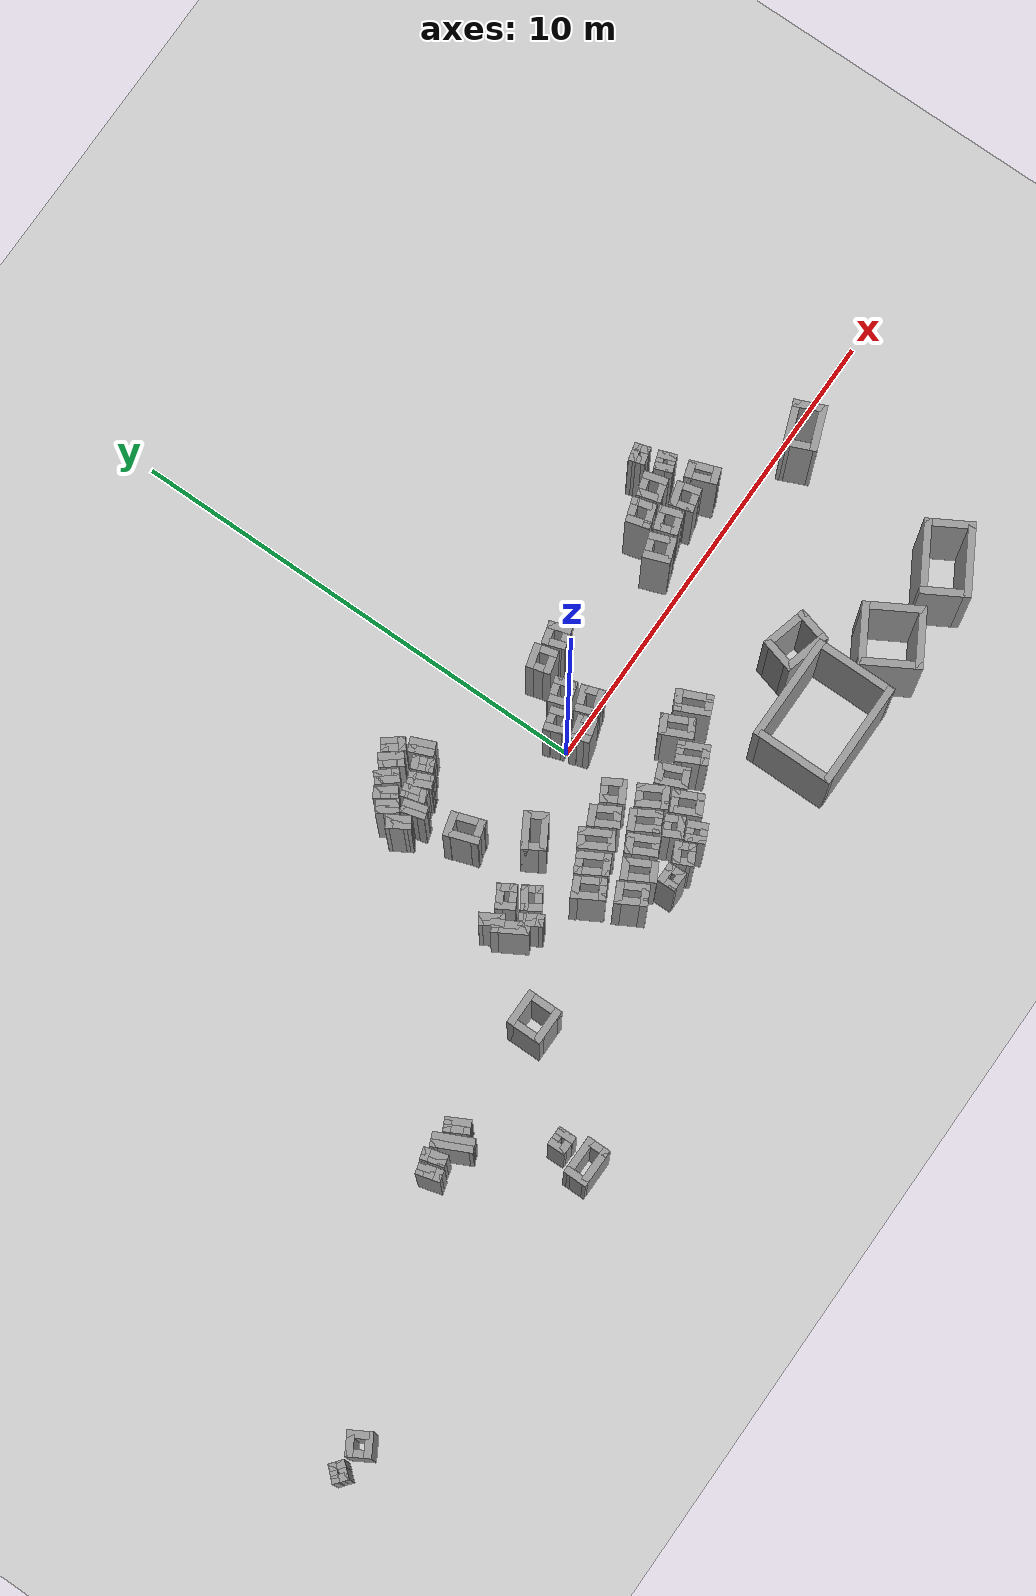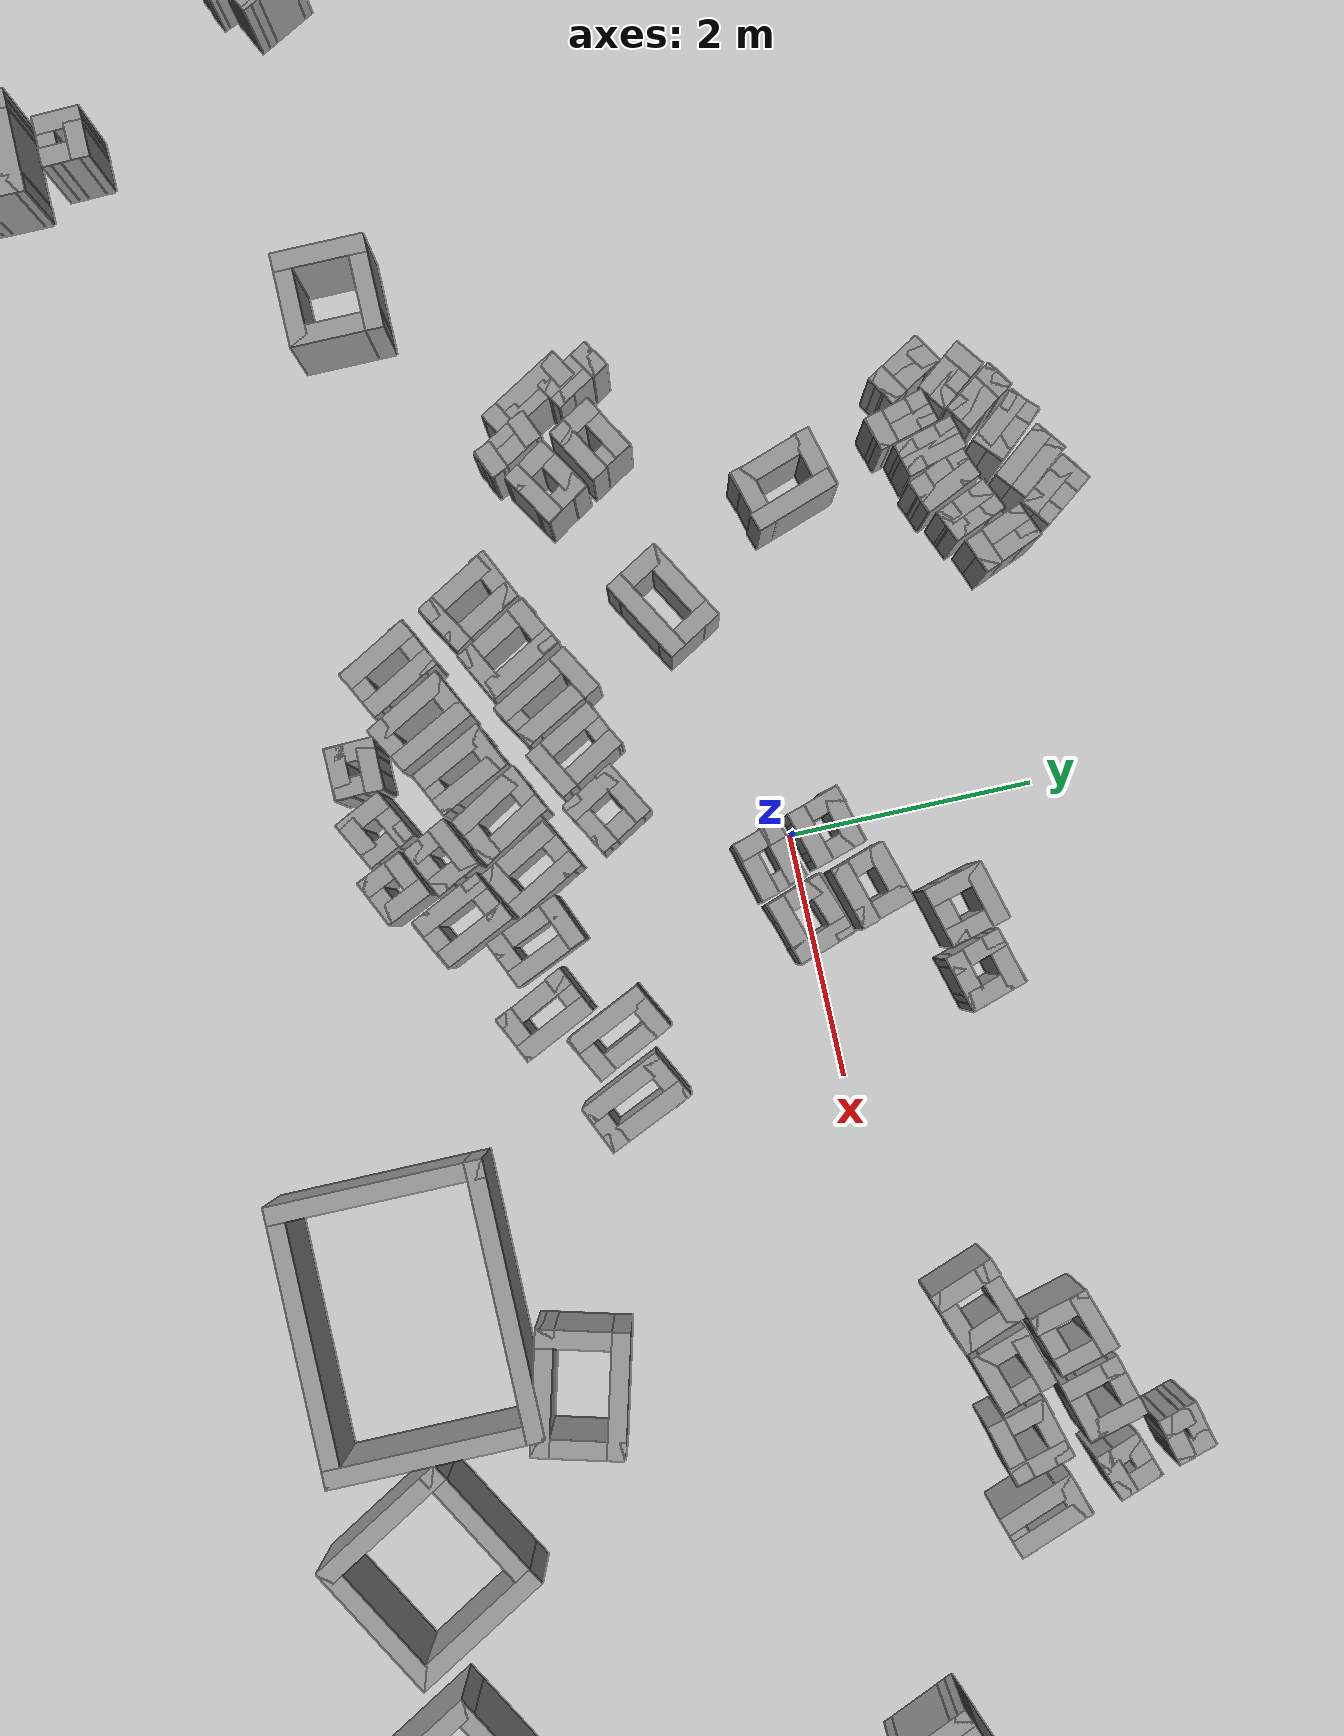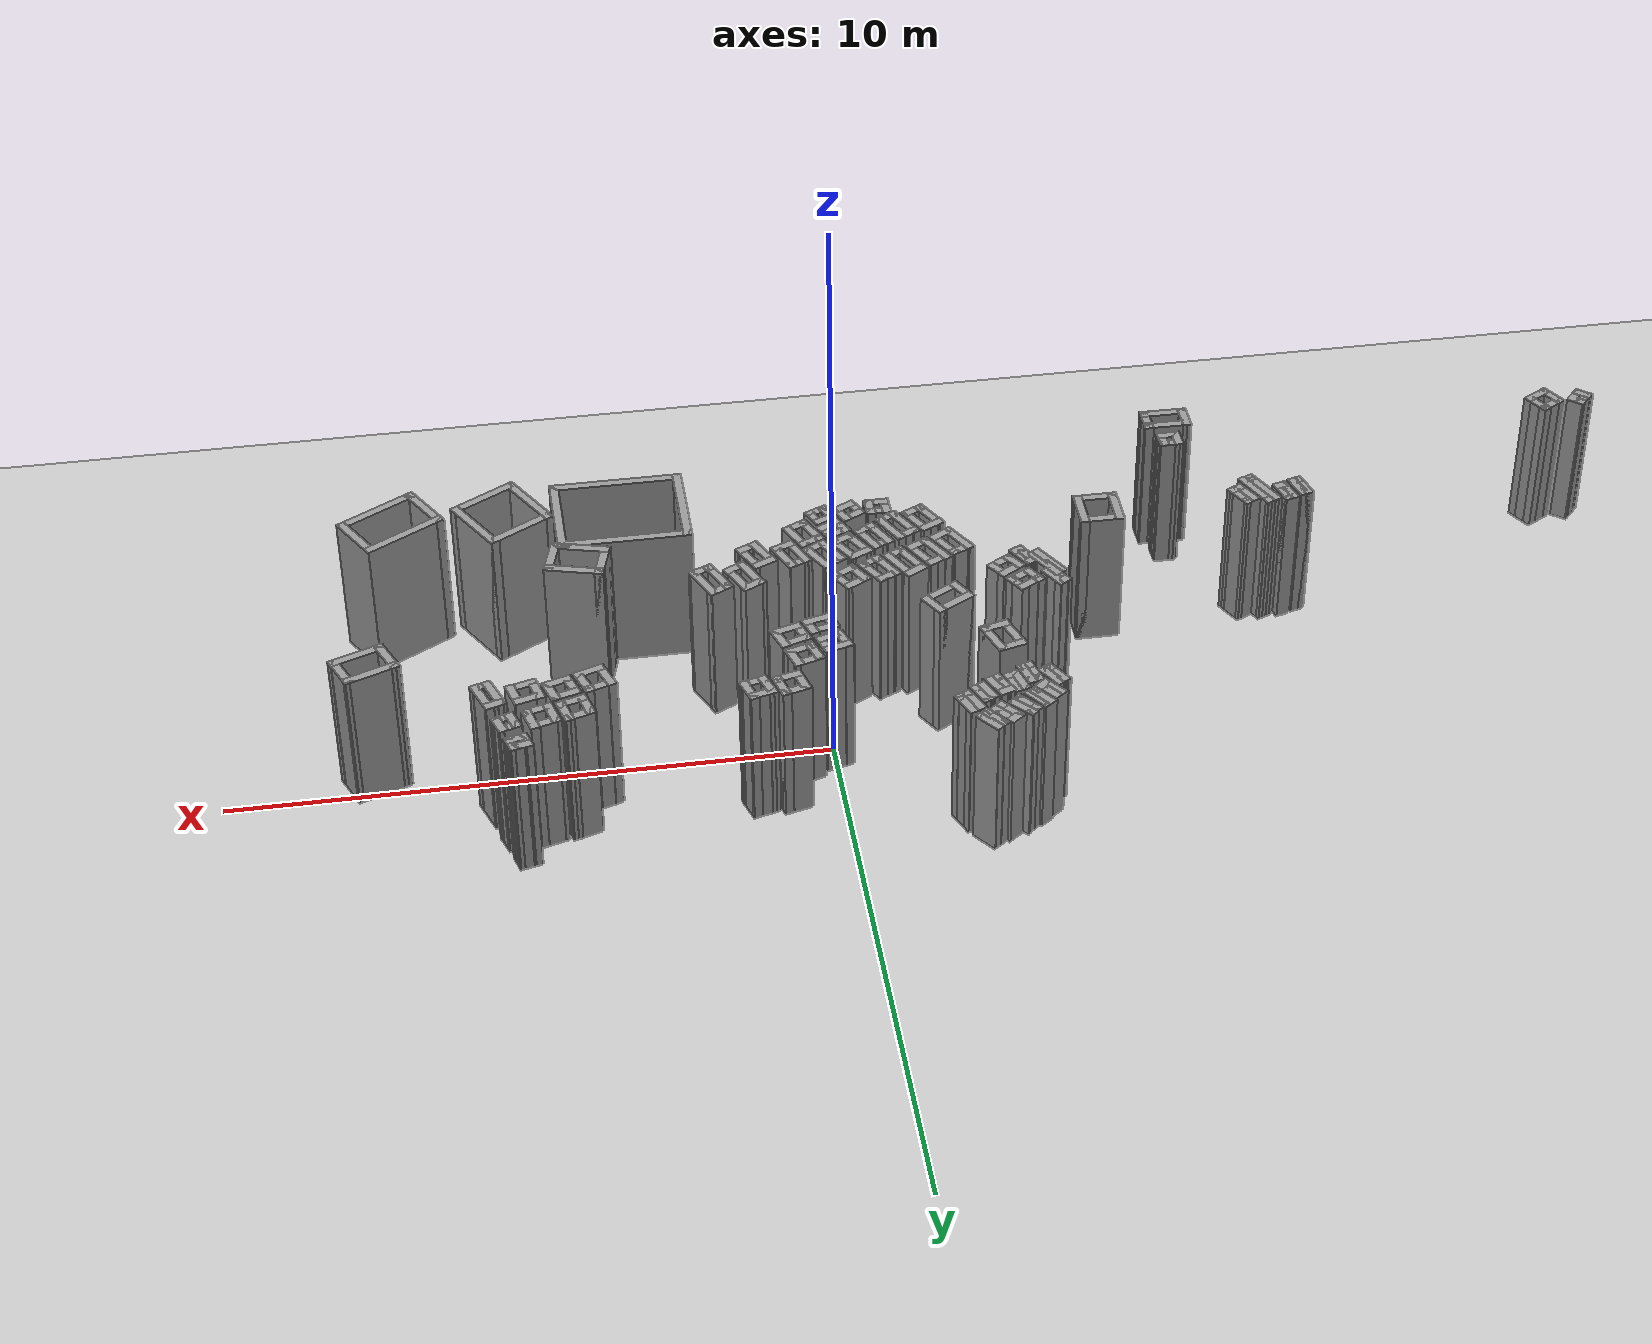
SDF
<sdf version='1.7'>
    <world name='default'>
    <include>
        <uri>model://sun</uri>
    </include>
    <include>
        <uri>model://ground_plane</uri>
    </include>
  <model name='iitj'>
    <pose>-3.03973 -1.21048 0 0 -0 0</pose>
    <link name='Wall_103'>
      <collision name='Wall_103_Collision'>
        <geometry>
          <box>
            <size>0.5 0.15 2.5</size>
          </box>
        </geometry>
        <pose>0 0 1.25 0 -0 0</pose>
      </collision>
      <visual name='Wall_103_Visual'>
        <pose>0 0 1.25 0 -0 0</pose>
        <geometry>
          <box>
            <size>0.5 0.15 2.5</size>
          </box>
        </geometry>
        <material>
          <script>
            <uri>file://media/materials/scripts/gazebo.material</uri>
            <name>Gazebo/Grey</name>
          </script>
          <ambient>1 1 1 1</ambient>
        </material>
        <meta>
          <layer>0</layer>
        </meta>
      </visual>
      <pose>-5.3281 -1.4758 0 0 -0 -1.309</pose>
    </link>
    <link name='Wall_105'>
      <collision name='Wall_105_Collision'>
        <geometry>
          <box>
            <size>0.25 0.15 2.5</size>
          </box>
        </geometry>
        <pose>0 0 1.25 0 -0 0</pose>
      </collision>
      <visual name='Wall_105_Visual'>
        <pose>0 0 1.25 0 -0 0</pose>
        <geometry>
          <box>
            <size>0.25 0.15 2.5</size>
          </box>
        </geometry>
        <material>
          <script>
            <uri>file://media/materials/scripts/gazebo.material</uri>
            <name>Gazebo/Grey</name>
          </script>
          <ambient>1 1 1 1</ambient>
        </material>
        <meta>
          <layer>0</layer>
        </meta>
      </visual>
      <pose>-5.33111 -1.65777 0 0 -0 -2.87979</pose>
    </link>
    <link name='Wall_107'>
      <collision name='Wall_107_Collision'>
        <geometry>
          <box>
            <size>0.25 0.15 2.5</size>
          </box>
        </geometry>
        <pose>0 0 1.25 0 -0 0</pose>
      </collision>
      <visual name='Wall_107_Visual'>
        <pose>0 0 1.25 0 -0 0</pose>
        <geometry>
          <box>
            <size>0.25 0.15 2.5</size>
          </box>
        </geometry>
        <material>
          <script>
            <uri>file://media/materials/scripts/gazebo.material</uri>
            <name>Gazebo/Grey</name>
          </script>
          <ambient>1 1 1 1</ambient>
        </material>
        <meta>
          <layer>0</layer>
        </meta>
      </visual>
      <pose>-5.42169 -1.3197 0 0 -0 -2.87979</pose>
    </link>
    <link name='Wall_112'>
      <collision name='Wall_112_Collision'>
        <geometry>
          <box>
            <size>0.5 0.15 2.5</size>
          </box>
        </geometry>
        <pose>0 0 1.25 0 -0 0</pose>
      </collision>
      <visual name='Wall_112_Visual'>
        <pose>0 0 1.25 0 -0 0</pose>
        <geometry>
          <box>
            <size>0.5 0.15 2.5</size>
          </box>
        </geometry>
        <material>
          <script>
            <uri>file://media/materials/scripts/gazebo.material</uri>
            <name>Gazebo/Grey</name>
          </script>
          <ambient>1 1 1 1</ambient>
        </material>
        <meta>
          <layer>0</layer>
        </meta>
      </visual>
      <pose>-5.4247 -1.50168 0 0 -0 -1.309</pose>
    </link>
    <link name='Wall_116'>
      <collision name='Wall_116_Collision'>
        <geometry>
          <box>
            <size>0.5 0.15 2.5</size>
          </box>
        </geometry>
        <pose>0 0 1.25 0 -0 0</pose>
      </collision>
      <visual name='Wall_116_Visual'>
        <pose>0 0 1.25 0 -0 0</pose>
        <geometry>
          <box>
            <size>0.5 0.15 2.5</size>
          </box>
        </geometry>
        <material>
          <script>
            <uri>file://media/materials/scripts/gazebo.material</uri>
            <name>Gazebo/Grey</name>
          </script>
          <ambient>1 1 1 1</ambient>
        </material>
        <meta>
          <layer>0</layer>
        </meta>
      </visual>
      <pose>-5.14754 -1.40825 0 0 -0 -1.309</pose>
    </link>
    <link name='Wall_119'>
      <collision name='Wall_119_Collision'>
        <geometry>
          <box>
            <size>0.25 0.15 2.5</size>
          </box>
        </geometry>
        <pose>0 0 1.25 0 -0 0</pose>
      </collision>
      <visual name='Wall_119_Visual'>
        <pose>0 0 1.25 0 -0 0</pose>
        <geometry>
          <box>
            <size>0.25 0.15 2.5</size>
          </box>
        </geometry>
        <material>
          <script>
            <uri>file://media/materials/scripts/gazebo.material</uri>
            <name>Gazebo/Grey</name>
          </script>
          <ambient>1 1 1 1</ambient>
        </material>
        <meta>
          <layer>0</layer>
        </meta>
      </visual>
      <pose>-5.05395 -1.56434 0 0 -0 0.261799</pose>
    </link>
    <link name='Wall_122'>
      <collision name='Wall_122_Collision'>
        <geometry>
          <box>
            <size>0.25 0.15 2.5</size>
          </box>
        </geometry>
        <pose>0 0 1.25 0 -0 0</pose>
      </collision>
      <visual name='Wall_122_Visual'>
        <pose>0 0 1.25 0 -0 0</pose>
        <geometry>
          <box>
            <size>0.25 0.15 2.5</size>
          </box>
        </geometry>
        <material>
          <script>
            <uri>file://media/materials/scripts/gazebo.material</uri>
            <name>Gazebo/Grey</name>
          </script>
          <ambient>1 1 1 1</ambient>
        </material>
        <meta>
          <layer>0</layer>
        </meta>
      </visual>
      <pose>-5.14454 -1.22627 0 0 -0 0.261799</pose>
    </link>
    <link name='Wall_125'>
      <collision name='Wall_125_Collision'>
        <geometry>
          <box>
            <size>0.5 0.15 2.5</size>
          </box>
        </geometry>
        <pose>0 0 1.25 0 -0 0</pose>
      </collision>
      <visual name='Wall_125_Visual'>
        <pose>0 0 1.25 0 -0 0</pose>
        <geometry>
          <box>
            <size>0.5 0.15 2.5</size>
          </box>
        </geometry>
        <material>
          <script>
            <uri>file://media/materials/scripts/gazebo.material</uri>
            <name>Gazebo/Grey</name>
          </script>
          <ambient>1 1 1 1</ambient>
        </material>
        <meta>
          <layer>0</layer>
        </meta>
      </visual>
      <pose>-5.05095 -1.38237 0 0 -0 -1.309</pose>
    </link>
    <link name='Wall_133'>
      <collision name='Wall_133_Collision'>
        <geometry>
          <box>
            <size>0.295025 0.15 2.5</size>
          </box>
        </geometry>
        <pose>0 0 1.25 0 -0 0</pose>
      </collision>
      <visual name='Wall_133_Visual'>
        <pose>0 0 1.25 0 -0 0</pose>
        <geometry>
          <box>
            <size>0.295025 0.15 2.5</size>
          </box>
        </geometry>
        <material>
          <script>
            <uri>file://media/materials/scripts/gazebo.material</uri>
            <name>Gazebo/Grey</name>
          </script>
          <ambient>1 1 1 1</ambient>
        </material>
        <meta>
          <layer>0</layer>
        </meta>
      </visual>
      <pose>-4.82254 -1.21507 0 0 -0 0.398916</pose>
    </link>
    <link name='Wall_134'>
      <collision name='Wall_134_Collision'>
        <geometry>
          <box>
            <size>0.830581 0.15 2.5</size>
          </box>
        </geometry>
        <pose>0 0 1.25 0 -0 0</pose>
      </collision>
      <visual name='Wall_134_Visual'>
        <pose>0 0 1.25 0 -0 0</pose>
        <geometry>
          <box>
            <size>0.830581 0.15 2.5</size>
          </box>
        </geometry>
        <material>
          <script>
            <uri>file://media/materials/scripts/gazebo.material</uri>
            <name>Gazebo/Grey</name>
          </script>
          <ambient>1 1 1 1</ambient>
        </material>
        <meta>
          <layer>0</layer>
        </meta>
      </visual>
      <pose>-4.61057 -1.49469 0 0 -0 -1.13012</pose>
    </link>
    <link name='Wall_136'>
      <collision name='Wall_136_Collision'>
        <geometry>
          <box>
            <size>0.290148 0.15 2.5</size>
          </box>
        </geometry>
        <pose>0 0 1.25 0 -0 0</pose>
      </collision>
      <visual name='Wall_136_Visual'>
        <pose>0 0 1.25 0 -0 0</pose>
        <geometry>
          <box>
            <size>0.290148 0.15 2.5</size>
          </box>
        </geometry>
        <material>
          <script>
            <uri>file://media/materials/scripts/gazebo.material</uri>
            <name>Gazebo/Grey</name>
          </script>
          <ambient>1 1 1 1</ambient>
        </material>
        <meta>
          <layer>0</layer>
        </meta>
      </visual>
      <pose>-4.53037 -1.82503 0 0 -0 -2.75688</pose>
    </link>
    <link name='Wall_143'>
      <collision name='Wall_143_Collision'>
        <geometry>
          <box>
            <size>0.825451 0.15 2.5</size>
          </box>
        </geometry>
        <pose>0 0 1.25 0 -0 0</pose>
      </collision>
      <visual name='Wall_143_Visual'>
        <pose>0 0 1.25 0 -0 0</pose>
        <geometry>
          <box>
            <size>0.825451 0.15 2.5</size>
          </box>
        </geometry>
        <material>
          <script>
            <uri>file://media/materials/scripts/gazebo.material</uri>
            <name>Gazebo/Grey</name>
          </script>
          <ambient>1 1 1 1</ambient>
        </material>
        <meta>
          <layer>0</layer>
        </meta>
      </visual>
      <pose>-4.74235 -1.54728 0 0 -0 2.02119</pose>
    </link>
    <link name='Wall_149'>
      <collision name='Wall_149_Collision'>
        <geometry>
          <box>
            <size>0.293388 0.15 2.5</size>
          </box>
        </geometry>
        <pose>0 0 1.25 0 -0 0</pose>
      </collision>
      <visual name='Wall_149_Visual'>
        <pose>0 0 1.25 0 -0 0</pose>
        <geometry>
          <box>
            <size>0.293388 0.15 2.5</size>
          </box>
        </geometry>
        <material>
          <script>
            <uri>file://media/materials/scripts/gazebo.material</uri>
            <name>Gazebo/Grey</name>
          </script>
          <ambient>1 1 1 1</ambient>
        </material>
        <meta>
          <layer>0</layer>
        </meta>
      </visual>
      <pose>-4.45634 -1.2476 0 0 -0 -2.68679</pose>
    </link>
    <link name='Wall_152'>
      <collision name='Wall_152_Collision'>
        <geometry>
          <box>
            <size>0.521208 0.15 2.5</size>
          </box>
        </geometry>
        <pose>0 0 1.25 0 -0 0</pose>
      </collision>
      <visual name='Wall_152_Visual'>
        <pose>0 0 1.25 0 -0 0</pose>
        <geometry>
          <box>
            <size>0.521208 0.15 2.5</size>
          </box>
        </geometry>
        <material>
          <script>
            <uri>file://media/materials/scripts/gazebo.material</uri>
            <name>Gazebo/Grey</name>
          </script>
          <ambient>1 1 1 1</ambient>
        </material>
        <meta>
          <layer>0</layer>
        </meta>
      </visual>
      <pose>-4.30606 -1.38065 0 0 -0 -1.08977</pose>
    </link>
    <link name='Wall_155'>
      <collision name='Wall_155_Collision'>
        <geometry>
          <box>
            <size>0.293388 0.15 2.5</size>
          </box>
        </geometry>
        <pose>0 0 1.25 0 -0 0</pose>
      </collision>
      <visual name='Wall_155_Visual'>
        <pose>0 0 1.25 0 -0 0</pose>
        <geometry>
          <box>
            <size>0.293388 0.15 2.5</size>
          </box>
        </geometry>
        <material>
          <script>
            <uri>file://media/materials/scripts/gazebo.material</uri>
            <name>Gazebo/Grey</name>
          </script>
          <ambient>1 1 1 1</ambient>
        </material>
        <meta>
          <layer>0</layer>
        </meta>
      </visual>
      <pose>-4.28459 -1.57668 0 0 -0 -2.68679</pose>
    </link>
    <link name='Wall_158'>
      <collision name='Wall_158_Collision'>
        <geometry>
          <box>
            <size>0.518333 0.15 2.5</size>
          </box>
        </geometry>
        <pose>0 0 1.25 0 -0 0</pose>
      </collision>
      <visual name='Wall_158_Visual'>
        <pose>0 0 1.25 0 -0 0</pose>
        <geometry>
          <box>
            <size>0.518333 0.15 2.5</size>
          </box>
        </geometry>
        <material>
          <script>
            <uri>file://media/materials/scripts/gazebo.material</uri>
            <name>Gazebo/Grey</name>
          </script>
          <ambient>1 1 1 1</ambient>
        </material>
        <meta>
          <layer>0</layer>
        </meta>
      </visual>
      <pose>-4.43487 -1.44526 0 0 -0 -1.08569</pose>
    </link>
    <link name='Wall_160'>
      <collision name='Wall_160_Collision'>
        <geometry>
          <box>
            <size>0.313829 0.15 2.5</size>
          </box>
        </geometry>
        <pose>0 0 1.25 0 -0 0</pose>
      </collision>
      <visual name='Wall_160_Visual'>
        <pose>0 0 1.25 0 -0 0</pose>
        <geometry>
          <box>
            <size>0.313829 0.15 2.5</size>
          </box>
        </geometry>
        <material>
          <script>
            <uri>file://media/materials/scripts/gazebo.material</uri>
            <name>Gazebo/Grey</name>
          </script>
          <ambient>1 1 1 1</ambient>
        </material>
        <meta>
          <layer>0</layer>
        </meta>
      </visual>
      <pose>-10.952 -3.37651 0 0 -0 -0.664496</pose>
    </link>
    <link name='Wall_161'>
      <collision name='Wall_161_Collision'>
        <geometry>
          <box>
            <size>0.385698 0.15 2.5</size>
          </box>
        </geometry>
        <pose>0 0 1.25 0 -0 0</pose>
      </collision>
      <visual name='Wall_161_Visual'>
        <pose>0 0 1.25 0 -0 0</pose>
        <geometry>
          <box>
            <size>0.385698 0.15 2.5</size>
          </box>
        </geometry>
        <material>
          <script>
            <uri>file://media/materials/scripts/gazebo.material</uri>
            <name>Gazebo/Grey</name>
          </script>
          <ambient>1 1 1 1</ambient>
        </material>
        <meta>
          <layer>0</layer>
        </meta>
      </visual>
      <pose>-10.8056 -3.34282 0 0 -0 0.869723</pose>
    </link>
    <link name='Wall_162'>
      <collision name='Wall_162_Collision'>
        <geometry>
          <box>
            <size>0.314597 0.15 2.5</size>
          </box>
        </geometry>
        <pose>0 0 1.25 0 -0 0</pose>
      </collision>
      <visual name='Wall_162_Visual'>
        <pose>0 0 1.25 0 -0 0</pose>
        <geometry>
          <box>
            <size>0.314597 0.15 2.5</size>
          </box>
        </geometry>
        <material>
          <script>
            <uri>file://media/materials/scripts/gazebo.material</uri>
            <name>Gazebo/Grey</name>
          </script>
          <ambient>1 1 1 1</ambient>
        </material>
        <meta>
          <layer>0</layer>
        </meta>
      </visual>
      <pose>-10.7888 -3.20202 0 0 -0 2.4771</pose>
    </link>
    <link name='Wall_163'>
      <collision name='Wall_163_Collision'>
        <geometry>
          <box>
            <size>0.381027 0.15 2.5</size>
          </box>
        </geometry>
        <pose>0 0 1.25 0 -0 0</pose>
      </collision>
      <visual name='Wall_163_Visual'>
        <pose>0 0 1.25 0 -0 0</pose>
        <geometry>
          <box>
            <size>0.381027 0.15 2.5</size>
          </box>
        </geometry>
        <material>
          <script>
            <uri>file://media/materials/scripts/gazebo.material</uri>
            <name>Gazebo/Grey</name>
          </script>
          <ambient>1 1 1 1</ambient>
        </material>
        <meta>
          <layer>0</layer>
        </meta>
      </visual>
      <pose>-10.938 -3.2357 0 0 -0 -2.32182</pose>
    </link>
    <link name='Wall_165'>
      <collision name='Wall_165_Collision'>
        <geometry>
          <box>
            <size>0.5 0.15 2.5</size>
          </box>
        </geometry>
        <pose>0 0 1.25 0 -0 0</pose>
      </collision>
      <visual name='Wall_165_Visual'>
        <pose>0 0 1.25 0 -0 0</pose>
        <geometry>
          <box>
            <size>0.5 0.15 2.5</size>
          </box>
        </geometry>
        <material>
          <script>
            <uri>file://media/materials/scripts/gazebo.material</uri>
            <name>Gazebo/Grey</name>
          </script>
          <ambient>1 1 1 1</ambient>
        </material>
        <meta>
          <layer>0</layer>
        </meta>
      </visual>
      <pose>-3.87395 -3.78493 0 0 -0 -1.5708</pose>
    </link>
    <link name='Wall_166'>
      <collision name='Wall_166_Collision'>
        <geometry>
          <box>
            <size>0.817402 0.15 2.5</size>
          </box>
        </geometry>
        <pose>0 0 1.25 0 -0 0</pose>
      </collision>
      <visual name='Wall_166_Visual'>
        <pose>0 0 1.25 0 -0 0</pose>
        <geometry>
          <box>
            <size>0.817402 0.15 2.5</size>
          </box>
        </geometry>
        <material>
          <script>
            <uri>file://media/materials/scripts/gazebo.material</uri>
            <name>Gazebo/Grey</name>
          </script>
          <ambient>1 1 1 1</ambient>
        </material>
        <meta>
          <layer>0</layer>
        </meta>
      </visual>
      <pose>-3.54026 -3.96274 0 0 -0 -0.008413</pose>
    </link>
    <link name='Wall_167'>
      <collision name='Wall_167_Collision'>
        <geometry>
          <box>
            <size>0.5 0.15 2.5</size>
          </box>
        </geometry>
        <pose>0 0 1.25 0 -0 0</pose>
      </collision>
      <visual name='Wall_167_Visual'>
        <pose>0 0 1.25 0 -0 0</pose>
        <geometry>
          <box>
            <size>0.5 0.15 2.5</size>
          </box>
        </geometry>
        <material>
          <script>
            <uri>file://media/materials/scripts/gazebo.material</uri>
            <name>Gazebo/Grey</name>
          </script>
          <ambient>1 1 1 1</ambient>
        </material>
        <meta>
          <layer>0</layer>
        </meta>
      </visual>
      <pose>-3.20657 -3.78493 0 0 -0 1.5708</pose>
    </link>
    <link name='Wall_168'>
      <collision name='Wall_168_Collision'>
        <geometry>
          <box>
            <size>0.817402 0.15 2.5</size>
          </box>
        </geometry>
        <pose>0 0 1.25 0 -0 0</pose>
      </collision>
      <visual name='Wall_168_Visual'>
        <pose>0 0 1.25 0 -0 0</pose>
        <geometry>
          <box>
            <size>0.817402 0.15 2.5</size>
          </box>
        </geometry>
        <material>
          <script>
            <uri>file://media/materials/scripts/gazebo.material</uri>
            <name>Gazebo/Grey</name>
          </script>
          <ambient>1 1 1 1</ambient>
        </material>
        <meta>
          <layer>0</layer>
        </meta>
      </visual>
      <pose>-3.54026 -3.61274 0 0 -0 3.13318</pose>
    </link>
    <link name='Wall_170'>
      <collision name='Wall_170_Collision'>
        <geometry>
          <box>
            <size>0.379211 0.15 2.5</size>
          </box>
        </geometry>
        <pose>0 0 1.25 0 -0 0</pose>
      </collision>
      <visual name='Wall_170_Visual'>
        <pose>0 0 1.25 0 -0 0</pose>
        <geometry>
          <box>
            <size>0.379211 0.15 2.5</size>
          </box>
        </geometry>
        <material>
          <script>
            <uri>file://media/materials/scripts/gazebo.material</uri>
            <name>Gazebo/Grey</name>
          </script>
          <ambient>1 1 1 1</ambient>
        </material>
        <meta>
          <layer>0</layer>
        </meta>
      </visual>
      <pose>-3.61336 -3.17986 0 0 -0 -1.5463</pose>
    </link>
    <link name='Wall_171'>
      <collision name='Wall_171_Collision'>
        <geometry>
          <box>
            <size>0.394326 0.15 2.5</size>
          </box>
        </geometry>
        <pose>0 0 1.25 0 -0 0</pose>
      </collision>
      <visual name='Wall_171_Visual'>
        <pose>0 0 1.25 0 -0 0</pose>
        <geometry>
          <box>
            <size>0.394326 0.15 2.5</size>
          </box>
        </geometry>
        <material>
          <script>
            <uri>file://media/materials/scripts/gazebo.material</uri>
            <name>Gazebo/Grey</name>
          </script>
          <ambient>1 1 1 1</ambient>
        </material>
        <meta>
          <layer>0</layer>
        </meta>
      </visual>
      <pose>-3.47766 -3.29443 0 0 -0 0</pose>
    </link>
    <link name='Wall_172'>
      <collision name='Wall_172_Collision'>
        <geometry>
          <box>
            <size>0.379211 0.15 2.5</size>
          </box>
        </geometry>
        <pose>0 0 1.25 0 -0 0</pose>
      </collision>
      <visual name='Wall_172_Visual'>
        <pose>0 0 1.25 0 -0 0</pose>
        <geometry>
          <box>
            <size>0.379211 0.15 2.5</size>
          </box>
        </geometry>
        <material>
          <script>
            <uri>file://media/materials/scripts/gazebo.material</uri>
            <name>Gazebo/Grey</name>
          </script>
          <ambient>1 1 1 1</ambient>
        </material>
        <meta>
          <layer>0</layer>
        </meta>
      </visual>
      <pose>-3.35831 -3.18548 0 0 -0 1.59529</pose>
    </link>
    <link name='Wall_173'>
      <collision name='Wall_173_Collision'>
        <geometry>
          <box>
            <size>0.394326 0.15 2.5</size>
          </box>
        </geometry>
        <pose>0 0 1.25 0 -0 0</pose>
      </collision>
      <visual name='Wall_173_Visual'>
        <pose>0 0 1.25 0 -0 0</pose>
        <geometry>
          <box>
            <size>0.394326 0.15 2.5</size>
          </box>
        </geometry>
        <material>
          <script>
            <uri>file://media/materials/scripts/gazebo.material</uri>
            <name>Gazebo/Grey</name>
          </script>
          <ambient>1 1 1 1</ambient>
        </material>
        <meta>
          <layer>0</layer>
        </meta>
      </visual>
      <pose>-3.48328 -3.06529 0 0 -0 3.14159</pose>
    </link>
    <link name='Wall_175'>
      <collision name='Wall_175_Collision'>
        <geometry>
          <box>
            <size>0.75 0.15 2.5</size>
          </box>
        </geometry>
        <pose>0 0 1.25 0 -0 0</pose>
      </collision>
      <visual name='Wall_175_Visual'>
        <pose>0 0 1.25 0 -0 0</pose>
        <geometry>
          <box>
            <size>0.75 0.15 2.5</size>
          </box>
        </geometry>
        <material>
          <script>
            <uri>file://media/materials/scripts/gazebo.material</uri>
            <name>Gazebo/Grey</name>
          </script>
          <ambient>1 1 1 1</ambient>
        </material>
        <meta>
          <layer>0</layer>
        </meta>
      </visual>
      <pose>-2.16502 -1.42542 0 0 -0 -1.5708</pose>
    </link>
    <link name='Wall_176'>
      <collision name='Wall_176_Collision'>
        <geometry>
          <box>
            <size>0.75 0.15 2.5</size>
          </box>
        </geometry>
        <pose>0 0 1.25 0 -0 0</pose>
      </collision>
      <visual name='Wall_176_Visual'>
        <pose>0 0 1.25 0 -0 0</pose>
        <geometry>
          <box>
            <size>0.75 0.15 2.5</size>
          </box>
        </geometry>
        <material>
          <script>
            <uri>file://media/materials/scripts/gazebo.material</uri>
            <name>Gazebo/Grey</name>
          </script>
          <ambient>1 1 1 1</ambient>
        </material>
        <meta>
          <layer>0</layer>
        </meta>
      </visual>
      <pose>-1.86502 -1.72542 0 0 -0 0</pose>
    </link>
    <link name='Wall_177'>
      <collision name='Wall_177_Collision'>
        <geometry>
          <box>
            <size>0.75 0.15 2.5</size>
          </box>
        </geometry>
        <pose>0 0 1.25 0 -0 0</pose>
      </collision>
      <visual name='Wall_177_Visual'>
        <pose>0 0 1.25 0 -0 0</pose>
        <geometry>
          <box>
            <size>0.75 0.15 2.5</size>
          </box>
        </geometry>
        <material>
          <script>
            <uri>file://media/materials/scripts/gazebo.material</uri>
            <name>Gazebo/Grey</name>
          </script>
          <ambient>1 1 1 1</ambient>
        </material>
        <meta>
          <layer>0</layer>
        </meta>
      </visual>
      <pose>-1.56502 -1.42542 0 0 -0 1.5708</pose>
    </link>
    <link name='Wall_178'>
      <collision name='Wall_178_Collision'>
        <geometry>
          <box>
            <size>0.75 0.15 2.5</size>
          </box>
        </geometry>
        <pose>0 0 1.25 0 -0 0</pose>
      </collision>
      <visual name='Wall_178_Visual'>
        <pose>0 0 1.25 0 -0 0</pose>
        <geometry>
          <box>
            <size>0.75 0.15 2.5</size>
          </box>
        </geometry>
        <material>
          <script>
            <uri>file://media/materials/scripts/gazebo.material</uri>
            <name>Gazebo/Grey</name>
          </script>
          <ambient>1 1 1 1</ambient>
        </material>
        <meta>
          <layer>0</layer>
        </meta>
      </visual>
      <pose>-1.86502 -1.12542 0 0 -0 3.14159</pose>
    </link>
    <link name='Wall_186'>
      <collision name='Wall_186_Collision'>
        <geometry>
          <box>
            <size>0.64769 0.15 2.5</size>
          </box>
        </geometry>
        <pose>0 0 1.25 0 -0 0</pose>
      </collision>
      <visual name='Wall_186_Visual'>
        <pose>0 0 1.25 0 -0 0</pose>
        <geometry>
          <box>
            <size>0.64769 0.15 2.5</size>
          </box>
        </geometry>
        <material>
          <script>
            <uri>file://media/materials/scripts/gazebo.material</uri>
            <name>Gazebo/Grey</name>
          </script>
          <ambient>1 1 1 1</ambient>
        </material>
        <meta>
          <layer>0</layer>
        </meta>
      </visual>
      <pose>0.987547 -1.66589 0 0 -0 -1.06824</pose>
    </link>
    <link name='Wall_187'>
      <collision name='Wall_187_Collision'>
        <geometry>
          <box>
            <size>0.437529 0.15 2.5</size>
          </box>
        </geometry>
        <pose>0 0 1.25 0 -0 0</pose>
      </collision>
      <visual name='Wall_187_Visual'>
        <pose>0 0 1.25 0 -0 0</pose>
        <geometry>
          <box>
            <size>0.437529 0.15 2.5</size>
          </box>
        </geometry>
        <material>
          <script>
            <uri>file://media/materials/scripts/gazebo.material</uri>
            <name>Gazebo/Grey</name>
          </script>
          <ambient>1 1 1 1</ambient>
        </material>
        <meta>
          <layer>0</layer>
        </meta>
      </visual>
      <pose>1.23128 -1.81951 0 0 -0 0.464887</pose>
    </link>
    <link name='Wall_188'>
      <collision name='Wall_188_Collision'>
        <geometry>
          <box>
            <size>0.64769 0.15 2.5</size>
          </box>
        </geometry>
        <pose>0 0 1.25 0 -0 0</pose>
      </collision>
      <visual name='Wall_188_Visual'>
        <pose>0 0 1.25 0 -0 0</pose>
        <geometry>
          <box>
            <size>0.64769 0.15 2.5</size>
          </box>
        </geometry>
        <material>
          <script>
            <uri>file://media/materials/scripts/gazebo.material</uri>
            <name>Gazebo/Grey</name>
          </script>
          <ambient>1 1 1 1</ambient>
        </material>
        <meta>
          <layer>0</layer>
        </meta>
      </visual>
      <pose>1.23992 -1.53698 0 0 -0 2.07335</pose>
    </link>
    <link name='Wall_189'>
      <collision name='Wall_189_Collision'>
        <geometry>
          <box>
            <size>0.439662 0.15 2.5</size>
          </box>
        </geometry>
        <pose>0 0 1.25 0 -0 0</pose>
      </collision>
      <visual name='Wall_189_Visual'>
        <pose>0 0 1.25 0 -0 0</pose>
        <geometry>
          <box>
            <size>0.439662 0.15 2.5</size>
          </box>
        </geometry>
        <material>
          <script>
            <uri>file://media/materials/scripts/gazebo.material</uri>
            <name>Gazebo/Grey</name>
          </script>
          <ambient>1 1 1 1</ambient>
        </material>
        <meta>
          <layer>0</layer>
        </meta>
      </visual>
      <pose>0.993875 -1.38568 0 0 -0 -2.69819</pose>
    </link>
    <link name='Wall_193'>
      <collision name='Wall_193_Collision'>
        <geometry>
          <box>
            <size>0.442594 0.15 2.5</size>
          </box>
        </geometry>
        <pose>0 0 1.25 0 -0 0</pose>
      </collision>
      <visual name='Wall_193_Visual'>
        <pose>0 0 1.25 0 -0 0</pose>
        <geometry>
          <box>
            <size>0.442594 0.15 2.5</size>
          </box>
        </geometry>
        <material>
          <script>
            <uri>file://media/materials/scripts/gazebo.material</uri>
            <name>Gazebo/Grey</name>
          </script>
          <ambient>1 1 1 1</ambient>
        </material>
        <meta>
          <layer>0</layer>
        </meta>
      </visual>
      <pose>0.874775 -1.09728 0 0 -0 0.537733</pose>
    </link>
    <link name='Wall_195'>
      <collision name='Wall_195_Collision'>
        <geometry>
          <box>
            <size>0.644327 0.15 2.5</size>
          </box>
        </geometry>
        <pose>0 0 1.25 0 -0 0</pose>
      </collision>
      <visual name='Wall_195_Visual'>
        <pose>0 0 1.25 0 -0 0</pose>
        <geometry>
          <box>
            <size>0.644327 0.15 2.5</size>
          </box>
        </geometry>
        <material>
          <script>
            <uri>file://media/materials/scripts/gazebo.material</uri>
            <name>Gazebo/Grey</name>
          </script>
          <ambient>1 1 1 1</ambient>
        </material>
        <meta>
          <layer>0</layer>
        </meta>
      </visual>
      <pose>0.871209 -0.806616 0 0 -0 -1.06094</pose>
    </link>
    <link name='Wall_197'>
      <collision name='Wall_197_Collision'>
        <geometry>
          <box>
            <size>0.673902 0.15 2.5</size>
          </box>
        </geometry>
        <pose>0 0 1.25 0 -0 0</pose>
      </collision>
      <visual name='Wall_197_Visual'>
        <pose>0 0 1.25 0 -0 0</pose>
        <geometry>
          <box>
            <size>0.673902 0.15 2.5</size>
          </box>
        </geometry>
        <material>
          <script>
            <uri>file://media/materials/scripts/gazebo.material</uri>
            <name>Gazebo/Grey</name>
          </script>
          <ambient>1 1 1 1</ambient>
        </material>
        <meta>
          <layer>0</layer>
        </meta>
      </visual>
      <pose>0.613228 -0.944134 0 0 -0 2.08502</pose>
    </link>
    <link name='Wall_199'>
      <collision name='Wall_199_Collision'>
        <geometry>
          <box>
            <size>0.444158 0.15 2.5</size>
          </box>
        </geometry>
        <pose>0 0 1.25 0 -0 0</pose>
      </collision>
      <visual name='Wall_199_Visual'>
        <pose>0 0 1.25 0 -0 0</pose>
        <geometry>
          <box>
            <size>0.444158 0.15 2.5</size>
          </box>
        </geometry>
        <material>
          <script>
            <uri>file://media/materials/scripts/gazebo.material</uri>
            <name>Gazebo/Grey</name>
          </script>
          <ambient>1 1 1 1</ambient>
        </material>
        <meta>
          <layer>0</layer>
        </meta>
      </visual>
      <pose>0.61043 -0.653474 0 0 -0 0.439548</pose>
    </link>
    <link name='Wall_202'>
      <collision name='Wall_202_Collision'>
        <geometry>
          <box>
            <size>0.698683 0.15 2.5</size>
          </box>
        </geometry>
        <pose>0 0 1.25 0 -0 0</pose>
      </collision>
      <visual name='Wall_202_Visual'>
        <pose>0 0 1.25 0 -0 0</pose>
        <geometry>
          <box>
            <size>0.698683 0.15 2.5</size>
          </box>
        </geometry>
        <material>
          <script>
            <uri>file://media/materials/scripts/gazebo.material</uri>
            <name>Gazebo/Grey</name>
          </script>
          <ambient>1 1 1 1</ambient>
        </material>
        <meta>
          <layer>0</layer>
        </meta>
      </visual>
      <pose>1.44228 -1.52213 0 0 -0 -1.07463</pose>
    </link>
    <link name='Wall_203'>
      <collision name='Wall_203_Collision'>
        <geometry>
          <box>
            <size>0.419364 0.15 2.5</size>
          </box>
        </geometry>
        <pose>0 0 1.25 0 -0 0</pose>
      </collision>
      <visual name='Wall_203_Visual'>
        <pose>0 0 1.25 0 -0 0</pose>
        <geometry>
          <box>
            <size>0.419364 0.15 2.5</size>
          </box>
        </geometry>
        <material>
          <script>
            <uri>file://media/materials/scripts/gazebo.material</uri>
            <name>Gazebo/Grey</name>
          </script>
          <ambient>1 1 1 1</ambient>
        </material>
        <meta>
          <layer>0</layer>
        </meta>
      </visual>
      <pose>1.69514 -1.70243 0 0 -0 0.508676</pose>
    </link>
    <link name='Wall_204'>
      <collision name='Wall_204_Collision'>
        <geometry>
          <box>
            <size>0.692978 0.15 2.5</size>
          </box>
        </geometry>
        <pose>0 0 1.25 0 -0 0</pose>
      </collision>
      <visual name='Wall_204_Visual'>
        <pose>0 0 1.25 0 -0 0</pose>
        <geometry>
          <box>
            <size>0.692978 0.15 2.5</size>
          </box>
        </geometry>
        <material>
          <script>
            <uri>file://media/materials/scripts/gazebo.material</uri>
            <name>Gazebo/Grey</name>
          </script>
          <ambient>1 1 1 1</ambient>
        </material>
        <meta>
          <layer>0</layer>
        </meta>
      </visual>
      <pose>1.69291 -1.39094 0 0 -0 2.04719</pose>
    </link>
    <link name='Wall_205'>
      <collision name='Wall_205_Collision'>
        <geometry>
          <box>
            <size>0.436235 0.15 2.5</size>
          </box>
        </geometry>
        <pose>0 0 1.25 0 -0 0</pose>
      </collision>
      <visual name='Wall_205_Visual'>
        <pose>0 0 1.25 0 -0 0</pose>
        <geometry>
          <box>
            <size>0.436235 0.15 2.5</size>
          </box>
        </geometry>
        <material>
          <script>
            <uri>file://media/materials/scripts/gazebo.material</uri>
            <name>Gazebo/Grey</name>
          </script>
          <ambient>1 1 1 1</ambient>
        </material>
        <meta>
          <layer>0</layer>
        </meta>
      </visual>
      <pose>1.43541 -1.21759 0 0 -0 -2.68364</pose>
    </link>
    <link name='Wall_207'>
      <collision name='Wall_207_Collision'>
        <geometry>
          <box>
            <size>0.680486 0.15 2.5</size>
          </box>
        </geometry>
        <pose>0 0 1.25 0 -0 0</pose>
      </collision>
      <visual name='Wall_207_Visual'>
        <pose>0 0 1.25 0 -0 0</pose>
        <geometry>
          <box>
            <size>0.680486 0.15 2.5</size>
          </box>
        </geometry>
        <material>
          <script>
            <uri>file://media/materials/scripts/gazebo.material</uri>
            <name>Gazebo/Grey</name>
          </script>
          <ambient>1 1 1 1</ambient>
        </material>
        <meta>
          <layer>0</layer>
        </meta>
      </visual>
      <pose>1.03344 -0.723588 0 0 -0 -1.05162</pose>
    </link>
    <link name='Wall_208'>
      <collision name='Wall_208_Collision'>
        <geometry>
          <box>
            <size>0.44288 0.15 2.5</size>
          </box>
        </geometry>
        <pose>0 0 1.25 0 -0 0</pose>
      </collision>
      <visual name='Wall_208_Visual'>
        <pose>0 0 1.25 0 -0 0</pose>
        <geometry>
          <box>
            <size>0.44288 0.15 2.5</size>
          </box>
        </geometry>
        <material>
          <script>
            <uri>file://media/materials/scripts/gazebo.material</uri>
            <name>Gazebo/Grey</name>
          </script>
          <ambient>1 1 1 1</ambient>
        </material>
        <meta>
          <layer>0</layer>
        </meta>
      </visual>
      <pose>1.29554 -0.893568 0 0 -0 0.470946</pose>
    </link>
    <link name='Wall_209'>
      <collision name='Wall_209_Collision'>
        <geometry>
          <box>
            <size>0.676358 0.15 2.5</size>
          </box>
        </geometry>
        <pose>0 0 1.25 0 -0 0</pose>
      </collision>
      <visual name='Wall_209_Visual'>
        <pose>0 0 1.25 0 -0 0</pose>
        <geometry>
          <box>
            <size>0.676358 0.15 2.5</size>
          </box>
        </geometry>
        <material>
          <script>
            <uri>file://media/materials/scripts/gazebo.material</uri>
            <name>Gazebo/Grey</name>
          </script>
          <ambient>1 1 1 1</ambient>
        </material>
        <meta>
          <layer>0</layer>
        </meta>
      </visual>
      <pose>1.29865 -0.590699 0 0 -0 2.07608</pose>
    </link>
    <link name='Wall_210'>
      <collision name='Wall_210_Collision'>
        <geometry>
          <box>
            <size>0.44288 0.15 2.5</size>
          </box>
        </geometry>
        <pose>0 0 1.25 0 -0 0</pose>
      </collision>
      <visual name='Wall_210_Visual'>
        <pose>0 0 1.25 0 -0 0</pose>
        <geometry>
          <box>
            <size>0.44288 0.15 2.5</size>
          </box>
        </geometry>
        <material>
          <script>
            <uri>file://media/materials/scripts/gazebo.material</uri>
            <name>Gazebo/Grey</name>
          </script>
          <ambient>1 1 1 1</ambient>
        </material>
        <meta>
          <layer>0</layer>
        </meta>
      </visual>
      <pose>1.03234 -0.435274 0 0 -0 -2.67065</pose>
    </link>
    <link name='Wall_212'>
      <collision name='Wall_212_Collision'>
        <geometry>
          <box>
            <size>0.648903 0.15 2.5</size>
          </box>
        </geometry>
        <pose>0 0 1.25 0 -0 0</pose>
      </collision>
      <visual name='Wall_212_Visual'>
        <pose>0 0 1.25 0 -0 0</pose>
        <geometry>
          <box>
            <size>0.648903 0.15 2.5</size>
          </box>
        </geometry>
        <material>
          <script>
            <uri>file://media/materials/scripts/gazebo.material</uri>
            <name>Gazebo/Grey</name>
          </script>
          <ambient>1 1 1 1</ambient>
        </material>
        <meta>
          <layer>0</layer>
        </meta>
      </visual>
      <pose>1.88601 -1.28038 0 0 -0 -1.10363</pose>
    </link>
    <link name='Wall_213'>
      <collision name='Wall_213_Collision'>
        <geometry>
          <box>
            <size>0.402633 0.15 2.5</size>
          </box>
        </geometry>
        <pose>0 0 1.25 0 -0 0</pose>
      </collision>
      <visual name='Wall_213_Visual'>
        <pose>0 0 1.25 0 -0 0</pose>
        <geometry>
          <box>
            <size>0.402633 0.15 2.5</size>
          </box>
        </geometry>
        <material>
          <script>
            <uri>file://media/materials/scripts/gazebo.material</uri>
            <name>Gazebo/Grey</name>
          </script>
          <ambient>1 1 1 1</ambient>
        </material>
        <meta>
          <layer>0</layer>
        </meta>
      </visual>
      <pose>2.10732 -1.45252 0 0 -0 0.452359</pose>
    </link>
    <link name='Wall_214'>
      <collision name='Wall_214_Collision'>
        <geometry>
          <box>
            <size>0.644621 0.15 2.5</size>
          </box>
        </geometry>
        <pose>0 0 1.25 0 -0 0</pose>
      </collision>
      <visual name='Wall_214_Visual'>
        <pose>0 0 1.25 0 -0 0</pose>
        <geometry>
          <box>
            <size>0.644621 0.15 2.5</size>
          </box>
        </geometry>
        <material>
          <script>
            <uri>file://media/materials/scripts/gazebo.material</uri>
            <name>Gazebo/Grey</name>
          </script>
          <ambient>1 1 1 1</ambient>
        </material>
        <meta>
          <layer>0</layer>
        </meta>
      </visual>
      <pose>2.11182 -1.17538 0 0 -0 2.02774</pose>
    </link>
    <link name='Wall_215'>
      <collision name='Wall_215_Collision'>
        <geometry>
          <box>
            <size>0.401634 0.15 2.5</size>
          </box>
        </geometry>
        <pose>0 0 1.25 0 -0 0</pose>
      </collision>
      <visual name='Wall_215_Visual'>
        <pose>0 0 1.25 0 -0 0</pose>
        <geometry>
          <box>
            <size>0.401634 0.15 2.5</size>
          </box>
        </geometry>
        <material>
          <script>
            <uri>file://media/materials/scripts/gazebo.material</uri>
            <name>Gazebo/Grey</name>
          </script>
          <ambient>1 1 1 1</ambient>
        </material>
        <meta>
          <layer>0</layer>
        </meta>
      </visual>
      <pose>1.88819 -1.01365 0 0 -0 -2.71458</pose>
    </link>
    <link name='Wall_217'>
      <collision name='Wall_217_Collision'>
        <geometry>
          <box>
            <size>0.648669 0.15 2.5</size>
          </box>
        </geometry>
        <pose>0 0 1.25 0 -0 0</pose>
      </collision>
      <visual name='Wall_217_Visual'>
        <pose>0 0 1.25 0 -0 0</pose>
        <geometry>
          <box>
            <size>0.648669 0.15 2.5</size>
          </box>
        </geometry>
        <material>
          <script>
            <uri>file://media/materials/scripts/gazebo.material</uri>
            <name>Gazebo/Grey</name>
          </script>
          <ambient>1 1 1 1</ambient>
        </material>
        <meta>
          <layer>0</layer>
        </meta>
      </visual>
      <pose>2.28325 -1.06908 0 0 -0 -1.035</pose>
    </link>
    <link name='Wall_218'>
      <collision name='Wall_218_Collision'>
        <geometry>
          <box>
            <size>0.43838 0.15 2.5</size>
          </box>
        </geometry>
        <pose>0 0 1.25 0 -0 0</pose>
      </collision>
      <visual name='Wall_218_Visual'>
        <pose>0 0 1.25 0 -0 0</pose>
        <geometry>
          <box>
            <size>0.43838 0.15 2.5</size>
          </box>
        </geometry>
        <material>
          <script>
            <uri>file://media/materials/scripts/gazebo.material</uri>
            <name>Gazebo/Grey</name>
          </script>
          <ambient>1 1 1 1</ambient>
        </material>
        <meta>
          <layer>0</layer>
        </meta>
      </visual>
      <pose>2.53122 -1.22111 0 0 -0 0.447258</pose>
    </link>
    <link name='Wall_219'>
      <collision name='Wall_219_Collision'>
        <geometry>
          <box>
            <size>0.648669 0.15 2.5</size>
          </box>
        </geometry>
        <pose>0 0 1.25 0 -0 0</pose>
      </collision>
      <visual name='Wall_219_Visual'>
        <pose>0 0 1.25 0 -0 0</pose>
        <geometry>
          <box>
            <size>0.648669 0.15 2.5</size>
          </box>
        </geometry>
        <material>
          <script>
            <uri>file://media/materials/scripts/gazebo.material</uri>
            <name>Gazebo/Grey</name>
          </script>
          <ambient>1 1 1 1</ambient>
        </material>
        <meta>
          <layer>0</layer>
        </meta>
      </visual>
      <pose>2.54326 -0.94436 0 0 -0 2.1066</pose>
    </link>
    <link name='Wall_220'>
      <collision name='Wall_220_Collision'>
        <geometry>
          <box>
            <size>0.43838 0.15 2.5</size>
          </box>
        </geometry>
        <pose>0 0 1.25 0 -0 0</pose>
      </collision>
      <visual name='Wall_220_Visual'>
        <pose>0 0 1.25 0 -0 0</pose>
        <geometry>
          <box>
            <size>0.43838 0.15 2.5</size>
          </box>
        </geometry>
        <material>
          <script>
            <uri>file://media/materials/scripts/gazebo.material</uri>
            <name>Gazebo/Grey</name>
          </script>
          <ambient>1 1 1 1</ambient>
        </material>
        <meta>
          <layer>0</layer>
        </meta>
      </visual>
      <pose>2.28596 -0.792329 0 0 -0 -2.69434</pose>
    </link>
    <link name='Wall_222'>
      <collision name='Wall_222_Collision'>
        <geometry>
          <box>
            <size>0.640461 0.15 2.5</size>
          </box>
        </geometry>
        <pose>0 0 1.25 0 -0 0</pose>
      </collision>
      <visual name='Wall_222_Visual'>
        <pose>0 0 1.25 0 -0 0</pose>
        <geometry>
          <box>
            <size>0.640461 0.15 2.5</size>
          </box>
        </geometry>
        <material>
          <script>
            <uri>file://media/materials/scripts/gazebo.material</uri>
            <name>Gazebo/Grey</name>
          </script>
          <ambient>1 1 1 1</ambient>
        </material>
        <meta>
          <layer>0</layer>
        </meta>
      </visual>
      <pose>2.74712 -0.931314 0 0 -0 -1.06854</pose>
    </link>
    <link name='Wall_223'>
      <collision name='Wall_223_Collision'>
        <geometry>
          <box>
            <size>0.456014 0.15 2.5</size>
          </box>
        </geometry>
        <pose>0 0 1.25 0 -0 0</pose>
      </collision>
      <visual name='Wall_223_Visual'>
        <pose>0 0 1.25 0 -0 0</pose>
        <geometry>
          <box>
            <size>0.456014 0.15 2.5</size>
          </box>
        </geometry>
        <material>
          <script>
            <uri>file://media/materials/scripts/gazebo.material</uri>
            <name>Gazebo/Grey</name>
          </script>
          <ambient>1 1 1 1</ambient>
        </material>
        <meta>
          <layer>0</layer>
        </meta>
      </visual>
      <pose>2.99878 -1.07168 0 0 -0 0.509162</pose>
    </link>
    <link name='Wall_224'>
      <collision name='Wall_224_Collision'>
        <geometry>
          <box>
            <size>0.640461 0.15 2.5</size>
          </box>
        </geometry>
        <pose>0 0 1.25 0 -0 0</pose>
      </collision>
      <visual name='Wall_224_Visual'>
        <pose>0 0 1.25 0 -0 0</pose>
        <geometry>
          <box>
            <size>0.640461 0.15 2.5</size>
          </box>
        </geometry>
        <material>
          <script>
            <uri>file://media/materials/scripts/gazebo.material</uri>
            <name>Gazebo/Grey</name>
          </script>
          <ambient>1 1 1 1</ambient>
        </material>
        <meta>
          <layer>0</layer>
        </meta>
      </visual>
      <pose>3.01432 -0.782149 0 0 -0 2.07305</pose>
    </link>
    <link name='Wall_225'>
      <collision name='Wall_225_Collision'>
        <geometry>
          <box>
            <size>0.465335 0.15 2.5</size>
          </box>
        </geometry>
        <pose>0 0 1.25 0 -0 0</pose>
      </collision>
      <visual name='Wall_225_Visual'>
        <pose>0 0 1.25 0 -0 0</pose>
        <geometry>
          <box>
            <size>0.465335 0.15 2.5</size>
          </box>
        </geometry>
        <material>
          <script>
            <uri>file://media/materials/scripts/gazebo.material</uri>
            <name>Gazebo/Grey</name>
          </script>
          <ambient>1 1 1 1</ambient>
        </material>
        <meta>
          <layer>0</layer>
        </meta>
      </visual>
      <pose>2.75548 -0.638195 0 0 -0 -2.67454</pose>
    </link>
    <link name='Wall_229'>
      <collision name='Wall_229_Collision'>
        <geometry>
          <box>
            <size>0.721755 0.15 2.5</size>
          </box>
        </geometry>
        <pose>0 0 1.25 0 -0 0</pose>
      </collision>
      <visual name='Wall_229_Visual'>
        <pose>0 0 1.25 0 -0 0</pose>
        <geometry>
          <box>
            <size>0.721755 0.15 2.5</size>
          </box>
        </geometry>
        <material>
          <script>
            <uri>file://media/materials/scripts/gazebo.material</uri>
            <name>Gazebo/Grey</name>
          </script>
          <ambient>1 1 1 1</ambient>
        </material>
        <meta>
          <layer>0</layer>
        </meta>
      </visual>
      <pose>1.4811 -0.518174 0 0 -0 -1.06809</pose>
    </link>
    <link name='Wall_230'>
      <collision name='Wall_230_Collision'>
        <geometry>
          <box>
            <size>0.403657 0.15 2.5</size>
          </box>
        </geometry>
        <pose>0 0 1.25 0 -0 0</pose>
      </collision>
      <visual name='Wall_230_Visual'>
        <pose>0 0 1.25 0 -0 0</pose>
        <geometry>
          <box>
            <size>0.403657 0.15 2.5</size>
          </box>
        </geometry>
        <material>
          <script>
            <uri>file://media/materials/scripts/gazebo.material</uri>
            <name>Gazebo/Grey</name>
          </script>
          <ambient>1 1 1 1</ambient>
        </material>
        <meta>
          <layer>0</layer>
        </meta>
      </visual>
      <pose>1.73193 -0.700541 0 0 -0 0.567212</pose>
    </link>
    <link name='Wall_231'>
      <collision name='Wall_231_Collision'>
        <geometry>
          <box>
            <size>0.718731 0.15 2.5</size>
          </box>
        </geometry>
        <pose>0 0 1.25 0 -0 0</pose>
      </collision>
      <visual name='Wall_231_Visual'>
        <pose>0 0 1.25 0 -0 0</pose>
        <geometry>
          <box>
            <size>0.718731 0.15 2.5</size>
          </box>
        </geometry>
        <material>
          <script>
            <uri>file://media/materials/scripts/gazebo.material</uri>
            <name>Gazebo/Grey</name>
          </script>
          <ambient>1 1 1 1</ambient>
        </material>
        <meta>
          <layer>0</layer>
        </meta>
      </visual>
      <pose>1.70433 -0.388941 0 0 -0 2.06375</pose>
    </link>
    <link name='Wall_232'>
      <collision name='Wall_232_Collision'>
        <geometry>
          <box>
            <size>0.411045 0.15 2.5</size>
          </box>
        </geometry>
        <pose>0 0 1.25 0 -0 0</pose>
      </collision>
      <visual name='Wall_232_Visual'>
        <pose>0 0 1.25 0 -0 0</pose>
        <geometry>
          <box>
            <size>0.411045 0.15 2.5</size>
          </box>
        </geometry>
        <material>
          <script>
            <uri>file://media/materials/scripts/gazebo.material</uri>
            <name>Gazebo/Grey</name>
          </script>
          <ambient>1 1 1 1</ambient>
        </material>
        <meta>
          <layer>0</layer>
        </meta>
      </visual>
      <pose>1.45656 -0.196356 0 0 -0 -2.62051</pose>
    </link>
    <link name='Wall_234'>
      <collision name='Wall_234_Collision'>
        <geometry>
          <box>
            <size>0.636183 0.15 2.5</size>
          </box>
        </geometry>
        <pose>0 0 1.25 0 -0 0</pose>
      </collision>
      <visual name='Wall_234_Visual'>
        <pose>0 0 1.25 0 -0 0</pose>
        <geometry>
          <box>
            <size>0.636183 0.15 2.5</size>
          </box>
        </geometry>
        <material>
          <script>
            <uri>file://media/materials/scripts/gazebo.material</uri>
            <name>Gazebo/Grey</name>
          </script>
          <ambient>1 1 1 1</ambient>
        </material>
        <meta>
          <layer>0</layer>
        </meta>
      </visual>
      <pose>1.91748 -0.392397 0 0 -0 2.06742</pose>
    </link>
    <link name='Wall_235'>
      <collision name='Wall_235_Collision'>
        <geometry>
          <box>
            <size>0.428247 0.15 2.5</size>
          </box>
        </geometry>
        <pose>0 0 1.25 0 -0 0</pose>
      </collision>
      <visual name='Wall_235_Visual'>
        <pose>0 0 1.25 0 -0 0</pose>
        <geometry>
          <box>
            <size>0.428247 0.15 2.5</size>
          </box>
        </geometry>
        <material>
          <script>
            <uri>file://media/materials/scripts/gazebo.material</uri>
            <name>Gazebo/Grey</name>
          </script>
          <ambient>1 1 1 1</ambient>
        </material>
        <meta>
          <layer>0</layer>
        </meta>
      </visual>
      <pose>1.92063 -0.120136 0 0 -0 0.434262</pose>
    </link>
    <link name='Wall_236'>
      <collision name='Wall_236_Collision'>
        <geometry>
          <box>
            <size>0.627085 0.15 2.5</size>
          </box>
        </geometry>
        <pose>0 0 1.25 0 -0 0</pose>
      </collision>
      <visual name='Wall_236_Visual'>
        <pose>0 0 1.25 0 -0 0</pose>
        <geometry>
          <box>
            <size>0.627085 0.15 2.5</size>
          </box>
        </geometry>
        <material>
          <script>
            <uri>file://media/materials/scripts/gazebo.material</uri>
            <name>Gazebo/Grey</name>
          </script>
          <ambient>1 1 1 1</ambient>
        </material>
        <meta>
          <layer>0</layer>
        </meta>
      </visual>
      <pose>2.16628 -0.260845 0 0 -0 -1.04636</pose>
    </link>
    <link name='Wall_237'>
      <collision name='Wall_237_Collision'>
        <geometry>
          <box>
            <size>0.438062 0.15 2.5</size>
          </box>
        </geometry>
        <pose>0 0 1.25 0 -0 0</pose>
      </collision>
      <visual name='Wall_237_Visual'>
        <pose>0 0 1.25 0 -0 0</pose>
        <geometry>
          <box>
            <size>0.438062 0.15 2.5</size>
          </box>
        </geometry>
        <material>
          <script>
            <uri>file://media/materials/scripts/gazebo.material</uri>
            <name>Gazebo/Grey</name>
          </script>
          <ambient>1 1 1 1</ambient>
        </material>
        <meta>
          <layer>0</layer>
        </meta>
      </visual>
      <pose>2.15952 -0.536726 0 0 -0 -2.63886</pose>
    </link>
    <link name='Wall_239'>
      <collision name='Wall_239_Collision'>
        <geometry>
          <box>
            <size>0.5 0.15 2.5</size>
          </box>
        </geometry>
        <pose>0 0 1.25 0 -0 0</pose>
      </collision>
      <visual name='Wall_239_Visual'>
        <pose>0 0 1.25 0 -0 0</pose>
        <geometry>
          <box>
            <size>0.5 0.15 2.5</size>
          </box>
        </geometry>
        <material>
          <script>
            <uri>file://media/materials/scripts/gazebo.material</uri>
            <name>Gazebo/Grey</name>
          </script>
          <ambient>1 1 1 1</ambient>
        </material>
        <meta>
          <layer>0</layer>
        </meta>
      </visual>
      <pose>2.40146 -0.266066 0 0 -0 -1.0472</pose>
    </link>
    <link name='Wall_240'>
      <collision name='Wall_240_Collision'>
        <geometry>
          <box>
            <size>0.486684 0.15 2.5</size>
          </box>
        </geometry>
        <pose>0 0 1.25 0 -0 0</pose>
      </collision>
      <visual name='Wall_240_Visual'>
        <pose>0 0 1.25 0 -0 0</pose>
        <geometry>
          <box>
            <size>0.486684 0.15 2.5</size>
          </box>
        </geometry>
        <material>
          <script>
            <uri>file://media/materials/scripts/gazebo.material</uri>
            <name>Gazebo/Grey</name>
          </script>
          <ambient>1 1 1 1</ambient>
        </material>
        <meta>
          <layer>0</layer>
        </meta>
      </visual>
      <pose>2.6281 -0.336331 0 0 -0 0.503946</pose>
    </link>
    <link name='Wall_241'>
      <collision name='Wall_241_Collision'>
        <geometry>
          <box>
            <size>0.5 0.15 2.5</size>
          </box>
        </geometry>
        <pose>0 0 1.25 0 -0 0</pose>
      </collision>
      <visual name='Wall_241_Visual'>
        <pose>0 0 1.25 0 -0 0</pose>
        <geometry>
          <box>
            <size>0.5 0.15 2.5</size>
          </box>
        </geometry>
        <material>
          <script>
            <uri>file://media/materials/scripts/gazebo.material</uri>
            <name>Gazebo/Grey</name>
          </script>
          <ambient>1 1 1 1</ambient>
        </material>
        <meta>
          <layer>0</layer>
        </meta>
      </visual>
      <pose>2.68801 -0.103487 0 0 -0 2.0944</pose>
    </link>
    <link name='Wall_242'>
      <collision name='Wall_242_Collision'>
        <geometry>
          <box>
            <size>0.486684 0.15 2.5</size>
          </box>
        </geometry>
        <pose>0 0 1.25 0 -0 0</pose>
      </collision>
      <visual name='Wall_242_Visual'>
        <pose>0 0 1.25 0 -0 0</pose>
        <geometry>
          <box>
            <size>0.486684 0.15 2.5</size>
          </box>
        </geometry>
        <material>
          <script>
            <uri>file://media/materials/scripts/gazebo.material</uri>
            <name>Gazebo/Grey</name>
          </script>
          <ambient>1 1 1 1</ambient>
        </material>
        <meta>
          <layer>0</layer>
        </meta>
      </visual>
      <pose>2.4531 -0.033222 0 0 -0 -2.63765</pose>
    </link>
    <link name='Wall_244'>
      <collision name='Wall_244_Collision'>
        <geometry>
          <box>
            <size>1.75 0.15 2.5</size>
          </box>
        </geometry>
        <pose>0 0 1.25 0 -0 0</pose>
      </collision>
      <visual name='Wall_244_Visual'>
        <pose>0 0 1.25 0 -0 0</pose>
        <geometry>
          <box>
            <size>1.75 0.15 2.5</size>
          </box>
        </geometry>
        <material>
          <script>
            <uri>file://media/materials/scripts/gazebo.material</uri>
            <name>Gazebo/Grey</name>
          </script>
          <ambient>1 1 1 1</ambient>
        </material>
        <meta>
          <layer>0</layer>
        </meta>
      </visual>
      <pose>5.05356 -2.59994 0 0 -0 -1.5708</pose>
    </link>
    <link name='Wall_245'>
      <collision name='Wall_245_Collision'>
        <geometry>
          <box>
            <size>2.25 0.15 2.5</size>
          </box>
        </geometry>
        <pose>0 0 1.25 0 -0 0</pose>
      </collision>
      <visual name='Wall_245_Visual'>
        <pose>0 0 1.25 0 -0 0</pose>
        <geometry>
          <box>
            <size>2.25 0.15 2.5</size>
          </box>
        </geometry>
        <material>
          <script>
            <uri>file://media/materials/scripts/gazebo.material</uri>
            <name>Gazebo/Grey</name>
          </script>
          <ambient>1 1 1 1</ambient>
        </material>
        <meta>
          <layer>0</layer>
        </meta>
      </visual>
      <pose>6.10356 -3.39994 0 0 -0 0</pose>
    </link>
    <link name='Wall_246'>
      <collision name='Wall_246_Collision'>
        <geometry>
          <box>
            <size>1.75 0.15 2.5</size>
          </box>
        </geometry>
        <pose>0 0 1.25 0 -0 0</pose>
      </collision>
      <visual name='Wall_246_Visual'>
        <pose>0 0 1.25 0 -0 0</pose>
        <geometry>
          <box>
            <size>1.75 0.15 2.5</size>
          </box>
        </geometry>
        <material>
          <script>
            <uri>file://media/materials/scripts/gazebo.material</uri>
            <name>Gazebo/Grey</name>
          </script>
          <ambient>1 1 1 1</ambient>
        </material>
        <meta>
          <layer>0</layer>
        </meta>
      </visual>
      <pose>7.15356 -2.59994 0 0 -0 1.5708</pose>
    </link>
    <link name='Wall_247'>
      <collision name='Wall_247_Collision'>
        <geometry>
          <box>
            <size>2.25 0.15 2.5</size>
          </box>
        </geometry>
        <pose>0 0 1.25 0 -0 0</pose>
      </collision>
      <visual name='Wall_247_Visual'>
        <pose>0 0 1.25 0 -0 0</pose>
        <geometry>
          <box>
            <size>2.25 0.15 2.5</size>
          </box>
        </geometry>
        <material>
          <script>
            <uri>file://media/materials/scripts/gazebo.material</uri>
            <name>Gazebo/Grey</name>
          </script>
          <ambient>1 1 1 1</ambient>
        </material>
        <meta>
          <layer>0</layer>
        </meta>
      </visual>
      <pose>6.10356 -1.79994 0 0 -0 3.14159</pose>
    </link>
    <link name='Wall_251'>
      <collision name='Wall_251_Collision'>
        <geometry>
          <box>
            <size>1.25 0.15 2.5</size>
          </box>
        </geometry>
        <pose>0 0 1.25 0 -0 0</pose>
      </collision>
      <visual name='Wall_251_Visual'>
        <pose>0 0 1.25 0 -0 0</pose>
        <geometry>
          <box>
            <size>1.25 0.15 2.5</size>
          </box>
        </geometry>
        <material>
          <script>
            <uri>file://media/materials/scripts/gazebo.material</uri>
            <name>Gazebo/Grey</name>
          </script>
          <ambient>1 1 1 1</ambient>
        </material>
        <meta>
          <layer>0</layer>
        </meta>
      </visual>
      <pose>7.59722 -3.11386 0 0 -0 2.0944</pose>
    </link>
    <link name='Wall_252'>
      <collision name='Wall_252_Collision'>
        <geometry>
          <box>
            <size>1.25 0.15 2.5</size>
          </box>
        </geometry>
        <pose>0 0 1.25 0 -0 0</pose>
      </collision>
      <visual name='Wall_252_Visual'>
        <pose>0 0 1.25 0 -0 0</pose>
        <geometry>
          <box>
            <size>1.25 0.15 2.5</size>
          </box>
        </geometry>
        <material>
          <script>
            <uri>file://media/materials/scripts/gazebo.material</uri>
            <name>Gazebo/Grey</name>
          </script>
          <ambient>1 1 1 1</ambient>
        </material>
        <meta>
          <layer>0</layer>
        </meta>
      </visual>
      <pose>7.79854 -2.36255 0 0 -0 0.523599</pose>
    </link>
    <link name='Wall_253'>
      <collision name='Wall_253_Collision'>
        <geometry>
          <box>
            <size>1.25 0.15 2.5</size>
          </box>
        </geometry>
        <pose>0 0 1.25 0 -0 0</pose>
      </collision>
      <visual name='Wall_253_Visual'>
        <pose>0 0 1.25 0 -0 0</pose>
        <geometry>
          <box>
            <size>1.25 0.15 2.5</size>
          </box>
        </geometry>
        <material>
          <script>
            <uri>file://media/materials/scripts/gazebo.material</uri>
            <name>Gazebo/Grey</name>
          </script>
          <ambient>1 1 1 1</ambient>
        </material>
        <meta>
          <layer>0</layer>
        </meta>
      </visual>
      <pose>8.54985 -2.56386 0 0 -0 -1.0472</pose>
    </link>
    <link name='Wall_254'>
      <collision name='Wall_254_Collision'>
        <geometry>
          <box>
            <size>1.25 0.15 2.5</size>
          </box>
        </geometry>
        <pose>0 0 1.25 0 -0 0</pose>
      </collision>
      <visual name='Wall_254_Visual'>
        <pose>0 0 1.25 0 -0 0</pose>
        <geometry>
          <box>
            <size>1.25 0.15 2.5</size>
          </box>
        </geometry>
        <material>
          <script>
            <uri>file://media/materials/scripts/gazebo.material</uri>
            <name>Gazebo/Grey</name>
          </script>
          <ambient>1 1 1 1</ambient>
        </material>
        <meta>
          <layer>0</layer>
        </meta>
      </visual>
      <pose>8.34854 -3.31517 0 0 -0 -2.61799</pose>
    </link>
    <link name='Wall_256'>
      <collision name='Wall_256_Collision'>
        <geometry>
          <box>
            <size>0.75 0.15 2.5</size>
          </box>
        </geometry>
        <pose>0 0 1.25 0 -0 0</pose>
      </collision>
      <visual name='Wall_256_Visual'>
        <pose>0 0 1.25 0 -0 0</pose>
        <geometry>
          <box>
            <size>0.75 0.15 2.5</size>
          </box>
        </geometry>
        <material>
          <script>
            <uri>file://media/materials/scripts/gazebo.material</uri>
            <name>Gazebo/Grey</name>
          </script>
          <ambient>1 1 1 1</ambient>
        </material>
        <meta>
          <layer>0</layer>
        </meta>
      </visual>
      <pose>6.52876 -1.27215 0 0 -0 -1.8326</pose>
    </link>
    <link name='Wall_257'>
      <collision name='Wall_257_Collision'>
        <geometry>
          <box>
            <size>1 0.15 2.5</size>
          </box>
        </geometry>
        <pose>0 0 1.25 0 -0 0</pose>
      </collision>
      <visual name='Wall_257_Visual'>
        <pose>0 0 1.25 0 -0 0</pose>
        <geometry>
          <box>
            <size>1 0.15 2.5</size>
          </box>
        </geometry>
        <material>
          <script>
            <uri>file://media/materials/scripts/gazebo.material</uri>
            <name>Gazebo/Grey</name>
          </script>
          <ambient>1 1 1 1</ambient>
        </material>
        <meta>
          <layer>0</layer>
        </meta>
      </visual>
      <pose>6.86163 -1.67193 0 0 -0 -0.261799</pose>
    </link>
    <link name='Wall_258'>
      <collision name='Wall_258_Collision'>
        <geometry>
          <box>
            <size>0.75 0.15 2.5</size>
          </box>
        </geometry>
        <pose>0 0 1.25 0 -0 0</pose>
      </collision>
      <visual name='Wall_258_Visual'>
        <pose>0 0 1.25 0 -0 0</pose>
        <geometry>
          <box>
            <size>0.75 0.15 2.5</size>
          </box>
        </geometry>
        <material>
          <script>
            <uri>file://media/materials/scripts/gazebo.material</uri>
            <name>Gazebo/Grey</name>
          </script>
          <ambient>1 1 1 1</ambient>
        </material>
        <meta>
          <layer>0</layer>
        </meta>
      </visual>
      <pose>7.34979 -1.49215 0 0 -0 1.309</pose>
    </link>
    <link name='Wall_259'>
      <collision name='Wall_259_Collision'>
        <geometry>
          <box>
            <size>1 0.15 2.5</size>
          </box>
        </geometry>
        <pose>0 0 1.25 0 -0 0</pose>
      </collision>
      <visual name='Wall_259_Visual'>
        <pose>0 0 1.25 0 -0 0</pose>
        <geometry>
          <box>
            <size>1 0.15 2.5</size>
          </box>
        </geometry>
        <material>
          <script>
            <uri>file://media/materials/scripts/gazebo.material</uri>
            <name>Gazebo/Grey</name>
          </script>
          <ambient>1 1 1 1</ambient>
        </material>
        <meta>
          <layer>0</layer>
        </meta>
      </visual>
      <pose>7.01692 -1.09237 0 0 -0 2.87979</pose>
    </link>
    <link name='Wall_261'>
      <collision name='Wall_261_Collision'>
        <geometry>
          <box>
            <size>1 0.15 2.5</size>
          </box>
        </geometry>
        <pose>0 0 1.25 0 -0 0</pose>
      </collision>
      <visual name='Wall_261_Visual'>
        <pose>0 0 1.25 0 -0 0</pose>
        <geometry>
          <box>
            <size>1 0.15 2.5</size>
          </box>
        </geometry>
        <material>
          <script>
            <uri>file://media/materials/scripts/gazebo.material</uri>
            <name>Gazebo/Grey</name>
          </script>
          <ambient>1 1 1 1</ambient>
        </material>
        <meta>
          <layer>0</layer>
        </meta>
      </visual>
      <pose>9.35524 -3.19576 0 0 -0 2.0944</pose>
    </link>
    <link name='Wall_262'>
      <collision name='Wall_262_Collision'>
        <geometry>
          <box>
            <size>1.5 0.15 2.5</size>
          </box>
        </geometry>
        <pose>0 0 1.25 0 -0 0</pose>
      </collision>
      <visual name='Wall_262_Visual'>
        <pose>0 0 1.25 0 -0 0</pose>
        <geometry>
          <box>
            <size>1.5 0.15 2.5</size>
          </box>
        </geometry>
        <material>
          <script>
            <uri>file://media/materials/scripts/gazebo.material</uri>
            <name>Gazebo/Grey</name>
          </script>
          <ambient>1 1 1 1</ambient>
        </material>
        <meta>
          <layer>0</layer>
        </meta>
      </visual>
      <pose>9.72731 -2.4902 0 0 -0 0.523599</pose>
    </link>
    <link name='Wall_263'>
      <collision name='Wall_263_Collision'>
        <geometry>
          <box>
            <size>1 0.15 2.5</size>
          </box>
        </geometry>
        <pose>0 0 1.25 0 -0 0</pose>
      </collision>
      <visual name='Wall_263_Visual'>
        <pose>0 0 1.25 0 -0 0</pose>
        <geometry>
          <box>
            <size>1 0.15 2.5</size>
          </box>
        </geometry>
        <material>
          <script>
            <uri>file://media/materials/scripts/gazebo.material</uri>
            <name>Gazebo/Grey</name>
          </script>
          <ambient>1 1 1 1</ambient>
        </material>
        <meta>
          <layer>0</layer>
        </meta>
      </visual>
      <pose>10.5244 -2.52076 0 0 -0 -1.0472</pose>
    </link>
    <link name='Wall_264'>
      <collision name='Wall_264_Collision'>
        <geometry>
          <box>
            <size>1.5 0.15 2.5</size>
          </box>
        </geometry>
        <pose>0 0 1.25 0 -0 0</pose>
      </collision>
      <visual name='Wall_264_Visual'>
        <pose>0 0 1.25 0 -0 0</pose>
        <geometry>
          <box>
            <size>1.5 0.15 2.5</size>
          </box>
        </geometry>
        <material>
          <script>
            <uri>file://media/materials/scripts/gazebo.material</uri>
            <name>Gazebo/Grey</name>
          </script>
          <ambient>1 1 1 1</ambient>
        </material>
        <meta>
          <layer>0</layer>
        </meta>
      </visual>
      <pose>10.1523 -3.22632 0 0 -0 -2.61799</pose>
    </link>
    <link name='Wall_266'>
      <collision name='Wall_266_Collision'>
        <geometry>
          <box>
            <size>0.75 0.15 2.5</size>
          </box>
        </geometry>
        <pose>0 0 1.25 0 -0 0</pose>
      </collision>
      <visual name='Wall_266_Visual'>
        <pose>0 0 1.25 0 -0 0</pose>
        <geometry>
          <box>
            <size>0.75 0.15 2.5</size>
          </box>
        </geometry>
        <material>
          <script>
            <uri>file://media/materials/scripts/gazebo.material</uri>
            <name>Gazebo/Grey</name>
          </script>
          <ambient>1 1 1 1</ambient>
        </material>
        <meta>
          <layer>0</layer>
        </meta>
      </visual>
      <pose>-0.680598 -0.051852 0 0 -0 -1.0472</pose>
    </link>
    <link name='Wall_268'>
      <collision name='Wall_268_Collision'>
        <geometry>
          <box>
            <size>0.25 0.15 2.5</size>
          </box>
        </geometry>
        <pose>0 0 1.25 0 -0 0</pose>
      </collision>
      <visual name='Wall_268_Visual'>
        <pose>0 0 1.25 0 -0 0</pose>
        <geometry>
          <box>
            <size>0.25 0.15 2.5</size>
          </box>
        </geometry>
        <material>
          <script>
            <uri>file://media/materials/scripts/gazebo.material</uri>
            <name>Gazebo/Grey</name>
          </script>
          <ambient>1 1 1 1</ambient>
        </material>
        <meta>
          <layer>0</layer>
        </meta>
      </visual>
      <pose>-0.873899 0.182956 0 0 -0 -2.61799</pose>
    </link>
    <link name='Wall_270'>
      <collision name='Wall_270_Collision'>
        <geometry>
          <box>
            <size>0.25 0.15 2.5</size>
          </box>
        </geometry>
        <pose>0 0 1.25 0 -0 0</pose>
      </collision>
      <visual name='Wall_270_Visual'>
        <pose>0 0 1.25 0 -0 0</pose>
        <geometry>
          <box>
            <size>0.25 0.15 2.5</size>
          </box>
        </geometry>
        <material>
          <script>
            <uri>file://media/materials/scripts/gazebo.material</uri>
            <name>Gazebo/Grey</name>
          </script>
          <ambient>1 1 1 1</ambient>
        </material>
        <meta>
          <layer>0</layer>
        </meta>
      </visual>
      <pose>-0.573899 -0.336659 0 0 -0 -2.61799</pose>
    </link>
    <link name='Wall_274'>
      <collision name='Wall_274_Collision'>
        <geometry>
          <box>
            <size>0.75 0.15 2.5</size>
          </box>
        </geometry>
        <pose>0 0 1.25 0 -0 0</pose>
      </collision>
      <visual name='Wall_274_Visual'>
        <pose>0 0 1.25 0 -0 0</pose>
        <geometry>
          <box>
            <size>0.75 0.15 2.5</size>
          </box>
        </geometry>
        <material>
          <script>
            <uri>file://media/materials/scripts/gazebo.material</uri>
            <name>Gazebo/Grey</name>
          </script>
          <ambient>1 1 1 1</ambient>
        </material>
        <meta>
          <layer>0</layer>
        </meta>
      </visual>
      <pose>-0.7672 -0.101852 0 0 -0 -1.0472</pose>
    </link>
    <link name='Wall_276'>
      <collision name='Wall_276_Collision'>
        <geometry>
          <box>
            <size>0.5 0.15 2.5</size>
          </box>
        </geometry>
        <pose>0 0 1.25 0 -0 0</pose>
      </collision>
      <visual name='Wall_276_Visual'>
        <pose>0 0 1.25 0 -0 0</pose>
        <geometry>
          <box>
            <size>0.5 0.15 2.5</size>
          </box>
        </geometry>
        <material>
          <script>
            <uri>file://media/materials/scripts/gazebo.material</uri>
            <name>Gazebo/Grey</name>
          </script>
          <ambient>1 1 1 1</ambient>
        </material>
        <meta>
          <layer>0</layer>
        </meta>
      </visual>
      <pose>-0.845379 0.266347 0 0 -0 -1.0472</pose>
    </link>
    <link name='Wall_277'>
      <collision name='Wall_277_Collision'>
        <geometry>
          <box>
            <size>0.252797 0.15 2.5</size>
          </box>
        </geometry>
        <pose>0 0 1.25 0 -0 0</pose>
      </collision>
      <visual name='Wall_277_Visual'>
        <pose>0 0 1.25 0 -0 0</pose>
        <geometry>
          <box>
            <size>0.252797 0.15 2.5</size>
          </box>
        </geometry>
        <material>
          <script>
            <uri>file://media/materials/scripts/gazebo.material</uri>
            <name>Gazebo/Grey</name>
          </script>
          <ambient>1 1 1 1</ambient>
        </material>
        <meta>
          <layer>0</layer>
        </meta>
      </visual>
      <pose>-0.714577 0.142484 0 0 -0 0.568966</pose>
    </link>
    <link name='Wall_278'>
      <collision name='Wall_278_Collision'>
        <geometry>
          <box>
            <size>0.5 0.15 2.5</size>
          </box>
        </geometry>
        <pose>0 0 1.25 0 -0 0</pose>
      </collision>
      <visual name='Wall_278_Visual'>
        <pose>0 0 1.25 0 -0 0</pose>
        <geometry>
          <box>
            <size>0.5 0.15 2.5</size>
          </box>
        </geometry>
        <material>
          <script>
            <uri>file://media/materials/scripts/gazebo.material</uri>
            <name>Gazebo/Grey</name>
          </script>
          <ambient>1 1 1 1</ambient>
        </material>
        <meta>
          <layer>0</layer>
        </meta>
      </visual>
      <pose>-0.764159 0.32173 0 0 -0 2.0944</pose>
    </link>
    <link name='Wall_279'>
      <collision name='Wall_279_Collision'>
        <geometry>
          <box>
            <size>0.252797 0.15 2.5</size>
          </box>
        </geometry>
        <pose>0 0 1.25 0 -0 0</pose>
      </collision>
      <visual name='Wall_279_Visual'>
        <pose>0 0 1.25 0 -0 0</pose>
        <geometry>
          <box>
            <size>0.252797 0.15 2.5</size>
          </box>
        </geometry>
        <material>
          <script>
            <uri>file://media/materials/scripts/gazebo.material</uri>
            <name>Gazebo/Grey</name>
          </script>
          <ambient>1 1 1 1</ambient>
        </material>
        <meta>
          <layer>0</layer>
        </meta>
      </visual>
      <pose>-0.889577 0.445593 0 0 -0 -2.57263</pose>
    </link>
    <link name='Wall_281'>
      <collision name='Wall_281_Collision'>
        <geometry>
          <box>
            <size>0.5 0.15 2.5</size>
          </box>
        </geometry>
        <pose>0 0 1.25 0 -0 0</pose>
      </collision>
      <visual name='Wall_281_Visual'>
        <pose>0 0 1.25 0 -0 0</pose>
        <geometry>
          <box>
            <size>0.5 0.15 2.5</size>
          </box>
        </geometry>
        <material>
          <script>
            <uri>file://media/materials/scripts/gazebo.material</uri>
            <name>Gazebo/Grey</name>
          </script>
          <ambient>1 1 1 1</ambient>
        </material>
        <meta>
          <layer>0</layer>
        </meta>
      </visual>
      <pose>-0.337178 -0.296047 0 0 -0 -1.0472</pose>
    </link>
    <link name='Wall_282'>
      <collision name='Wall_282_Collision'>
        <geometry>
          <box>
            <size>0.248039 0.15 2.5</size>
          </box>
        </geometry>
        <pose>0 0 1.25 0 -0 0</pose>
      </collision>
      <visual name='Wall_282_Visual'>
        <pose>0 0 1.25 0 -0 0</pose>
        <geometry>
          <box>
            <size>0.248039 0.15 2.5</size>
          </box>
        </geometry>
        <material>
          <script>
            <uri>file://media/materials/scripts/gazebo.material</uri>
            <name>Gazebo/Grey</name>
          </script>
          <ambient>1 1 1 1</ambient>
        </material>
        <meta>
          <layer>0</layer>
        </meta>
      </visual>
      <pose>-0.29905 -0.46653 0 0 -0 -2.74599</pose>
    </link>
    <link name='Wall_283'>
      <collision name='Wall_283_Collision'>
        <geometry>
          <box>
            <size>0.5 0.15 2.5</size>
          </box>
        </geometry>
        <pose>0 0 1.25 0 -0 0</pose>
      </collision>
      <visual name='Wall_283_Visual'>
        <pose>0 0 1.25 0 -0 0</pose>
        <geometry>
          <box>
            <size>0.5 0.15 2.5</size>
          </box>
        </geometry>
        <material>
          <script>
            <uri>file://media/materials/scripts/gazebo.material</uri>
            <name>Gazebo/Grey</name>
          </script>
          <ambient>1 1 1 1</ambient>
        </material>
        <meta>
          <layer>0</layer>
        </meta>
      </visual>
      <pose>-0.427828 -0.337952 0 0 -0 2.0944</pose>
    </link>
    <link name='Wall_284'>
      <collision name='Wall_284_Collision'>
        <geometry>
          <box>
            <size>0.248039 0.15 2.5</size>
          </box>
        </geometry>
        <pose>0 0 1.25 0 -0 0</pose>
      </collision>
      <visual name='Wall_284_Visual'>
        <pose>0 0 1.25 0 -0 0</pose>
        <geometry>
          <box>
            <size>0.248039 0.15 2.5</size>
          </box>
        </geometry>
        <material>
          <script>
            <uri>file://media/materials/scripts/gazebo.material</uri>
            <name>Gazebo/Grey</name>
          </script>
          <ambient>1 1 1 1</ambient>
        </material>
        <meta>
          <layer>0</layer>
        </meta>
      </visual>
      <pose>-0.47405 -0.163421 0 0 -0 0.395605</pose>
    </link>
    <link name='Wall_289'>
      <collision name='Wall_289_Collision'>
        <geometry>
          <box>
            <size>0.411103 0.15 2.5</size>
          </box>
        </geometry>
        <pose>0 0 1.25 0 -0 0</pose>
      </collision>
      <visual name='Wall_289_Visual'>
        <pose>0 0 1.25 0 -0 0</pose>
        <geometry>
          <box>
            <size>0.411103 0.15 2.5</size>
          </box>
        </geometry>
        <material>
          <script>
            <uri>file://media/materials/scripts/gazebo.material</uri>
            <name>Gazebo/Grey</name>
          </script>
          <ambient>1 1 1 1</ambient>
        </material>
        <meta>
          <layer>0</layer>
        </meta>
      </visual>
      <pose>-0.183298 -0.181328 0 0 -0 -0.978647</pose>
    </link>
    <link name='Wall_290'>
      <collision name='Wall_290_Collision'>
        <geometry>
          <box>
            <size>0.495943 0.15 2.5</size>
          </box>
        </geometry>
        <pose>0 0 1.25 0 -0 0</pose>
      </collision>
      <visual name='Wall_290_Visual'>
        <pose>0 0 1.25 0 -0 0</pose>
        <geometry>
          <box>
            <size>0.495943 0.15 2.5</size>
          </box>
        </geometry>
        <material>
          <script>
            <uri>file://media/materials/scripts/gazebo.material</uri>
            <name>Gazebo/Grey</name>
          </script>
          <ambient>1 1 1 1</ambient>
        </material>
        <meta>
          <layer>0</layer>
        </meta>
      </visual>
      <pose>0.031484 -0.202457 0 0 -0 0.559799</pose>
    </link>
    <link name='Wall_291'>
      <collision name='Wall_291_Collision'>
        <geometry>
          <box>
            <size>0.411103 0.15 2.5</size>
          </box>
        </geometry>
        <pose>0 0 1.25 0 -0 0</pose>
      </collision>
      <visual name='Wall_291_Visual'>
        <pose>0 0 1.25 0 -0 0</pose>
        <geometry>
          <box>
            <size>0.411103 0.15 2.5</size>
          </box>
        </geometry>
        <material>
          <script>
            <uri>file://media/materials/scripts/gazebo.material</uri>
            <name>Gazebo/Grey</name>
          </script>
          <ambient>1 1 1 1</ambient>
        </material>
        <meta>
          <layer>0</layer>
        </meta>
      </visual>
      <pose>0.109841 0.002373 0 0 -0 2.16295</pose>
    </link>
    <link name='Wall_292'>
      <collision name='Wall_292_Collision'>
        <geometry>
          <box>
            <size>0.495943 0.15 2.5</size>
          </box>
        </geometry>
        <pose>0 0 1.25 0 -0 0</pose>
      </collision>
      <visual name='Wall_292_Visual'>
        <pose>0 0 1.25 0 -0 0</pose>
        <geometry>
          <box>
            <size>0.495943 0.15 2.5</size>
          </box>
        </geometry>
        <material>
          <script>
            <uri>file://media/materials/scripts/gazebo.material</uri>
            <name>Gazebo/Grey</name>
          </script>
          <ambient>1 1 1 1</ambient>
        </material>
        <meta>
          <layer>0</layer>
        </meta>
      </visual>
      <pose>-0.104941 0.028156 0 0 -0 -2.58179</pose>
    </link>
    <link name='Wall_294'>
      <collision name='Wall_294_Collision'>
        <geometry>
          <box>
            <size>0.5 0.15 2.5</size>
          </box>
        </geometry>
        <pose>0 0 1.25 0 -0 0</pose>
      </collision>
      <visual name='Wall_294_Visual'>
        <pose>0 0 1.25 0 -0 0</pose>
        <geometry>
          <box>
            <size>0.5 0.15 2.5</size>
          </box>
        </geometry>
        <material>
          <script>
            <uri>file://media/materials/scripts/gazebo.material</uri>
            <name>Gazebo/Grey</name>
          </script>
          <ambient>1 1 1 1</ambient>
        </material>
        <meta>
          <layer>0</layer>
        </meta>
      </visual>
      <pose>-0.21904 0.212663 0 0 -0 -2.61799</pose>
    </link>
    <link name='Wall_295'>
      <collision name='Wall_295_Collision'>
        <geometry>
          <box>
            <size>0.40085 0.15 2.5</size>
          </box>
        </geometry>
        <pose>0 0 1.25 0 -0 0</pose>
      </collision>
      <visual name='Wall_295_Visual'>
        <pose>0 0 1.25 0 -0 0</pose>
        <geometry>
          <box>
            <size>0.40085 0.15 2.5</size>
          </box>
        </geometry>
        <material>
          <script>
            <uri>file://media/materials/scripts/gazebo.material</uri>
            <name>Gazebo/Grey</name>
          </script>
          <ambient>1 1 1 1</ambient>
        </material>
        <meta>
          <layer>0</layer>
        </meta>
      </visual>
      <pose>-0.440252 0.233895 0 0 -0 2.09263</pose>
    </link>
    <link name='Wall_296'>
      <collision name='Wall_296_Collision'>
        <geometry>
          <box>
            <size>0.5 0.15 2.5</size>
          </box>
        </geometry>
        <pose>0 0 1.25 0 -0 0</pose>
      </collision>
      <visual name='Wall_296_Visual'>
        <pose>0 0 1.25 0 -0 0</pose>
        <geometry>
          <box>
            <size>0.5 0.15 2.5</size>
          </box>
        </geometry>
        <material>
          <script>
            <uri>file://media/materials/scripts/gazebo.material</uri>
            <name>Gazebo/Grey</name>
          </script>
          <ambient>1 1 1 1</ambient>
        </material>
        <meta>
          <layer>0</layer>
        </meta>
      </visual>
      <pose>-0.351217 0.42299 0 0 -0 0.523599</pose>
    </link>
    <link name='Wall_297'>
      <collision name='Wall_297_Collision'>
        <geometry>
          <box>
            <size>0.40085 0.15 2.5</size>
          </box>
        </geometry>
        <pose>0 0 1.25 0 -0 0</pose>
      </collision>
      <visual name='Wall_297_Visual'>
        <pose>0 0 1.25 0 -0 0</pose>
        <geometry>
          <box>
            <size>0.40085 0.15 2.5</size>
          </box>
        </geometry>
        <material>
          <script>
            <uri>file://media/materials/scripts/gazebo.material</uri>
            <name>Gazebo/Grey</name>
          </script>
          <ambient>1 1 1 1</ambient>
        </material>
        <meta>
          <layer>0</layer>
        </meta>
      </visual>
      <pose>-0.137143 0.408895 0 0 -0 -1.04897</pose>
    </link>
    <link name='Wall_299'>
      <collision name='Wall_299_Collision'>
        <geometry>
          <box>
            <size>0.5 0.15 2.5</size>
          </box>
        </geometry>
        <pose>0 0 1.25 0 -0 0</pose>
      </collision>
      <visual name='Wall_299_Visual'>
        <pose>0 0 1.25 0 -0 0</pose>
        <geometry>
          <box>
            <size>0.5 0.15 2.5</size>
          </box>
        </geometry>
        <material>
          <script>
            <uri>file://media/materials/scripts/gazebo.material</uri>
            <name>Gazebo/Grey</name>
          </script>
          <ambient>1 1 1 1</ambient>
        </material>
        <meta>
          <layer>0</layer>
        </meta>
      </visual>
      <pose>0.800896 0.445729 0 0 -0 -1.0472</pose>
    </link>
    <link name='Wall_300'>
      <collision name='Wall_300_Collision'>
        <geometry>
          <box>
            <size>0.75 0.15 2.5</size>
          </box>
        </geometry>
        <pose>0 0 1.25 0 -0 0</pose>
      </collision>
      <visual name='Wall_300_Visual'>
        <pose>0 0 1.25 0 -0 0</pose>
        <geometry>
          <box>
            <size>0.75 0.15 2.5</size>
          </box>
        </geometry>
        <material>
          <script>
            <uri>file://media/materials/scripts/gazebo.material</uri>
            <name>Gazebo/Grey</name>
          </script>
          <ambient>1 1 1 1</ambient>
        </material>
        <meta>
          <layer>0</layer>
        </meta>
      </visual>
      <pose>1.1482 0.444175 0 0 -0 0.523599</pose>
    </link>
    <link name='Wall_301'>
      <collision name='Wall_301_Collision'>
        <geometry>
          <box>
            <size>0.5 0.15 2.5</size>
          </box>
        </geometry>
        <pose>0 0 1.25 0 -0 0</pose>
      </collision>
      <visual name='Wall_301_Visual'>
        <pose>0 0 1.25 0 -0 0</pose>
        <geometry>
          <box>
            <size>0.5 0.15 2.5</size>
          </box>
        </geometry>
        <material>
          <script>
            <uri>file://media/materials/scripts/gazebo.material</uri>
            <name>Gazebo/Grey</name>
          </script>
          <ambient>1 1 1 1</ambient>
        </material>
        <meta>
          <layer>0</layer>
        </meta>
      </visual>
      <pose>1.32051 0.745729 0 0 -0 2.0944</pose>
    </link>
    <link name='Wall_302'>
      <collision name='Wall_302_Collision'>
        <geometry>
          <box>
            <size>0.75 0.15 2.5</size>
          </box>
        </geometry>
        <pose>0 0 1.25 0 -0 0</pose>
      </collision>
      <visual name='Wall_302_Visual'>
        <pose>0 0 1.25 0 -0 0</pose>
        <geometry>
          <box>
            <size>0.75 0.15 2.5</size>
          </box>
        </geometry>
        <material>
          <script>
            <uri>file://media/materials/scripts/gazebo.material</uri>
            <name>Gazebo/Grey</name>
          </script>
          <ambient>1 1 1 1</ambient>
        </material>
        <meta>
          <layer>0</layer>
        </meta>
      </visual>
      <pose>0.973204 0.747284 0 0 -0 -2.61799</pose>
    </link>
    <link name='Wall_309'>
      <collision name='Wall_309_Collision'>
        <geometry>
          <box>
            <size>0.5 0.15 2.5</size>
          </box>
        </geometry>
        <pose>0 0 1.25 0 -0 0</pose>
      </collision>
      <visual name='Wall_309_Visual'>
        <pose>0 0 1.25 0 -0 0</pose>
        <geometry>
          <box>
            <size>0.5 0.15 2.5</size>
          </box>
        </geometry>
        <material>
          <script>
            <uri>file://media/materials/scripts/gazebo.material</uri>
            <name>Gazebo/Grey</name>
          </script>
          <ambient>1 1 1 1</ambient>
        </material>
        <meta>
          <layer>0</layer>
        </meta>
      </visual>
      <pose>0.038707 2.6903 0 0 -0 -1.309</pose>
    </link>
    <link name='Wall_311'>
      <collision name='Wall_311_Collision'>
        <geometry>
          <box>
            <size>0.5 0.15 2.5</size>
          </box>
        </geometry>
        <pose>0 0 1.25 0 -0 0</pose>
      </collision>
      <visual name='Wall_311_Visual'>
        <pose>0 0 1.25 0 -0 0</pose>
        <geometry>
          <box>
            <size>0.5 0.15 2.5</size>
          </box>
        </geometry>
        <material>
          <script>
            <uri>file://media/materials/scripts/gazebo.material</uri>
            <name>Gazebo/Grey</name>
          </script>
          <ambient>1 1 1 1</ambient>
        </material>
        <meta>
          <layer>0</layer>
        </meta>
      </visual>
      <pose>-0.328507 2.7855 0 0 -0 -1.0472</pose>
    </link>
    <link name='Wall_312'>
      <collision name='Wall_312_Collision'>
        <geometry>
          <box>
            <size>0.275747 0.15 2.5</size>
          </box>
        </geometry>
        <pose>0 0 1.25 0 -0 0</pose>
      </collision>
      <visual name='Wall_312_Visual'>
        <pose>0 0 1.25 0 -0 0</pose>
        <geometry>
          <box>
            <size>0.275747 0.15 2.5</size>
          </box>
        </geometry>
        <material>
          <script>
            <uri>file://media/materials/scripts/gazebo.material</uri>
            <name>Gazebo/Grey</name>
          </script>
          <ambient>1 1 1 1</ambient>
        </material>
        <meta>
          <layer>0</layer>
        </meta>
      </visual>
      <pose>-0.18835 2.6683 0 0 -0 0.578092</pose>
    </link>
    <link name='Wall_313'>
      <collision name='Wall_313_Collision'>
        <geometry>
          <box>
            <size>0.5 0.15 2.5</size>
          </box>
        </geometry>
        <pose>0 0 1.25 0 -0 0</pose>
      </collision>
      <visual name='Wall_313_Visual'>
        <pose>0 0 1.25 0 -0 0</pose>
        <geometry>
          <box>
            <size>0.5 0.15 2.5</size>
          </box>
        </geometry>
        <material>
          <script>
            <uri>file://media/materials/scripts/gazebo.material</uri>
            <name>Gazebo/Grey</name>
          </script>
          <ambient>1 1 1 1</ambient>
        </material>
        <meta>
          <layer>0</layer>
        </meta>
      </visual>
      <pose>-0.22787 2.84953 0 0 -0 2.0944</pose>
    </link>
    <link name='Wall_314'>
      <collision name='Wall_314_Collision'>
        <geometry>
          <box>
            <size>0.275747 0.15 2.5</size>
          </box>
        </geometry>
        <pose>0 0 1.25 0 -0 0</pose>
      </collision>
      <visual name='Wall_314_Visual'>
        <pose>0 0 1.25 0 -0 0</pose>
        <geometry>
          <box>
            <size>0.275747 0.15 2.5</size>
          </box>
        </geometry>
        <material>
          <script>
            <uri>file://media/materials/scripts/gazebo.material</uri>
            <name>Gazebo/Grey</name>
          </script>
          <ambient>1 1 1 1</ambient>
        </material>
        <meta>
          <layer>0</layer>
        </meta>
      </visual>
      <pose>-0.36335 2.97141 0 0 -0 -2.5635</pose>
    </link>
    <link name='Wall_316'>
      <collision name='Wall_316_Collision'>
        <geometry>
          <box>
            <size>0.279545 0.15 2.5</size>
          </box>
        </geometry>
        <pose>0 0 1.25 0 -0 0</pose>
      </collision>
      <visual name='Wall_316_Visual'>
        <pose>0 0 1.25 0 -0 0</pose>
        <geometry>
          <box>
            <size>0.279545 0.15 2.5</size>
          </box>
        </geometry>
        <material>
          <script>
            <uri>file://media/materials/scripts/gazebo.material</uri>
            <name>Gazebo/Grey</name>
          </script>
          <ambient>1 1 1 1</ambient>
        </material>
        <meta>
          <layer>0</layer>
        </meta>
      </visual>
      <pose>0.141652 2.54356 0 0 -0 0.275483</pose>
    </link>
    <link name='Wall_317'>
      <collision name='Wall_317_Collision'>
        <geometry>
          <box>
            <size>0.5 0.15 2.5</size>
          </box>
        </geometry>
        <pose>0 0 1.25 0 -0 0</pose>
      </collision>
      <visual name='Wall_317_Visual'>
        <pose>0 0 1.25 0 -0 0</pose>
        <geometry>
          <box>
            <size>0.5 0.15 2.5</size>
          </box>
        </geometry>
        <material>
          <script>
            <uri>file://media/materials/scripts/gazebo.material</uri>
            <name>Gazebo/Grey</name>
          </script>
          <ambient>1 1 1 1</ambient>
        </material>
        <meta>
          <layer>0</layer>
        </meta>
      </visual>
      <pose>0.158689 2.73021 0 0 -0 1.8326</pose>
    </link>
    <link name='Wall_318'>
      <collision name='Wall_318_Collision'>
        <geometry>
          <box>
            <size>0.279545 0.15 2.5</size>
          </box>
        </geometry>
        <pose>0 0 1.25 0 -0 0</pose>
      </collision>
      <visual name='Wall_318_Visual'>
        <pose>0 0 1.25 0 -0 0</pose>
        <geometry>
          <box>
            <size>0.279545 0.15 2.5</size>
          </box>
        </geometry>
        <material>
          <script>
            <uri>file://media/materials/scripts/gazebo.material</uri>
            <name>Gazebo/Grey</name>
          </script>
          <ambient>1 1 1 1</ambient>
        </material>
        <meta>
          <layer>0</layer>
        </meta>
      </visual>
      <pose>0.051065 2.88163 0 0 -0 -2.86611</pose>
    </link>
    <link name='Wall_320'>
      <collision name='Wall_320_Collision'>
        <geometry>
          <box>
            <size>0.5 0.15 2.5</size>
          </box>
        </geometry>
        <pose>0 0 1.25 0 -0 0</pose>
      </collision>
      <visual name='Wall_320_Visual'>
        <pose>0 0 1.25 0 -0 0</pose>
        <geometry>
          <box>
            <size>0.5 0.15 2.5</size>
          </box>
        </geometry>
        <material>
          <script>
            <uri>file://media/materials/scripts/gazebo.material</uri>
            <name>Gazebo/Grey</name>
          </script>
          <ambient>1 1 1 1</ambient>
        </material>
        <meta>
          <layer>0</layer>
        </meta>
      </visual>
      <pose>0.286686 2.8708 0 0 -0 -1.309</pose>
    </link>
    <link name='Wall_321'>
      <collision name='Wall_321_Collision'>
        <geometry>
          <box>
            <size>0.27505 0.15 2.5</size>
          </box>
        </geometry>
        <pose>0 0 1.25 0 -0 0</pose>
      </collision>
      <visual name='Wall_321_Visual'>
        <pose>0 0 1.25 0 -0 0</pose>
        <geometry>
          <box>
            <size>0.27505 0.15 2.5</size>
          </box>
        </geometry>
        <material>
          <script>
            <uri>file://media/materials/scripts/gazebo.material</uri>
            <name>Gazebo/Grey</name>
          </script>
          <ambient>1 1 1 1</ambient>
        </material>
        <meta>
          <layer>0</layer>
        </meta>
      </visual>
      <pose>0.39197 2.71939 0 0 -0 0.285659</pose>
    </link>
    <link name='Wall_322'>
      <collision name='Wall_322_Collision'>
        <geometry>
          <box>
            <size>0.5 0.15 2.5</size>
          </box>
        </geometry>
        <pose>0 0 1.25 0 -0 0</pose>
      </collision>
      <visual name='Wall_322_Visual'>
        <pose>0 0 1.25 0 -0 0</pose>
        <geometry>
          <box>
            <size>0.5 0.15 2.5</size>
          </box>
        </geometry>
        <material>
          <script>
            <uri>file://media/materials/scripts/gazebo.material</uri>
            <name>Gazebo/Grey</name>
          </script>
          <ambient>1 1 1 1</ambient>
        </material>
        <meta>
          <layer>0</layer>
        </meta>
      </visual>
      <pose>0.40199 2.90136 0 0 -0 1.8326</pose>
    </link>
    <link name='Wall_323'>
      <collision name='Wall_323_Collision'>
        <geometry>
          <box>
            <size>0.27505 0.15 2.5</size>
          </box>
        </geometry>
        <pose>0 0 1.25 0 -0 0</pose>
      </collision>
      <visual name='Wall_323_Visual'>
        <pose>0 0 1.25 0 -0 0</pose>
        <geometry>
          <box>
            <size>0.27505 0.15 2.5</size>
          </box>
        </geometry>
        <material>
          <script>
            <uri>file://media/materials/scripts/gazebo.material</uri>
            <name>Gazebo/Grey</name>
          </script>
          <ambient>1 1 1 1</ambient>
        </material>
        <meta>
          <layer>0</layer>
        </meta>
      </visual>
      <pose>0.301383 3.05746 0 0 -0 -2.85593</pose>
    </link>
    <link name='Wall_340'>
      <collision name='Wall_340_Collision'>
        <geometry>
          <box>
            <size>0.273382 0.15 2.5</size>
          </box>
        </geometry>
        <pose>0 0 1.25 0 -0 0</pose>
      </collision>
      <visual name='Wall_340_Visual'>
        <pose>0 0 1.25 0 -0 0</pose>
        <geometry>
          <box>
            <size>0.273382 0.15 2.5</size>
          </box>
        </geometry>
        <material>
          <script>
            <uri>file://media/materials/scripts/gazebo.material</uri>
            <name>Gazebo/Grey</name>
          </script>
          <ambient>1 1 1 1</ambient>
        </material>
        <meta>
          <layer>0</layer>
        </meta>
      </visual>
      <pose>0.544747 3.09506 0 0 -0 -2.79611</pose>
    </link>
    <link name='Wall_341'>
      <collision name='Wall_341_Collision'>
        <geometry>
          <box>
            <size>0.497913 0.15 2.5</size>
          </box>
        </geometry>
        <pose>0 0 1.25 0 -0 0</pose>
      </collision>
      <visual name='Wall_341_Visual'>
        <pose>0 0 1.25 0 -0 0</pose>
        <geometry>
          <box>
            <size>0.497913 0.15 2.5</size>
          </box>
        </geometry>
        <material>
          <script>
            <uri>file://media/materials/scripts/gazebo.material</uri>
            <name>Gazebo/Grey</name>
          </script>
          <ambient>1 1 1 1</ambient>
        </material>
        <meta>
          <layer>0</layer>
        </meta>
      </visual>
      <pose>0.561415 2.91316 0 0 -0 -1.14382</pose>
    </link>
    <link name='Wall_342'>
      <collision name='Wall_342_Collision'>
        <geometry>
          <box>
            <size>0.273382 0.15 2.5</size>
          </box>
        </geometry>
        <pose>0 0 1.25 0 -0 0</pose>
      </collision>
      <visual name='Wall_342_Visual'>
        <pose>0 0 1.25 0 -0 0</pose>
        <geometry>
          <box>
            <size>0.273382 0.15 2.5</size>
          </box>
        </geometry>
        <material>
          <script>
            <uri>file://media/materials/scripts/gazebo.material</uri>
            <name>Gazebo/Grey</name>
          </script>
          <ambient>1 1 1 1</ambient>
        </material>
        <meta>
          <layer>0</layer>
        </meta>
      </visual>
      <pose>0.688826 2.77839 0 0 -0 0.345479</pose>
    </link>
    <link name='Wall_343'>
      <collision name='Wall_343_Collision'>
        <geometry>
          <box>
            <size>0.497913 0.15 2.5</size>
          </box>
        </geometry>
        <pose>0 0 1.25 0 -0 0</pose>
      </collision>
      <visual name='Wall_343_Visual'>
        <pose>0 0 1.25 0 -0 0</pose>
        <geometry>
          <box>
            <size>0.497913 0.15 2.5</size>
          </box>
        </geometry>
        <material>
          <script>
            <uri>file://media/materials/scripts/gazebo.material</uri>
            <name>Gazebo/Grey</name>
          </script>
          <ambient>1 1 1 1</ambient>
        </material>
        <meta>
          <layer>0</layer>
        </meta>
      </visual>
      <pose>0.67951 2.96229 0 0 -0 1.99778</pose>
    </link>
    <link name='Wall_350'>
      <collision name='Wall_350_Collision'>
        <geometry>
          <box>
            <size>0.449589 0.15 2.5</size>
          </box>
        </geometry>
        <pose>0 0 1.25 0 -0 0</pose>
      </collision>
      <visual name='Wall_350_Visual'>
        <pose>0 0 1.25 0 -0 0</pose>
        <geometry>
          <box>
            <size>0.449589 0.15 2.5</size>
          </box>
        </geometry>
        <material>
          <script>
            <uri>file://media/materials/scripts/gazebo.material</uri>
            <name>Gazebo/Grey</name>
          </script>
          <ambient>1 1 1 1</ambient>
        </material>
        <meta>
          <layer>0</layer>
        </meta>
      </visual>
      <pose>0.840716 3.05729 0 0 -0 -1.17613</pose>
    </link>
    <link name='Wall_351'>
      <collision name='Wall_351_Collision'>
        <geometry>
          <box>
            <size>0.274305 0.15 2.5</size>
          </box>
        </geometry>
        <pose>0 0 1.25 0 -0 0</pose>
      </collision>
      <visual name='Wall_351_Visual'>
        <pose>0 0 1.25 0 -0 0</pose>
        <geometry>
          <box>
            <size>0.274305 0.15 2.5</size>
          </box>
        </geometry>
        <material>
          <script>
            <uri>file://media/materials/scripts/gazebo.material</uri>
            <name>Gazebo/Grey</name>
          </script>
          <ambient>1 1 1 1</ambient>
        </material>
        <meta>
          <layer>0</layer>
        </meta>
      </visual>
      <pose>0.958158 2.94431 0 0 -0 0.419245</pose>
    </link>
    <link name='Wall_352'>
      <collision name='Wall_352_Collision'>
        <geometry>
          <box>
            <size>0.452431 0.15 2.5</size>
          </box>
        </geometry>
        <pose>0 0 1.25 0 -0 0</pose>
      </collision>
      <visual name='Wall_352_Visual'>
        <pose>0 0 1.25 0 -0 0</pose>
        <geometry>
          <box>
            <size>0.452431 0.15 2.5</size>
          </box>
        </geometry>
        <material>
          <script>
            <uri>file://media/materials/scripts/gazebo.material</uri>
            <name>Gazebo/Grey</name>
          </script>
          <ambient>1 1 1 1</ambient>
        </material>
        <meta>
          <layer>0</layer>
        </meta>
      </visual>
      <pose>0.960407 3.10943 0 0 -0 1.96156</pose>
    </link>
    <link name='Wall_353'>
      <collision name='Wall_353_Collision'>
        <geometry>
          <box>
            <size>0.275589 0.15 2.5</size>
          </box>
        </geometry>
        <pose>0 0 1.25 0 -0 0</pose>
      </collision>
      <visual name='Wall_353_Visual'>
        <pose>0 0 1.25 0 -0 0</pose>
        <geometry>
          <box>
            <size>0.275589 0.15 2.5</size>
          </box>
        </geometry>
        <material>
          <script>
            <uri>file://media/materials/scripts/gazebo.material</uri>
            <name>Gazebo/Grey</name>
          </script>
          <ambient>1 1 1 1</ambient>
        </material>
        <meta>
          <layer>0</layer>
        </meta>
      </visual>
      <pose>0.842965 3.22241 0 0 -0 -2.69997</pose>
    </link>
    <link name='Wall_355'>
      <collision name='Wall_355_Collision'>
        <geometry>
          <box>
            <size>0.513061 0.15 2.5</size>
          </box>
        </geometry>
        <pose>0 0 1.25 0 -0 0</pose>
      </collision>
      <visual name='Wall_355_Visual'>
        <pose>0 0 1.25 0 -0 0</pose>
        <geometry>
          <box>
            <size>0.513061 0.15 2.5</size>
          </box>
        </geometry>
        <material>
          <script>
            <uri>file://media/materials/scripts/gazebo.material</uri>
            <name>Gazebo/Grey</name>
          </script>
          <ambient>1 1 1 1</ambient>
        </material>
        <meta>
          <layer>0</layer>
        </meta>
      </visual>
      <pose>1.09585 3.25414 0 0 -0 -1.17973</pose>
    </link>
    <link name='Wall_356'>
      <collision name='Wall_356_Collision'>
        <geometry>
          <box>
            <size>0.295695 0.15 2.5</size>
          </box>
        </geometry>
        <pose>0 0 1.25 0 -0 0</pose>
      </collision>
      <visual name='Wall_356_Visual'>
        <pose>0 0 1.25 0 -0 0</pose>
        <geometry>
          <box>
            <size>0.295695 0.15 2.5</size>
          </box>
        </geometry>
        <material>
          <script>
            <uri>file://media/materials/scripts/gazebo.material</uri>
            <name>Gazebo/Grey</name>
          </script>
          <ambient>1 1 1 1</ambient>
        </material>
        <meta>
          <layer>0</layer>
        </meta>
      </visual>
      <pose>1.23728 3.11687 0 0 -0 0.370571</pose>
    </link>
    <link name='Wall_357'>
      <collision name='Wall_357_Collision'>
        <geometry>
          <box>
            <size>0.513061 0.15 2.5</size>
          </box>
        </geometry>
        <pose>0 0 1.25 0 -0 0</pose>
      </collision>
      <visual name='Wall_357_Visual'>
        <pose>0 0 1.25 0 -0 0</pose>
        <geometry>
          <box>
            <size>0.513061 0.15 2.5</size>
          </box>
        </geometry>
        <material>
          <script>
            <uri>file://media/materials/scripts/gazebo.material</uri>
            <name>Gazebo/Grey</name>
          </script>
          <ambient>1 1 1 1</ambient>
        </material>
        <meta>
          <layer>0</layer>
        </meta>
      </visual>
      <pose>1.23218 3.31524 0 0 -0 1.96186</pose>
    </link>
    <link name='Wall_358'>
      <collision name='Wall_358_Collision'>
        <geometry>
          <box>
            <size>0.295695 0.15 2.5</size>
          </box>
        </geometry>
        <pose>0 0 1.25 0 -0 0</pose>
      </collision>
      <visual name='Wall_358_Visual'>
        <pose>0 0 1.25 0 -0 0</pose>
        <geometry>
          <box>
            <size>0.295695 0.15 2.5</size>
          </box>
        </geometry>
        <material>
          <script>
            <uri>file://media/materials/scripts/gazebo.material</uri>
            <name>Gazebo/Grey</name>
          </script>
          <ambient>1 1 1 1</ambient>
        </material>
        <meta>
          <layer>0</layer>
        </meta>
      </visual>
      <pose>1.09889 3.45252 0 0 -0 -2.77102</pose>
    </link>
    <link name='Wall_365'>
      <collision name='Wall_365_Collision'>
        <geometry>
          <box>
            <size>0.459612 0.15 2.5</size>
          </box>
        </geometry>
        <pose>0 0 1.25 0 -0 0</pose>
      </collision>
      <visual name='Wall_365_Visual'>
        <pose>0 0 1.25 0 -0 0</pose>
        <geometry>
          <box>
            <size>0.459612 0.15 2.5</size>
          </box>
        </geometry>
        <material>
          <script>
            <uri>file://media/materials/scripts/gazebo.material</uri>
            <name>Gazebo/Grey</name>
          </script>
          <ambient>1 1 1 1</ambient>
        </material>
        <meta>
          <layer>0</layer>
        </meta>
      </visual>
      <pose>-0.201903 3.12628 0 0 -0 -0.917083</pose>
    </link>
    <link name='Wall_366'>
      <collision name='Wall_366_Collision'>
        <geometry>
          <box>
            <size>0.268984 0.15 2.5</size>
          </box>
        </geometry>
        <pose>0 0 1.25 0 -0 0</pose>
      </collision>
      <visual name='Wall_366_Visual'>
        <pose>0 0 1.25 0 -0 0</pose>
        <geometry>
          <box>
            <size>0.268984 0.15 2.5</size>
          </box>
        </geometry>
        <material>
          <script>
            <uri>file://media/materials/scripts/gazebo.material</uri>
            <name>Gazebo/Grey</name>
          </script>
          <ambient>1 1 1 1</ambient>
        </material>
        <meta>
          <layer>0</layer>
        </meta>
      </visual>
      <pose>-0.060349 3.03933 0 0 -0 0.648599</pose>
    </link>
    <link name='Wall_367'>
      <collision name='Wall_367_Collision'>
        <geometry>
          <box>
            <size>0.46709 0.15 2.5</size>
          </box>
        </geometry>
        <pose>0 0 1.25 0 -0 0</pose>
      </collision>
      <visual name='Wall_367_Visual'>
        <pose>0 0 1.25 0 -0 0</pose>
        <geometry>
          <box>
            <size>0.46709 0.15 2.5</size>
          </box>
        </geometry>
        <material>
          <script>
            <uri>file://media/materials/scripts/gazebo.material</uri>
            <name>Gazebo/Grey</name>
          </script>
          <ambient>1 1 1 1</ambient>
        </material>
        <meta>
          <layer>0</layer>
        </meta>
      </visual>
      <pose>-0.10708 3.19348 0 0 -0 2.20656</pose>
    </link>
    <link name='Wall_368'>
      <collision name='Wall_368_Collision'>
        <geometry>
          <box>
            <size>0.268984 0.15 2.5</size>
          </box>
        </geometry>
        <pose>0 0 1.25 0 -0 0</pose>
      </collision>
      <visual name='Wall_368_Visual'>
        <pose>0 0 1.25 0 -0 0</pose>
        <geometry>
          <box>
            <size>0.268984 0.15 2.5</size>
          </box>
        </geometry>
        <material>
          <script>
            <uri>file://media/materials/scripts/gazebo.material</uri>
            <name>Gazebo/Grey</name>
          </script>
          <ambient>1 1 1 1</ambient>
        </material>
        <meta>
          <layer>0</layer>
        </meta>
      </visual>
      <pose>-0.254752 3.28816 0 0 -0 -2.49299</pose>
    </link>
    <link name='Wall_370'>
      <collision name='Wall_370_Collision'>
        <geometry>
          <box>
            <size>0.479969 0.15 2.5</size>
          </box>
        </geometry>
        <pose>0 0 1.25 0 -0 0</pose>
      </collision>
      <visual name='Wall_370_Visual'>
        <pose>0 0 1.25 0 -0 0</pose>
        <geometry>
          <box>
            <size>0.479969 0.15 2.5</size>
          </box>
        </geometry>
        <material>
          <script>
            <uri>file://media/materials/scripts/gazebo.material</uri>
            <name>Gazebo/Grey</name>
          </script>
          <ambient>1 1 1 1</ambient>
        </material>
        <meta>
          <layer>0</layer>
        </meta>
      </visual>
      <pose>0.010235 3.31378 0 0 -0 -0.947581</pose>
    </link>
    <link name='Wall_371'>
      <collision name='Wall_371_Collision'>
        <geometry>
          <box>
            <size>0.248576 0.15 2.5</size>
          </box>
        </geometry>
        <pose>0 0 1.25 0 -0 0</pose>
      </collision>
      <visual name='Wall_371_Visual'>
        <pose>0 0 1.25 0 -0 0</pose>
        <geometry>
          <box>
            <size>0.248576 0.15 2.5</size>
          </box>
        </geometry>
        <material>
          <script>
            <uri>file://media/materials/scripts/gazebo.material</uri>
            <name>Gazebo/Grey</name>
          </script>
          <ambient>1 1 1 1</ambient>
        </material>
        <meta>
          <layer>0</layer>
        </meta>
      </visual>
      <pose>0.14729 3.21103 0 0 -0 0.596993</pose>
    </link>
    <link name='Wall_372'>
      <collision name='Wall_372_Collision'>
        <geometry>
          <box>
            <size>0.479969 0.15 2.5</size>
          </box>
        </geometry>
        <pose>0 0 1.25 0 -0 0</pose>
      </collision>
      <visual name='Wall_372_Visual'>
        <pose>0 0 1.25 0 -0 0</pose>
        <geometry>
          <box>
            <size>0.479969 0.15 2.5</size>
          </box>
        </geometry>
        <material>
          <script>
            <uri>file://media/materials/scripts/gazebo.material</uri>
            <name>Gazebo/Grey</name>
          </script>
          <ambient>1 1 1 1</ambient>
        </material>
        <meta>
          <layer>0</layer>
        </meta>
      </visual>
      <pose>0.09176 3.36568 0 0 -0 2.19401</pose>
    </link>
    <link name='Wall_373'>
      <collision name='Wall_373_Collision'>
        <geometry>
          <box>
            <size>0.248576 0.15 2.5</size>
          </box>
        </geometry>
        <pose>0 0 1.25 0 -0 0</pose>
      </collision>
      <visual name='Wall_373_Visual'>
        <pose>0 0 1.25 0 -0 0</pose>
        <geometry>
          <box>
            <size>0.248576 0.15 2.5</size>
          </box>
        </geometry>
        <material>
          <script>
            <uri>file://media/materials/scripts/gazebo.material</uri>
            <name>Gazebo/Grey</name>
          </script>
          <ambient>1 1 1 1</ambient>
        </material>
        <meta>
          <layer>0</layer>
        </meta>
      </visual>
      <pose>-0.045296 3.47897 0 0 -0 -2.5446</pose>
    </link>
    <link name='Wall_375'>
      <collision name='Wall_375_Collision'>
        <geometry>
          <box>
            <size>0.488446 0.15 2.5</size>
          </box>
        </geometry>
        <pose>0 0 1.25 0 -0 0</pose>
      </collision>
      <visual name='Wall_375_Visual'>
        <pose>0 0 1.25 0 -0 0</pose>
        <geometry>
          <box>
            <size>0.488446 0.15 2.5</size>
          </box>
        </geometry>
        <material>
          <script>
            <uri>file://media/materials/scripts/gazebo.material</uri>
            <name>Gazebo/Grey</name>
          </script>
          <ambient>1 1 1 1</ambient>
        </material>
        <meta>
          <layer>0</layer>
        </meta>
      </visual>
      <pose>0.265353 3.46137 0 0 -0 -0.882735</pose>
    </link>
    <link name='Wall_376'>
      <collision name='Wall_376_Collision'>
        <geometry>
          <box>
            <size>0.280669 0.15 2.5</size>
          </box>
        </geometry>
        <pose>0 0 1.25 0 -0 0</pose>
      </collision>
      <visual name='Wall_376_Visual'>
        <pose>0 0 1.25 0 -0 0</pose>
        <geometry>
          <box>
            <size>0.280669 0.15 2.5</size>
          </box>
        </geometry>
        <material>
          <script>
            <uri>file://media/materials/scripts/gazebo.material</uri>
            <name>Gazebo/Grey</name>
          </script>
          <ambient>1 1 1 1</ambient>
        </material>
        <meta>
          <layer>0</layer>
        </meta>
      </visual>
      <pose>0.424462 3.37066 0 0 -0 0.76003</pose>
    </link>
    <link name='Wall_377'>
      <collision name='Wall_377_Collision'>
        <geometry>
          <box>
            <size>0.493988 0.15 2.5</size>
          </box>
        </geometry>
        <pose>0 0 1.25 0 -0 0</pose>
      </collision>
      <visual name='Wall_377_Visual'>
        <pose>0 0 1.25 0 -0 0</pose>
        <geometry>
          <box>
            <size>0.493988 0.15 2.5</size>
          </box>
        </geometry>
        <material>
          <script>
            <uri>file://media/materials/scripts/gazebo.material</uri>
            <name>Gazebo/Grey</name>
          </script>
          <ambient>1 1 1 1</ambient>
        </material>
        <meta>
          <layer>0</layer>
        </meta>
      </visual>
      <pose>0.366318 3.54372 0 0 -0 2.29879</pose>
    </link>
    <link name='Wall_378'>
      <collision name='Wall_378_Collision'>
        <geometry>
          <box>
            <size>0.26652 0.15 2.5</size>
          </box>
        </geometry>
        <pose>0 0 1.25 0 -0 0</pose>
      </collision>
      <visual name='Wall_378_Visual'>
        <pose>0 0 1.25 0 -0 0</pose>
        <geometry>
          <box>
            <size>0.26652 0.15 2.5</size>
          </box>
        </geometry>
        <material>
          <script>
            <uri>file://media/materials/scripts/gazebo.material</uri>
            <name>Gazebo/Grey</name>
          </script>
          <ambient>1 1 1 1</ambient>
        </material>
        <meta>
          <layer>0</layer>
        </meta>
      </visual>
      <pose>0.202558 3.62978 0 0 -0 -2.32796</pose>
    </link>
    <link name='Wall_380'>
      <collision name='Wall_380_Collision'>
        <geometry>
          <box>
            <size>0.503276 0.15 2.5</size>
          </box>
        </geometry>
        <pose>0 0 1.25 0 -0 0</pose>
      </collision>
      <visual name='Wall_380_Visual'>
        <pose>0 0 1.25 0 -0 0</pose>
        <geometry>
          <box>
            <size>0.503276 0.15 2.5</size>
          </box>
        </geometry>
        <material>
          <script>
            <uri>file://media/materials/scripts/gazebo.material</uri>
            <name>Gazebo/Grey</name>
          </script>
          <ambient>1 1 1 1</ambient>
        </material>
        <meta>
          <layer>0</layer>
        </meta>
      </visual>
      <pose>0.575478 3.57706 0 0 -0 -0.89306</pose>
    </link>
    <link name='Wall_381'>
      <collision name='Wall_381_Collision'>
        <geometry>
          <box>
            <size>0.294789 0.15 2.5</size>
          </box>
        </geometry>
        <pose>0 0 1.25 0 -0 0</pose>
      </collision>
      <visual name='Wall_381_Visual'>
        <pose>0 0 1.25 0 -0 0</pose>
        <geometry>
          <box>
            <size>0.294789 0.15 2.5</size>
          </box>
        </geometry>
        <material>
          <script>
            <uri>file://media/materials/scripts/gazebo.material</uri>
            <name>Gazebo/Grey</name>
          </script>
          <ambient>1 1 1 1</ambient>
        </material>
        <meta>
          <layer>0</layer>
        </meta>
      </visual>
      <pose>0.737782 3.48975 0 0 -0 0.682049</pose>
    </link>
    <link name='Wall_382'>
      <collision name='Wall_382_Collision'>
        <geometry>
          <box>
            <size>0.499665 0.15 2.5</size>
          </box>
        </geometry>
        <pose>0 0 1.25 0 -0 0</pose>
      </collision>
      <visual name='Wall_382_Visual'>
        <pose>0 0 1.25 0 -0 0</pose>
        <geometry>
          <box>
            <size>0.499665 0.15 2.5</size>
          </box>
        </geometry>
        <material>
          <script>
            <uri>file://media/materials/scripts/gazebo.material</uri>
            <name>Gazebo/Grey</name>
          </script>
          <ambient>1 1 1 1</ambient>
        </material>
        <meta>
          <layer>0</layer>
        </meta>
      </visual>
      <pose>0.683224 3.66601 0 0 -0 2.25687</pose>
    </link>
    <link name='Wall_383'>
      <collision name='Wall_383_Collision'>
        <geometry>
          <box>
            <size>0.291903 0.15 2.5</size>
          </box>
        </geometry>
        <pose>0 0 1.25 0 -0 0</pose>
      </collision>
      <visual name='Wall_383_Visual'>
        <pose>0 0 1.25 0 -0 0</pose>
        <geometry>
          <box>
            <size>0.291903 0.15 2.5</size>
          </box>
        </geometry>
        <material>
          <script>
            <uri>file://media/materials/scripts/gazebo.material</uri>
            <name>Gazebo/Grey</name>
          </script>
          <ambient>1 1 1 1</ambient>
        </material>
        <meta>
          <layer>0</layer>
        </meta>
      </visual>
      <pose>0.516268 3.76263 0 0 -0 -2.48499</pose>
    </link>
    <link name='Wall_385'>
      <collision name='Wall_385_Collision'>
        <geometry>
          <box>
            <size>0.490995 0.15 2.5</size>
          </box>
        </geometry>
        <pose>0 0 1.25 0 -0 0</pose>
      </collision>
      <visual name='Wall_385_Visual'>
        <pose>0 0 1.25 0 -0 0</pose>
        <geometry>
          <box>
            <size>0.490995 0.15 2.5</size>
          </box>
        </geometry>
        <material>
          <script>
            <uri>file://media/materials/scripts/gazebo.material</uri>
            <name>Gazebo/Grey</name>
          </script>
          <ambient>1 1 1 1</ambient>
        </material>
        <meta>
          <layer>0</layer>
        </meta>
      </visual>
      <pose>0.838288 3.72824 0 0 -0 -0.916388</pose>
    </link>
    <link name='Wall_386'>
      <collision name='Wall_386_Collision'>
        <geometry>
          <box>
            <size>0.275176 0.15 2.5</size>
          </box>
        </geometry>
        <pose>0 0 1.25 0 -0 0</pose>
      </collision>
      <visual name='Wall_386_Visual'>
        <pose>0 0 1.25 0 -0 0</pose>
        <geometry>
          <box>
            <size>0.275176 0.15 2.5</size>
          </box>
        </geometry>
        <material>
          <script>
            <uri>file://media/materials/scripts/gazebo.material</uri>
            <name>Gazebo/Grey</name>
          </script>
          <ambient>1 1 1 1</ambient>
        </material>
        <meta>
          <layer>0</layer>
        </meta>
      </visual>
      <pose>0.99129 3.62697 0 0 -0 0.665784</pose>
    </link>
    <link name='Wall_387'>
      <collision name='Wall_387_Collision'>
        <geometry>
          <box>
            <size>0.488184 0.15 2.5</size>
          </box>
        </geometry>
        <pose>0 0 1.25 0 -0 0</pose>
      </collision>
      <visual name='Wall_387_Visual'>
        <pose>0 0 1.25 0 -0 0</pose>
        <geometry>
          <box>
            <size>0.488184 0.15 2.5</size>
          </box>
        </geometry>
        <material>
          <script>
            <uri>file://media/materials/scripts/gazebo.material</uri>
            <name>Gazebo/Grey</name>
          </script>
          <ambient>1 1 1 1</ambient>
        </material>
        <meta>
          <layer>0</layer>
        </meta>
      </visual>
      <pose>0.943708 3.8009 0 0 -0 2.21429</pose>
    </link>
    <link name='Wall_388'>
      <collision name='Wall_388_Collision'>
        <geometry>
          <box>
            <size>0.278866 0.15 2.5</size>
          </box>
        </geometry>
        <pose>0 0 1.25 0 -0 0</pose>
      </collision>
      <visual name='Wall_388_Visual'>
        <pose>0 0 1.25 0 -0 0</pose>
        <geometry>
          <box>
            <size>0.278866 0.15 2.5</size>
          </box>
        </geometry>
        <material>
          <script>
            <uri>file://media/materials/scripts/gazebo.material</uri>
            <name>Gazebo/Grey</name>
          </script>
          <ambient>1 1 1 1</ambient>
        </material>
        <meta>
          <layer>0</layer>
        </meta>
      </visual>
      <pose>0.786055 3.89752 0 0 -0 -2.49811</pose>
    </link>
    <link name='Wall_390'>
      <collision name='Wall_390_Collision'>
        <geometry>
          <box>
            <size>0.702474 0.15 2.5</size>
          </box>
        </geometry>
        <pose>0 0 1.25 0 -0 0</pose>
      </collision>
      <visual name='Wall_390_Visual'>
        <pose>0 0 1.25 0 -0 0</pose>
        <geometry>
          <box>
            <size>0.702474 0.15 2.5</size>
          </box>
        </geometry>
        <material>
          <script>
            <uri>file://media/materials/scripts/gazebo.material</uri>
            <name>Gazebo/Grey</name>
          </script>
          <ambient>1 1 1 1</ambient>
        </material>
        <meta>
          <layer>0</layer>
        </meta>
      </visual>
      <pose>0.179941 1.67024 0 0 -0 -1.24605</pose>
    </link>
    <link name='Wall_391'>
      <collision name='Wall_391_Collision'>
        <geometry>
          <box>
            <size>0.5 0.15 2.5</size>
          </box>
        </geometry>
        <pose>0 0 1.25 0 -0 0</pose>
      </collision>
      <visual name='Wall_391_Visual'>
        <pose>0 0 1.25 0 -0 0</pose>
        <geometry>
          <box>
            <size>0.5 0.15 2.5</size>
          </box>
        </geometry>
        <material>
          <script>
            <uri>file://media/materials/scripts/gazebo.material</uri>
            <name>Gazebo/Grey</name>
          </script>
          <ambient>1 1 1 1</ambient>
        </material>
        <meta>
          <layer>0</layer>
        </meta>
      </visual>
      <pose>0.430121 1.46073 0 0 -0 0.261799</pose>
    </link>
    <link name='Wall_392'>
      <collision name='Wall_392_Collision'>
        <geometry>
          <box>
            <size>0.702474 0.15 2.5</size>
          </box>
        </geometry>
        <pose>0 0 1.25 0 -0 0</pose>
      </collision>
      <visual name='Wall_392_Visual'>
        <pose>0 0 1.25 0 -0 0</pose>
        <geometry>
          <box>
            <size>0.702474 0.15 2.5</size>
          </box>
        </geometry>
        <material>
          <script>
            <uri>file://media/materials/scripts/gazebo.material</uri>
            <name>Gazebo/Grey</name>
          </script>
          <ambient>1 1 1 1</ambient>
        </material>
        <meta>
          <layer>0</layer>
        </meta>
      </visual>
      <pose>0.518015 1.76083 0 0 -0 1.89554</pose>
    </link>
    <link name='Wall_393'>
      <collision name='Wall_393_Collision'>
        <geometry>
          <box>
            <size>0.5 0.15 2.5</size>
          </box>
        </geometry>
        <pose>0 0 1.25 0 -0 0</pose>
      </collision>
      <visual name='Wall_393_Visual'>
        <pose>0 0 1.25 0 -0 0</pose>
        <geometry>
          <box>
            <size>0.5 0.15 2.5</size>
          </box>
        </geometry>
        <material>
          <script>
            <uri>file://media/materials/scripts/gazebo.material</uri>
            <name>Gazebo/Grey</name>
          </script>
          <ambient>1 1 1 1</ambient>
        </material>
        <meta>
          <layer>0</layer>
        </meta>
      </visual>
      <pose>0.253846 1.98433 0 0 -0 -2.87979</pose>
    </link>
    <link name='Wall_395'>
      <collision name='Wall_395_Collision'>
        <geometry>
          <box>
            <size>0.446457 0.15 2.5</size>
          </box>
        </geometry>
        <pose>0 0 1.25 0 -0 0</pose>
      </collision>
      <visual name='Wall_395_Visual'>
        <pose>0 0 1.25 0 -0 0</pose>
        <geometry>
          <box>
            <size>0.446457 0.15 2.5</size>
          </box>
        </geometry>
        <material>
          <script>
            <uri>file://media/materials/scripts/gazebo.material</uri>
            <name>Gazebo/Grey</name>
          </script>
          <ambient>1 1 1 1</ambient>
        </material>
        <meta>
          <layer>0</layer>
        </meta>
      </visual>
      <pose>2.89962 1.40822 0 0 -0 -1.25857</pose>
    </link>
    <link name='Wall_396'>
      <collision name='Wall_396_Collision'>
        <geometry>
          <box>
            <size>0.47935 0.15 2.5</size>
          </box>
        </geometry>
        <pose>0 0 1.25 0 -0 0</pose>
      </collision>
      <visual name='Wall_396_Visual'>
        <pose>0 0 1.25 0 -0 0</pose>
        <geometry>
          <box>
            <size>0.47935 0.15 2.5</size>
          </box>
        </geometry>
        <material>
          <script>
            <uri>file://media/materials/scripts/gazebo.material</uri>
            <name>Gazebo/Grey</name>
          </script>
          <ambient>1 1 1 1</ambient>
        </material>
        <meta>
          <layer>0</layer>
        </meta>
      </visual>
      <pose>3.10354 1.31224 0 0 -0 0.277289</pose>
    </link>
    <link name='Wall_397'>
      <collision name='Wall_397_Collision'>
        <geometry>
          <box>
            <size>0.444384 0.15 2.5</size>
          </box>
        </geometry>
        <pose>0 0 1.25 0 -0 0</pose>
      </collision>
      <visual name='Wall_397_Visual'>
        <pose>0 0 1.25 0 -0 0</pose>
        <geometry>
          <box>
            <size>0.444384 0.15 2.5</size>
          </box>
        </geometry>
        <material>
          <script>
            <uri>file://media/materials/scripts/gazebo.material</uri>
            <name>Gazebo/Grey</name>
          </script>
          <ambient>1 1 1 1</ambient>
        </material>
        <meta>
          <layer>0</layer>
        </meta>
      </visual>
      <pose>3.21989 1.49838 0 0 -0 1.8604</pose>
    </link>
    <link name='Wall_398'>
      <collision name='Wall_398_Collision'>
        <geometry>
          <box>
            <size>0.492826 0.15 2.5</size>
          </box>
        </geometry>
        <pose>0 0 1.25 0 -0 0</pose>
      </collision>
      <visual name='Wall_398_Visual'>
        <pose>0 0 1.25 0 -0 0</pose>
        <geometry>
          <box>
            <size>0.492826 0.15 2.5</size>
          </box>
        </geometry>
        <material>
          <script>
            <uri>file://media/materials/scripts/gazebo.material</uri>
            <name>Gazebo/Grey</name>
          </script>
          <ambient>1 1 1 1</ambient>
        </material>
        <meta>
          <layer>0</layer>
        </meta>
      </visual>
      <pose>3.01248 1.58737 0 0 -0 -2.87547</pose>
    </link>
    <link name='Wall_401'>
      <collision name='Wall_401_Collision'>
        <geometry>
          <box>
            <size>0.395414 0.15 2.5</size>
          </box>
        </geometry>
        <pose>0 0 1.25 0 -0 0</pose>
      </collision>
      <visual name='Wall_401_Visual'>
        <pose>0 0 1.25 0 -0 0</pose>
        <geometry>
          <box>
            <size>0.395414 0.15 2.5</size>
          </box>
        </geometry>
        <material>
          <script>
            <uri>file://media/materials/scripts/gazebo.material</uri>
            <name>Gazebo/Grey</name>
          </script>
          <ambient>1 1 1 1</ambient>
        </material>
        <meta>
          <layer>0</layer>
        </meta>
      </visual>
      <pose>3.04627 0.922097 0 0 -0 -1.25338</pose>
    </link>
    <link name='Wall_402'>
      <collision name='Wall_402_Collision'>
        <geometry>
          <box>
            <size>0.5 0.15 2.5</size>
          </box>
        </geometry>
        <pose>0 0 1.25 0 -0 0</pose>
      </collision>
      <visual name='Wall_402_Visual'>
        <pose>0 0 1.25 0 -0 0</pose>
        <geometry>
          <box>
            <size>0.5 0.15 2.5</size>
          </box>
        </geometry>
        <material>
          <script>
            <uri>file://media/materials/scripts/gazebo.material</uri>
            <name>Gazebo/Grey</name>
          </script>
          <ambient>1 1 1 1</ambient>
        </material>
        <meta>
          <layer>0</layer>
        </meta>
      </visual>
      <pose>3.25361 0.843818 0 0 -0 0.261799</pose>
    </link>
    <link name='Wall_403'>
      <collision name='Wall_403_Collision'>
        <geometry>
          <box>
            <size>0.395414 0.15 2.5</size>
          </box>
        </geometry>
        <pose>0 0 1.25 0 -0 0</pose>
      </collision>
      <visual name='Wall_403_Visual'>
        <pose>0 0 1.25 0 -0 0</pose>
        <geometry>
          <box>
            <size>0.395414 0.15 2.5</size>
          </box>
        </geometry>
        <material>
          <script>
            <uri>file://media/materials/scripts/gazebo.material</uri>
            <name>Gazebo/Grey</name>
          </script>
          <ambient>1 1 1 1</ambient>
        </material>
        <meta>
          <layer>0</layer>
        </meta>
      </visual>
      <pose>3.38435 1.01268 0 0 -0 1.88821</pose>
    </link>
    <link name='Wall_404'>
      <collision name='Wall_404_Collision'>
        <geometry>
          <box>
            <size>0.5 0.15 2.5</size>
          </box>
        </geometry>
        <pose>0 0 1.25 0 -0 0</pose>
      </collision>
      <visual name='Wall_404_Visual'>
        <pose>0 0 1.25 0 -0 0</pose>
        <geometry>
          <box>
            <size>0.5 0.15 2.5</size>
          </box>
        </geometry>
        <material>
          <script>
            <uri>file://media/materials/scripts/gazebo.material</uri>
            <name>Gazebo/Grey</name>
          </script>
          <ambient>1 1 1 1</ambient>
        </material>
        <meta>
          <layer>0</layer>
        </meta>
      </visual>
      <pose>3.17002 1.07697 0 0 -0 -2.87979</pose>
    </link>
    <link name='Wall_406'>
      <collision name='Wall_406_Collision'>
        <geometry>
          <box>
            <size>0.492752 0.15 2.5</size>
          </box>
        </geometry>
        <pose>0 0 1.25 0 -0 0</pose>
      </collision>
      <visual name='Wall_406_Visual'>
        <pose>0 0 1.25 0 -0 0</pose>
        <geometry>
          <box>
            <size>0.492752 0.15 2.5</size>
          </box>
        </geometry>
        <material>
          <script>
            <uri>file://media/materials/scripts/gazebo.material</uri>
            <name>Gazebo/Grey</name>
          </script>
          <ambient>1 1 1 1</ambient>
        </material>
        <meta>
          <layer>0</layer>
        </meta>
      </visual>
      <pose>3.53974 1.11678 0 0 -0 1.90235</pose>
    </link>
    <link name='Wall_407'>
      <collision name='Wall_407_Collision'>
        <geometry>
          <box>
            <size>0.527821 0.15 2.5</size>
          </box>
        </geometry>
        <pose>0 0 1.25 0 -0 0</pose>
      </collision>
      <visual name='Wall_407_Visual'>
        <pose>0 0 1.25 0 -0 0</pose>
        <geometry>
          <box>
            <size>0.527821 0.15 2.5</size>
          </box>
        </geometry>
        <material>
          <script>
            <uri>file://media/materials/scripts/gazebo.material</uri>
            <name>Gazebo/Grey</name>
          </script>
          <ambient>1 1 1 1</ambient>
        </material>
        <meta>
          <layer>0</layer>
        </meta>
      </visual>
      <pose>3.66881 1.33548 0 0 -0 0.343692</pose>
    </link>
    <link name='Wall_408'>
      <collision name='Wall_408_Collision'>
        <geometry>
          <box>
            <size>0.492752 0.15 2.5</size>
          </box>
        </geometry>
        <pose>0 0 1.25 0 -0 0</pose>
      </collision>
      <visual name='Wall_408_Visual'>
        <pose>0 0 1.25 0 -0 0</pose>
        <geometry>
          <box>
            <size>0.492752 0.15 2.5</size>
          </box>
        </geometry>
        <material>
          <script>
            <uri>file://media/materials/scripts/gazebo.material</uri>
            <name>Gazebo/Grey</name>
          </script>
          <ambient>1 1 1 1</ambient>
        </material>
        <meta>
          <layer>0</layer>
        </meta>
      </visual>
      <pose>3.90946 1.2371 0 0 -0 -1.23924</pose>
    </link>
    <link name='Wall_409'>
      <collision name='Wall_409_Collision'>
        <geometry>
          <box>
            <size>0.530011 0.15 2.5</size>
          </box>
        </geometry>
        <pose>0 0 1.25 0 -0 0</pose>
      </collision>
      <visual name='Wall_409_Visual'>
        <pose>0 0 1.25 0 -0 0</pose>
        <geometry>
          <box>
            <size>0.530011 0.15 2.5</size>
          </box>
        </geometry>
        <material>
          <script>
            <uri>file://media/materials/scripts/gazebo.material</uri>
            <name>Gazebo/Grey</name>
          </script>
          <ambient>1 1 1 1</ambient>
        </material>
        <meta>
          <layer>0</layer>
        </meta>
      </visual>
      <pose>3.77689 1.01839 0 0 -0 -2.83878</pose>
    </link>
    <link name='Wall_411'>
      <collision name='Wall_411_Collision'>
        <geometry>
          <box>
            <size>0.446303 0.15 2.5</size>
          </box>
        </geometry>
        <pose>0 0 1.25 0 -0 0</pose>
      </collision>
      <visual name='Wall_411_Visual'>
        <pose>0 0 1.25 0 -0 0</pose>
        <geometry>
          <box>
            <size>0.446303 0.15 2.5</size>
          </box>
        </geometry>
        <material>
          <script>
            <uri>file://media/materials/scripts/gazebo.material</uri>
            <name>Gazebo/Grey</name>
          </script>
          <ambient>1 1 1 1</ambient>
        </material>
        <meta>
          <layer>0</layer>
        </meta>
      </visual>
      <pose>3.39601 1.64605 0 0 -0 -1.2601</pose>
    </link>
    <link name='Wall_412'>
      <collision name='Wall_412_Collision'>
        <geometry>
          <box>
            <size>0.517267 0.15 2.5</size>
          </box>
        </geometry>
        <pose>0 0 1.25 0 -0 0</pose>
      </collision>
      <visual name='Wall_412_Visual'>
        <pose>0 0 1.25 0 -0 0</pose>
        <geometry>
          <box>
            <size>0.517267 0.15 2.5</size>
          </box>
        </geometry>
        <material>
          <script>
            <uri>file://media/materials/scripts/gazebo.material</uri>
            <name>Gazebo/Grey</name>
          </script>
          <ambient>1 1 1 1</ambient>
        </material>
        <meta>
          <layer>0</layer>
        </meta>
      </visual>
      <pose>3.62433 1.55728 0 0 -0 0.288737</pose>
    </link>
    <link name='Wall_413'>
      <collision name='Wall_413_Collision'>
        <geometry>
          <box>
            <size>0.459652 0.15 2.5</size>
          </box>
        </geometry>
        <pose>0 0 1.25 0 -0 0</pose>
      </collision>
      <visual name='Wall_413_Visual'>
        <pose>0 0 1.25 0 -0 0</pose>
        <geometry>
          <box>
            <size>0.459652 0.15 2.5</size>
          </box>
        </geometry>
        <material>
          <script>
            <uri>file://media/materials/scripts/gazebo.material</uri>
            <name>Gazebo/Grey</name>
          </script>
          <ambient>1 1 1 1</ambient>
        </material>
        <meta>
          <layer>0</layer>
        </meta>
      </visual>
      <pose>3.74807 1.75762 0 0 -0 1.86768</pose>
    </link>
    <link name='Wall_414'>
      <collision name='Wall_414_Collision'>
        <geometry>
          <box>
            <size>0.517267 0.15 2.5</size>
          </box>
        </geometry>
        <pose>0 0 1.25 0 -0 0</pose>
      </collision>
      <visual name='Wall_414_Visual'>
        <pose>0 0 1.25 0 -0 0</pose>
        <geometry>
          <box>
            <size>0.517267 0.15 2.5</size>
          </box>
        </geometry>
        <material>
          <script>
            <uri>file://media/materials/scripts/gazebo.material</uri>
            <name>Gazebo/Grey</name>
          </script>
          <ambient>1 1 1 1</ambient>
        </material>
        <meta>
          <layer>0</layer>
        </meta>
      </visual>
      <pose>3.52675 1.85338 0 0 -0 -2.85286</pose>
    </link>
    <link name='Wall_418'>
      <collision name='Wall_418_Collision'>
        <geometry>
          <box>
            <size>0.5 0.15 2.5</size>
          </box>
        </geometry>
        <pose>0 0 1.25 0 -0 0</pose>
      </collision>
      <visual name='Wall_418_Visual'>
        <pose>0 0 1.25 0 -0 0</pose>
        <geometry>
          <box>
            <size>0.5 0.15 2.5</size>
          </box>
        </geometry>
        <material>
          <script>
            <uri>file://media/materials/scripts/gazebo.material</uri>
            <name>Gazebo/Grey</name>
          </script>
          <ambient>1 1 1 1</ambient>
        </material>
        <meta>
          <layer>0</layer>
        </meta>
      </visual>
      <pose>3.71018 2.3387 0 0 -0 1.8326</pose>
    </link>
    <link name='Wall_419'>
      <collision name='Wall_419_Collision'>
        <geometry>
          <box>
            <size>0.5 0.15 2.5</size>
          </box>
        </geometry>
        <pose>0 0 1.25 0 -0 0</pose>
      </collision>
      <visual name='Wall_419_Visual'>
        <pose>0 0 1.25 0 -0 0</pose>
        <geometry>
          <box>
            <size>0.5 0.15 2.5</size>
          </box>
        </geometry>
        <material>
          <script>
            <uri>file://media/materials/scripts/gazebo.material</uri>
            <name>Gazebo/Grey</name>
          </script>
          <ambient>1 1 1 1</ambient>
        </material>
        <meta>
          <layer>0</layer>
        </meta>
      </visual>
      <pose>3.83392 2.55303 0 0 -0 0.261799</pose>
    </link>
    <link name='Wall_420'>
      <collision name='Wall_420_Collision'>
        <geometry>
          <box>
            <size>0.5 0.15 2.5</size>
          </box>
        </geometry>
        <pose>0 0 1.25 0 -0 0</pose>
      </collision>
      <visual name='Wall_420_Visual'>
        <pose>0 0 1.25 0 -0 0</pose>
        <geometry>
          <box>
            <size>0.5 0.15 2.5</size>
          </box>
        </geometry>
        <material>
          <script>
            <uri>file://media/materials/scripts/gazebo.material</uri>
            <name>Gazebo/Grey</name>
          </script>
          <ambient>1 1 1 1</ambient>
        </material>
        <meta>
          <layer>0</layer>
        </meta>
      </visual>
      <pose>4.04825 2.42929 0 0 -0 -1.309</pose>
    </link>
    <link name='Wall_421'>
      <collision name='Wall_421_Collision'>
        <geometry>
          <box>
            <size>0.5 0.15 2.5</size>
          </box>
        </geometry>
        <pose>0 0 1.25 0 -0 0</pose>
      </collision>
      <visual name='Wall_421_Visual'>
        <pose>0 0 1.25 0 -0 0</pose>
        <geometry>
          <box>
            <size>0.5 0.15 2.5</size>
          </box>
        </geometry>
        <material>
          <script>
            <uri>file://media/materials/scripts/gazebo.material</uri>
            <name>Gazebo/Grey</name>
          </script>
          <ambient>1 1 1 1</ambient>
        </material>
        <meta>
          <layer>0</layer>
        </meta>
      </visual>
      <pose>3.92451 2.21495 0 0 -0 -2.87979</pose>
    </link>
    <link name='Wall_423'>
      <collision name='Wall_423_Collision'>
        <geometry>
          <box>
            <size>0.42414 0.15 2.5</size>
          </box>
        </geometry>
        <pose>0 0 1.25 0 -0 0</pose>
      </collision>
      <visual name='Wall_423_Visual'>
        <pose>0 0 1.25 0 -0 0</pose>
        <geometry>
          <box>
            <size>0.42414 0.15 2.5</size>
          </box>
        </geometry>
        <material>
          <script>
            <uri>file://media/materials/scripts/gazebo.material</uri>
            <name>Gazebo/Grey</name>
          </script>
          <ambient>1 1 1 1</ambient>
        </material>
        <meta>
          <layer>0</layer>
        </meta>
      </visual>
      <pose>2.18511 -2.04686 0 0 -0 2.01943</pose>
    </link>
    <link name='Wall_424'>
      <collision name='Wall_424_Collision'>
        <geometry>
          <box>
            <size>0.436701 0.15 2.5</size>
          </box>
        </geometry>
        <pose>0 0 1.25 0 -0 0</pose>
      </collision>
      <visual name='Wall_424_Visual'>
        <pose>0 0 1.25 0 -0 0</pose>
        <geometry>
          <box>
            <size>0.436701 0.15 2.5</size>
          </box>
        </geometry>
        <material>
          <script>
            <uri>file://media/materials/scripts/gazebo.material</uri>
            <name>Gazebo/Grey</name>
          </script>
          <ambient>1 1 1 1</ambient>
        </material>
        <meta>
          <layer>0</layer>
        </meta>
      </visual>
      <pose>2.25968 -1.84988 0 0 -0 0.482102</pose>
    </link>
    <link name='Wall_425'>
      <collision name='Wall_425_Collision'>
        <geometry>
          <box>
            <size>0.42414 0.15 2.5</size>
          </box>
        </geometry>
        <pose>0 0 1.25 0 -0 0</pose>
      </collision>
      <visual name='Wall_425_Visual'>
        <pose>0 0 1.25 0 -0 0</pose>
        <geometry>
          <box>
            <size>0.42414 0.15 2.5</size>
          </box>
        </geometry>
        <material>
          <script>
            <uri>file://media/materials/scripts/gazebo.material</uri>
            <name>Gazebo/Grey</name>
          </script>
          <ambient>1 1 1 1</ambient>
        </material>
        <meta>
          <layer>0</layer>
        </meta>
      </visual>
      <pose>2.43913 -1.91393 0 0 -0 -1.12217</pose>
    </link>
    <link name='Wall_426'>
      <collision name='Wall_426_Collision'>
        <geometry>
          <box>
            <size>0.436701 0.15 2.5</size>
          </box>
        </geometry>
        <pose>0 0 1.25 0 -0 0</pose>
      </collision>
      <visual name='Wall_426_Visual'>
        <pose>0 0 1.25 0 -0 0</pose>
        <geometry>
          <box>
            <size>0.436701 0.15 2.5</size>
          </box>
        </geometry>
        <material>
          <script>
            <uri>file://media/materials/scripts/gazebo.material</uri>
            <name>Gazebo/Grey</name>
          </script>
          <ambient>1 1 1 1</ambient>
        </material>
        <meta>
          <layer>0</layer>
        </meta>
      </visual>
      <pose>2.37157 -2.1039 0 0 -0 -2.65949</pose>
    </link>
    <link name='Wall_428'>
      <collision name='Wall_428_Collision'>
        <geometry>
          <box>
            <size>0.402159 0.15 2.5</size>
          </box>
        </geometry>
        <pose>0 0 1.25 0 -0 0</pose>
      </collision>
      <visual name='Wall_428_Visual'>
        <pose>0 0 1.25 0 -0 0</pose>
        <geometry>
          <box>
            <size>0.402159 0.15 2.5</size>
          </box>
        </geometry>
        <material>
          <script>
            <uri>file://media/materials/scripts/gazebo.material</uri>
            <name>Gazebo/Grey</name>
          </script>
          <ambient>1 1 1 1</ambient>
        </material>
        <meta>
          <layer>0</layer>
        </meta>
      </visual>
      <pose>2.49685 -1.58214 0 0 -0 -1.11104</pose>
    </link>
    <link name='Wall_429'>
      <collision name='Wall_429_Collision'>
        <geometry>
          <box>
            <size>0.449198 0.15 2.5</size>
          </box>
        </geometry>
        <pose>0 0 1.25 0 -0 0</pose>
      </collision>
      <visual name='Wall_429_Visual'>
        <pose>0 0 1.25 0 -0 0</pose>
        <geometry>
          <box>
            <size>0.449198 0.15 2.5</size>
          </box>
        </geometry>
        <material>
          <script>
            <uri>file://media/materials/scripts/gazebo.material</uri>
            <name>Gazebo/Grey</name>
          </script>
          <ambient>1 1 1 1</ambient>
        </material>
        <meta>
          <layer>0</layer>
        </meta>
      </visual>
      <pose>2.69383 -1.63567 0 0 -0 0.460368</pose>
    </link>
    <link name='Wall_430'>
      <collision name='Wall_430_Collision'>
        <geometry>
          <box>
            <size>0.402159 0.15 2.5</size>
          </box>
        </geometry>
        <pose>0 0 1.25 0 -0 0</pose>
      </collision>
      <visual name='Wall_430_Visual'>
        <pose>0 0 1.25 0 -0 0</pose>
        <geometry>
          <box>
            <size>0.402159 0.15 2.5</size>
          </box>
        </geometry>
        <material>
          <script>
            <uri>file://media/materials/scripts/gazebo.material</uri>
            <name>Gazebo/Grey</name>
          </script>
          <ambient>1 1 1 1</ambient>
        </material>
        <meta>
          <layer>0</layer>
        </meta>
      </visual>
      <pose>2.7649 -1.45622 0 0 -0 2.03055</pose>
    </link>
    <link name='Wall_431'>
      <collision name='Wall_431_Collision'>
        <geometry>
          <box>
            <size>0.455496 0.15 2.5</size>
          </box>
        </geometry>
        <pose>0 0 1.25 0 -0 0</pose>
      </collision>
      <visual name='Wall_431_Visual'>
        <pose>0 0 1.25 0 -0 0</pose>
        <geometry>
          <box>
            <size>0.455496 0.15 2.5</size>
          </box>
        </geometry>
        <material>
          <script>
            <uri>file://media/materials/scripts/gazebo.material</uri>
            <name>Gazebo/Grey</name>
          </script>
          <ambient>1 1 1 1</ambient>
        </material>
        <meta>
          <layer>0</layer>
        </meta>
      </visual>
      <pose>2.57843 -1.4097 0 0 -0 -2.69142</pose>
    </link>
    <link name='Wall_433'>
      <collision name='Wall_433_Collision'>
        <geometry>
          <box>
            <size>0.398003 0.15 2.5</size>
          </box>
        </geometry>
        <pose>0 0 1.25 0 -0 0</pose>
      </collision>
      <visual name='Wall_433_Visual'>
        <pose>0 0 1.25 0 -0 0</pose>
        <geometry>
          <box>
            <size>0.398003 0.15 2.5</size>
          </box>
        </geometry>
        <material>
          <script>
            <uri>file://media/materials/scripts/gazebo.material</uri>
            <name>Gazebo/Grey</name>
          </script>
          <ambient>1 1 1 1</ambient>
        </material>
        <meta>
          <layer>0</layer>
        </meta>
      </visual>
      <pose>1.67745 -2.03283 0 0 -0 -1.5476</pose>
    </link>
    <link name='Wall_434'>
      <collision name='Wall_434_Collision'>
        <geometry>
          <box>
            <size>0.413844 0.15 2.5</size>
          </box>
        </geometry>
        <pose>0 0 1.25 0 -0 0</pose>
      </collision>
      <visual name='Wall_434_Visual'>
        <pose>0 0 1.25 0 -0 0</pose>
        <geometry>
          <box>
            <size>0.413844 0.15 2.5</size>
          </box>
        </geometry>
        <material>
          <script>
            <uri>file://media/materials/scripts/gazebo.material</uri>
            <name>Gazebo/Grey</name>
          </script>
          <ambient>1 1 1 1</ambient>
        </material>
        <meta>
          <layer>0</layer>
        </meta>
      </visual>
      <pose>1.81755 -2.15658 0 0 -0 0.001702</pose>
    </link>
    <link name='Wall_435'>
      <collision name='Wall_435_Collision'>
        <geometry>
          <box>
            <size>0.392702 0.15 2.5</size>
          </box>
        </geometry>
        <pose>0 0 1.25 0 -0 0</pose>
      </collision>
      <visual name='Wall_435_Visual'>
        <pose>0 0 1.25 0 -0 0</pose>
        <geometry>
          <box>
            <size>0.392702 0.15 2.5</size>
          </box>
        </geometry>
        <material>
          <script>
            <uri>file://media/materials/scripts/gazebo.material</uri>
            <name>Gazebo/Grey</name>
          </script>
          <ambient>1 1 1 1</ambient>
        </material>
        <meta>
          <layer>0</layer>
        </meta>
      </visual>
      <pose>1.94129 -2.02973 0 0 -0 1.5945</pose>
    </link>
    <link name='Wall_436'>
      <collision name='Wall_436_Collision'>
        <geometry>
          <box>
            <size>0.413888 0.15 2.5</size>
          </box>
        </geometry>
        <pose>0 0 1.25 0 -0 0</pose>
      </collision>
      <visual name='Wall_436_Visual'>
        <pose>0 0 1.25 0 -0 0</pose>
        <geometry>
          <box>
            <size>0.413888 0.15 2.5</size>
          </box>
        </geometry>
        <material>
          <script>
            <uri>file://media/materials/scripts/gazebo.material</uri>
            <name>Gazebo/Grey</name>
          </script>
          <ambient>1 1 1 1</ambient>
        </material>
        <meta>
          <layer>0</layer>
        </meta>
      </visual>
      <pose>1.8118 -1.91129 0 0 -0 3.1232</pose>
    </link>
    <link name='Wall_438'>
      <collision name='Wall_438_Collision'>
        <geometry>
          <box>
            <size>0.406058 0.15 2.5</size>
          </box>
        </geometry>
        <pose>0 0 1.25 0 -0 0</pose>
      </collision>
      <visual name='Wall_438_Visual'>
        <pose>0 0 1.25 0 -0 0</pose>
        <geometry>
          <box>
            <size>0.406058 0.15 2.5</size>
          </box>
        </geometry>
        <material>
          <script>
            <uri>file://media/materials/scripts/gazebo.material</uri>
            <name>Gazebo/Grey</name>
          </script>
          <ambient>1 1 1 1</ambient>
        </material>
        <meta>
          <layer>0</layer>
        </meta>
      </visual>
      <pose>2.66754 -1.9865 0 0 -0 -1.14671</pose>
    </link>
    <link name='Wall_439'>
      <collision name='Wall_439_Collision'>
        <geometry>
          <box>
            <size>0.402039 0.15 2.5</size>
          </box>
        </geometry>
        <pose>0 0 1.25 0 -0 0</pose>
      </collision>
      <visual name='Wall_439_Visual'>
        <pose>0 0 1.25 0 -0 0</pose>
        <geometry>
          <box>
            <size>0.402039 0.15 2.5</size>
          </box>
        </geometry>
        <material>
          <script>
            <uri>file://media/materials/scripts/gazebo.material</uri>
            <name>Gazebo/Grey</name>
          </script>
          <ambient>1 1 1 1</ambient>
        </material>
        <meta>
          <layer>0</layer>
        </meta>
      </visual>
      <pose>2.83936 -2.05056 0 0 -0 0.431661</pose>
    </link>
    <link name='Wall_440'>
      <collision name='Wall_440_Collision'>
        <geometry>
          <box>
            <size>0.406258 0.15 2.5</size>
          </box>
        </geometry>
        <pose>0 0 1.25 0 -0 0</pose>
      </collision>
      <visual name='Wall_440_Visual'>
        <pose>0 0 1.25 0 -0 0</pose>
        <geometry>
          <box>
            <size>0.406258 0.15 2.5</size>
          </box>
        </geometry>
        <material>
          <script>
            <uri>file://media/materials/scripts/gazebo.material</uri>
            <name>Gazebo/Grey</name>
          </script>
          <ambient>1 1 1 1</ambient>
        </material>
        <meta>
          <layer>0</layer>
        </meta>
      </visual>
      <pose>2.90573 -1.87642 0 0 -0 1.99489</pose>
    </link>
    <link name='Wall_441'>
      <collision name='Wall_441_Collision'>
        <geometry>
          <box>
            <size>0.400135 0.15 2.5</size>
          </box>
        </geometry>
        <pose>0 0 1.25 0 -0 0</pose>
      </collision>
      <visual name='Wall_441_Visual'>
        <pose>0 0 1.25 0 -0 0</pose>
        <geometry>
          <box>
            <size>0.400135 0.15 2.5</size>
          </box>
        </geometry>
        <material>
          <script>
            <uri>file://media/materials/scripts/gazebo.material</uri>
            <name>Gazebo/Grey</name>
          </script>
          <ambient>1 1 1 1</ambient>
        </material>
        <meta>
          <layer>0</layer>
        </meta>
      </visual>
      <pose>2.73391 -1.81468 0 0 -0 -2.72677</pose>
    </link>
    <link name='Wall_443'>
      <collision name='Wall_443_Collision'>
        <geometry>
          <box>
            <size>0.631615 0.15 2.5</size>
          </box>
        </geometry>
        <pose>0 0 1.25 0 -0 0</pose>
      </collision>
      <visual name='Wall_443_Visual'>
        <pose>0 0 1.25 0 -0 0</pose>
        <geometry>
          <box>
            <size>0.631615 0.15 2.5</size>
          </box>
        </geometry>
        <material>
          <script>
            <uri>file://media/materials/scripts/gazebo.material</uri>
            <name>Gazebo/Grey</name>
          </script>
          <ambient>1 1 1 1</ambient>
        </material>
        <meta>
          <layer>0</layer>
        </meta>
      </visual>
      <pose>3.00684 -1.5353 0 0 -0 -1.12933</pose>
    </link>
    <link name='Wall_444'>
      <collision name='Wall_444_Collision'>
        <geometry>
          <box>
            <size>0.450255 0.15 2.5</size>
          </box>
        </geometry>
        <pose>0 0 1.25 0 -0 0</pose>
      </collision>
      <visual name='Wall_444_Visual'>
        <pose>0 0 1.25 0 -0 0</pose>
        <geometry>
          <box>
            <size>0.450255 0.15 2.5</size>
          </box>
        </geometry>
        <material>
          <script>
            <uri>file://media/materials/scripts/gazebo.material</uri>
            <name>Gazebo/Grey</name>
          </script>
          <ambient>1 1 1 1</ambient>
        </material>
        <meta>
          <layer>0</layer>
        </meta>
      </visual>
      <pose>3.24914 -1.69069 0 0 -0 0.46859</pose>
    </link>
    <link name='Wall_445'>
      <collision name='Wall_445_Collision'>
        <geometry>
          <box>
            <size>0.631615 0.15 2.5</size>
          </box>
        </geometry>
        <pose>0 0 1.25 0 -0 0</pose>
      </collision>
      <visual name='Wall_445_Visual'>
        <pose>0 0 1.25 0 -0 0</pose>
        <geometry>
          <box>
            <size>0.631615 0.15 2.5</size>
          </box>
        </geometry>
        <material>
          <script>
            <uri>file://media/materials/scripts/gazebo.material</uri>
            <name>Gazebo/Grey</name>
          </script>
          <ambient>1 1 1 1</ambient>
        </material>
        <meta>
          <layer>0</layer>
        </meta>
      </visual>
      <pose>3.2802 -1.39685 0 0 -0 2.01226</pose>
    </link>
    <link name='Wall_446'>
      <collision name='Wall_446_Collision'>
        <geometry>
          <box>
            <size>0.447825 0.15 2.5</size>
          </box>
        </geometry>
        <pose>0 0 1.25 0 -0 0</pose>
      </collision>
      <visual name='Wall_446_Visual'>
        <pose>0 0 1.25 0 -0 0</pose>
        <geometry>
          <box>
            <size>0.447825 0.15 2.5</size>
          </box>
        </geometry>
        <material>
          <script>
            <uri>file://media/materials/scripts/gazebo.material</uri>
            <name>Gazebo/Grey</name>
          </script>
          <ambient>1 1 1 1</ambient>
        </material>
        <meta>
          <layer>0</layer>
        </meta>
      </visual>
      <pose>3.04336 -1.25251 0 0 -0 -2.68938</pose>
    </link>
    <link name='Wall_453'>
      <collision name='Wall_453_Collision'>
        <geometry>
          <box>
            <size>0.65408 0.15 2.5</size>
          </box>
        </geometry>
        <pose>0 0 1.25 0 -0 0</pose>
      </collision>
      <visual name='Wall_453_Visual'>
        <pose>0 0 1.25 0 -0 0</pose>
        <geometry>
          <box>
            <size>0.65408 0.15 2.5</size>
          </box>
        </geometry>
        <material>
          <script>
            <uri>file://media/materials/scripts/gazebo.material</uri>
            <name>Gazebo/Grey</name>
          </script>
          <ambient>1 1 1 1</ambient>
        </material>
        <meta>
          <layer>0</layer>
        </meta>
      </visual>
      <pose>3.3034 -0.996144 0 0 -0 -1.16941</pose>
    </link>
    <link name='Wall_454'>
      <collision name='Wall_454_Collision'>
        <geometry>
          <box>
            <size>0.417856 0.15 2.5</size>
          </box>
        </geometry>
        <pose>0 0 1.25 0 -0 0</pose>
      </collision>
      <visual name='Wall_454_Visual'>
        <pose>0 0 1.25 0 -0 0</pose>
        <geometry>
          <box>
            <size>0.417856 0.15 2.5</size>
          </box>
        </geometry>
        <material>
          <script>
            <uri>file://media/materials/scripts/gazebo.material</uri>
            <name>Gazebo/Grey</name>
          </script>
          <ambient>1 1 1 1</ambient>
        </material>
        <meta>
          <layer>0</layer>
        </meta>
      </visual>
      <pose>3.52416 -1.17356 0 0 -0 0.41981</pose>
    </link>
    <link name='Wall_455'>
      <collision name='Wall_455_Collision'>
        <geometry>
          <box>
            <size>0.647355 0.15 2.5</size>
          </box>
        </geometry>
        <pose>0 0 1.25 0 -0 0</pose>
      </collision>
      <visual name='Wall_455_Visual'>
        <pose>0 0 1.25 0 -0 0</pose>
        <geometry>
          <box>
            <size>0.647355 0.15 2.5</size>
          </box>
        </geometry>
        <material>
          <script>
            <uri>file://media/materials/scripts/gazebo.material</uri>
            <name>Gazebo/Grey</name>
          </script>
          <ambient>1 1 1 1</ambient>
        </material>
        <meta>
          <layer>0</layer>
        </meta>
      </visual>
      <pose>3.55531 -0.890626 0 0 -0 1.97793</pose>
    </link>
    <link name='Wall_456'>
      <collision name='Wall_456_Collision'>
        <geometry>
          <box>
            <size>0.414959 0.15 2.5</size>
          </box>
        </geometry>
        <pose>0 0 1.25 0 -0 0</pose>
      </collision>
      <visual name='Wall_456_Visual'>
        <pose>0 0 1.25 0 -0 0</pose>
        <geometry>
          <box>
            <size>0.414959 0.15 2.5</size>
          </box>
        </geometry>
        <material>
          <script>
            <uri>file://media/materials/scripts/gazebo.material</uri>
            <name>Gazebo/Grey</name>
          </script>
          <ambient>1 1 1 1</ambient>
        </material>
        <meta>
          <layer>0</layer>
        </meta>
      </visual>
      <pose>3.32722 -0.713206 0 0 -0 -2.74699</pose>
    </link>
    <link name='Wall_458'>
      <collision name='Wall_458_Collision'>
        <geometry>
          <box>
            <size>0.642571 0.15 2.5</size>
          </box>
        </geometry>
        <pose>0 0 1.25 0 -0 0</pose>
      </collision>
      <visual name='Wall_458_Visual'>
        <pose>0 0 1.25 0 -0 0</pose>
        <geometry>
          <box>
            <size>0.642571 0.15 2.5</size>
          </box>
        </geometry>
        <material>
          <script>
            <uri>file://media/materials/scripts/gazebo.material</uri>
            <name>Gazebo/Grey</name>
          </script>
          <ambient>1 1 1 1</ambient>
        </material>
        <meta>
          <layer>0</layer>
        </meta>
      </visual>
      <pose>3.88541 -1.06495 0 0 -0 -1.1078</pose>
    </link>
    <link name='Wall_459'>
      <collision name='Wall_459_Collision'>
        <geometry>
          <box>
            <size>0.417426 0.15 2.5</size>
          </box>
        </geometry>
        <pose>0 0 1.25 0 -0 0</pose>
      </collision>
      <visual name='Wall_459_Visual'>
        <pose>0 0 1.25 0 -0 0</pose>
        <geometry>
          <box>
            <size>0.417426 0.15 2.5</size>
          </box>
        </geometry>
        <material>
          <script>
            <uri>file://media/materials/scripts/gazebo.material</uri>
            <name>Gazebo/Grey</name>
          </script>
          <ambient>1 1 1 1</ambient>
        </material>
        <meta>
          <layer>0</layer>
        </meta>
      </visual>
      <pose>4.10965 -1.2296 0 0 -0 0.429695</pose>
    </link>
    <link name='Wall_460'>
      <collision name='Wall_460_Collision'>
        <geometry>
          <box>
            <size>0.645945 0.15 2.5</size>
          </box>
        </geometry>
        <pose>0 0 1.25 0 -0 0</pose>
      </collision>
      <visual name='Wall_460_Visual'>
        <pose>0 0 1.25 0 -0 0</pose>
        <geometry>
          <box>
            <size>0.645945 0.15 2.5</size>
          </box>
        </geometry>
        <material>
          <script>
            <uri>file://media/materials/scripts/gazebo.material</uri>
            <name>Gazebo/Grey</name>
          </script>
          <ambient>1 1 1 1</ambient>
        </material>
        <meta>
          <layer>0</layer>
        </meta>
      </visual>
      <pose>4.12487 -0.949881 0 0 -0 2.01401</pose>
    </link>
    <link name='Wall_461'>
      <collision name='Wall_461_Collision'>
        <geometry>
          <box>
            <size>0.427145 0.15 2.5</size>
          </box>
        </geometry>
        <pose>0 0 1.25 0 -0 0</pose>
      </collision>
      <visual name='Wall_461_Visual'>
        <pose>0 0 1.25 0 -0 0</pose>
        <geometry>
          <box>
            <size>0.427145 0.15 2.5</size>
          </box>
        </geometry>
        <material>
          <script>
            <uri>file://media/materials/scripts/gazebo.material</uri>
            <name>Gazebo/Grey</name>
          </script>
          <ambient>1 1 1 1</ambient>
        </material>
        <meta>
          <layer>0</layer>
        </meta>
      </visual>
      <pose>3.89331 -0.785229 0 0 -0 -2.6989</pose>
    </link>
    <link name='Wall_463'>
      <collision name='Wall_463_Collision'>
        <geometry>
          <box>
            <size>0.683665 0.15 2.5</size>
          </box>
        </geometry>
        <pose>0 0 1.25 0 -0 0</pose>
      </collision>
      <visual name='Wall_463_Visual'>
        <pose>0 0 1.25 0 -0 0</pose>
        <geometry>
          <box>
            <size>0.683665 0.15 2.5</size>
          </box>
        </geometry>
        <material>
          <script>
            <uri>file://media/materials/scripts/gazebo.material</uri>
            <name>Gazebo/Grey</name>
          </script>
          <ambient>1 1 1 1</ambient>
        </material>
        <meta>
          <layer>0</layer>
        </meta>
      </visual>
      <pose>4.14483 -0.530254 0 0 -0 -1.13173</pose>
    </link>
    <link name='Wall_464'>
      <collision name='Wall_464_Collision'>
        <geometry>
          <box>
            <size>0.417639 0.15 2.5</size>
          </box>
        </geometry>
        <pose>0 0 1.25 0 -0 0</pose>
      </collision>
      <visual name='Wall_464_Visual'>
        <pose>0 0 1.25 0 -0 0</pose>
        <geometry>
          <box>
            <size>0.417639 0.15 2.5</size>
          </box>
        </geometry>
        <material>
          <script>
            <uri>file://media/materials/scripts/gazebo.material</uri>
            <name>Gazebo/Grey</name>
          </script>
          <ambient>1 1 1 1</ambient>
        </material>
        <meta>
          <layer>0</layer>
        </meta>
      </visual>
      <pose>4.38422 -0.717189 0 0 -0 0.480895</pose>
    </link>
    <link name='Wall_465'>
      <collision name='Wall_465_Collision'>
        <geometry>
          <box>
            <size>0.677054 0.15 2.5</size>
          </box>
        </geometry>
        <pose>0 0 1.25 0 -0 0</pose>
      </collision>
      <visual name='Wall_465_Visual'>
        <pose>0 0 1.25 0 -0 0</pose>
        <geometry>
          <box>
            <size>0.677054 0.15 2.5</size>
          </box>
        </geometry>
        <material>
          <script>
            <uri>file://media/materials/scripts/gazebo.material</uri>
            <name>Gazebo/Grey</name>
          </script>
          <ambient>1 1 1 1</ambient>
        </material>
        <meta>
          <layer>0</layer>
        </meta>
      </visual>
      <pose>4.38211 -0.410108 0 0 -0 2.01577</pose>
    </link>
    <link name='Wall_466'>
      <collision name='Wall_466_Collision'>
        <geometry>
          <box>
            <size>0.417639 0.15 2.5</size>
          </box>
        </geometry>
        <pose>0 0 1.25 0 -0 0</pose>
      </collision>
      <visual name='Wall_466_Visual'>
        <pose>0 0 1.25 0 -0 0</pose>
        <geometry>
          <box>
            <size>0.417639 0.15 2.5</size>
          </box>
        </geometry>
        <material>
          <script>
            <uri>file://media/materials/scripts/gazebo.material</uri>
            <name>Gazebo/Grey</name>
          </script>
          <ambient>1 1 1 1</ambient>
        </material>
        <meta>
          <layer>0</layer>
        </meta>
      </visual>
      <pose>4.15004 -0.22683 0 0 -0 -2.6607</pose>
    </link>
    <link name='Wall_468'>
      <collision name='Wall_468_Collision'>
        <geometry>
          <box>
            <size>0.722989 0.15 2.5</size>
          </box>
        </geometry>
        <pose>0 0 1.25 0 -0 0</pose>
      </collision>
      <visual name='Wall_468_Visual'>
        <pose>0 0 1.25 0 -0 0</pose>
        <geometry>
          <box>
            <size>0.722989 0.15 2.5</size>
          </box>
        </geometry>
        <material>
          <script>
            <uri>file://media/materials/scripts/gazebo.material</uri>
            <name>Gazebo/Grey</name>
          </script>
          <ambient>1 1 1 1</ambient>
        </material>
        <meta>
          <layer>0</layer>
        </meta>
      </visual>
      <pose>4.69337 -0.526597 0 0 -0 -1.13575</pose>
    </link>
    <link name='Wall_469'>
      <collision name='Wall_469_Collision'>
        <geometry>
          <box>
            <size>0.417856 0.15 2.5</size>
          </box>
        </geometry>
        <pose>0 0 1.25 0 -0 0</pose>
      </collision>
      <visual name='Wall_469_Visual'>
        <pose>0 0 1.25 0 -0 0</pose>
        <geometry>
          <box>
            <size>0.417856 0.15 2.5</size>
          </box>
        </geometry>
        <material>
          <script>
            <uri>file://media/materials/scripts/gazebo.material</uri>
            <name>Gazebo/Grey</name>
          </script>
          <ambient>1 1 1 1</ambient>
        </material>
        <meta>
          <layer>0</layer>
        </meta>
      </visual>
      <pose>4.94373 -0.731817 0 0 -0 0.41981</pose>
    </link>
    <link name='Wall_470'>
      <collision name='Wall_470_Collision'>
        <geometry>
          <box>
            <size>0.742959 0.15 2.5</size>
          </box>
        </geometry>
        <pose>0 0 1.25 0 -0 0</pose>
      </collision>
      <visual name='Wall_470_Visual'>
        <pose>0 0 1.25 0 -0 0</pose>
        <geometry>
          <box>
            <size>0.742959 0.15 2.5</size>
          </box>
        </geometry>
        <material>
          <script>
            <uri>file://media/materials/scripts/gazebo.material</uri>
            <name>Gazebo/Grey</name>
          </script>
          <ambient>1 1 1 1</ambient>
        </material>
        <meta>
          <layer>0</layer>
        </meta>
      </visual>
      <pose>4.94529 -0.406451 0 0 -0 1.99025</pose>
    </link>
    <link name='Wall_471'>
      <collision name='Wall_471_Collision'>
        <geometry>
          <box>
            <size>0.433991 0.15 2.5</size>
          </box>
        </geometry>
        <pose>0 0 1.25 0 -0 0</pose>
      </collision>
      <visual name='Wall_471_Visual'>
        <pose>0 0 1.25 0 -0 0</pose>
        <geometry>
          <box>
            <size>0.433991 0.15 2.5</size>
          </box>
        </geometry>
        <material>
          <script>
            <uri>file://media/materials/scripts/gazebo.material</uri>
            <name>Gazebo/Grey</name>
          </script>
          <ambient>1 1 1 1</ambient>
        </material>
        <meta>
          <layer>0</layer>
        </meta>
      </visual>
      <pose>4.69858 -0.193917 0 0 -0 -2.66169</pose>
    </link>
    <link name='Wall_473'>
      <collision name='Wall_473_Collision'>
        <geometry>
          <box>
            <size>0.473709 0.15 2.5</size>
          </box>
        </geometry>
        <pose>0 0 1.25 0 -0 0</pose>
      </collision>
      <visual name='Wall_473_Visual'>
        <pose>0 0 1.25 0 -0 0</pose>
        <geometry>
          <box>
            <size>0.473709 0.15 2.5</size>
          </box>
        </geometry>
        <material>
          <script>
            <uri>file://media/materials/scripts/gazebo.material</uri>
            <name>Gazebo/Grey</name>
          </script>
          <ambient>1 1 1 1</ambient>
        </material>
        <meta>
          <layer>0</layer>
        </meta>
      </visual>
      <pose>4.25891 2.37297 0 0 -0 1.89361</pose>
    </link>
    <link name='Wall_474'>
      <collision name='Wall_474_Collision'>
        <geometry>
          <box>
            <size>0.472775 0.15 2.5</size>
          </box>
        </geometry>
        <pose>0 0 1.25 0 -0 0</pose>
      </collision>
      <visual name='Wall_474_Visual'>
        <pose>0 0 1.25 0 -0 0</pose>
        <geometry>
          <box>
            <size>0.472775 0.15 2.5</size>
          </box>
        </geometry>
        <material>
          <script>
            <uri>file://media/materials/scripts/gazebo.material</uri>
            <name>Gazebo/Grey</name>
          </script>
          <ambient>1 1 1 1</ambient>
        </material>
        <meta>
          <layer>0</layer>
        </meta>
      </visual>
      <pose>4.36345 2.56825 0 0 -0 0.261873</pose>
    </link>
    <link name='Wall_475'>
      <collision name='Wall_475_Collision'>
        <geometry>
          <box>
            <size>0.476783 0.15 2.5</size>
          </box>
        </geometry>
        <pose>0 0 1.25 0 -0 0</pose>
      </collision>
      <visual name='Wall_475_Visual'>
        <pose>0 0 1.25 0 -0 0</pose>
        <geometry>
          <box>
            <size>0.476783 0.15 2.5</size>
          </box>
        </geometry>
        <material>
          <script>
            <uri>file://media/materials/scripts/gazebo.material</uri>
            <name>Gazebo/Grey</name>
          </script>
          <ambient>1 1 1 1</ambient>
        </material>
        <meta>
          <layer>0</layer>
        </meta>
      </visual>
      <pose>4.56829 2.45893 0 0 -0 -1.26651</pose>
    </link>
    <link name='Wall_476'>
      <collision name='Wall_476_Collision'>
        <geometry>
          <box>
            <size>0.468159 0.15 2.5</size>
          </box>
        </geometry>
        <pose>0 0 1.25 0 -0 0</pose>
      </collision>
      <visual name='Wall_476_Visual'>
        <pose>0 0 1.25 0 -0 0</pose>
        <geometry>
          <box>
            <size>0.468159 0.15 2.5</size>
          </box>
        </geometry>
        <material>
          <script>
            <uri>file://media/materials/scripts/gazebo.material</uri>
            <name>Gazebo/Grey</name>
          </script>
          <ambient>1 1 1 1</ambient>
        </material>
        <meta>
          <layer>0</layer>
        </meta>
      </visual>
      <pose>4.46375 2.26126 0 0 -0 -2.87583</pose>
    </link>
    <link name='Wall_478'>
      <collision name='Wall_478_Collision'>
        <geometry>
          <box>
            <size>0.555812 0.15 2.5</size>
          </box>
        </geometry>
        <pose>0 0 1.25 0 -0 0</pose>
      </collision>
      <visual name='Wall_478_Visual'>
        <pose>0 0 1.25 0 -0 0</pose>
        <geometry>
          <box>
            <size>0.555812 0.15 2.5</size>
          </box>
        </geometry>
        <material>
          <script>
            <uri>file://media/materials/scripts/gazebo.material</uri>
            <name>Gazebo/Grey</name>
          </script>
          <ambient>1 1 1 1</ambient>
        </material>
        <meta>
          <layer>0</layer>
        </meta>
      </visual>
      <pose>6.76952 1.72536 0 0 -0 -1.22087</pose>
    </link>
    <link name='Wall_479'>
      <collision name='Wall_479_Collision'>
        <geometry>
          <box>
            <size>0.526784 0.15 2.5</size>
          </box>
        </geometry>
        <pose>0 0 1.25 0 -0 0</pose>
      </collision>
      <visual name='Wall_479_Visual'>
        <pose>0 0 1.25 0 -0 0</pose>
        <geometry>
          <box>
            <size>0.526784 0.15 2.5</size>
          </box>
        </geometry>
        <material>
          <script>
            <uri>file://media/materials/scripts/gazebo.material</uri>
            <name>Gazebo/Grey</name>
          </script>
          <ambient>1 1 1 1</ambient>
        </material>
        <meta>
          <layer>0</layer>
        </meta>
      </visual>
      <pose>7.02161 1.59353 0 0 -0 0.34757</pose>
    </link>
    <link name='Wall_480'>
      <collision name='Wall_480_Collision'>
        <geometry>
          <box>
            <size>0.557692 0.15 2.5</size>
          </box>
        </geometry>
        <pose>0 0 1.25 0 -0 0</pose>
      </collision>
      <visual name='Wall_480_Visual'>
        <pose>0 0 1.25 0 -0 0</pose>
        <geometry>
          <box>
            <size>0.557692 0.15 2.5</size>
          </box>
        </geometry>
        <material>
          <script>
            <uri>file://media/materials/scripts/gazebo.material</uri>
            <name>Gazebo/Grey</name>
          </script>
          <ambient>1 1 1 1</ambient>
        </material>
        <meta>
          <layer>0</layer>
        </meta>
      </visual>
      <pose>7.13187 1.84291 0 0 -0 1.93315</pose>
    </link>
    <link name='Wall_481'>
      <collision name='Wall_481_Collision'>
        <geometry>
          <box>
            <size>0.53008 0.15 2.5</size>
          </box>
        </geometry>
        <pose>0 0 1.25 0 -0 0</pose>
      </collision>
      <visual name='Wall_481_Visual'>
        <pose>0 0 1.25 0 -0 0</pose>
        <geometry>
          <box>
            <size>0.53008 0.15 2.5</size>
          </box>
        </geometry>
        <material>
          <script>
            <uri>file://media/materials/scripts/gazebo.material</uri>
            <name>Gazebo/Grey</name>
          </script>
          <ambient>1 1 1 1</ambient>
        </material>
        <meta>
          <layer>0</layer>
        </meta>
      </visual>
      <pose>6.88518 1.97205 0 0 -0 -2.8122</pose>
    </link>
    <link name='Wall_483'>
      <collision name='Wall_483_Collision'>
        <geometry>
          <box>
            <size>0.501079 0.15 2.5</size>
          </box>
        </geometry>
        <pose>0 0 1.25 0 -0 0</pose>
      </collision>
      <visual name='Wall_483_Visual'>
        <pose>0 0 1.25 0 -0 0</pose>
        <geometry>
          <box>
            <size>0.501079 0.15 2.5</size>
          </box>
        </geometry>
        <material>
          <script>
            <uri>file://media/materials/scripts/gazebo.material</uri>
            <name>Gazebo/Grey</name>
          </script>
          <ambient>1 1 1 1</ambient>
        </material>
        <meta>
          <layer>0</layer>
        </meta>
      </visual>
      <pose>7.32712 1.8962 0 0 -0 -1.24563</pose>
    </link>
    <link name='Wall_484'>
      <collision name='Wall_484_Collision'>
        <geometry>
          <box>
            <size>0.499393 0.15 2.5</size>
          </box>
        </geometry>
        <pose>0 0 1.25 0 -0 0</pose>
      </collision>
      <visual name='Wall_484_Visual'>
        <pose>0 0 1.25 0 -0 0</pose>
        <geometry>
          <box>
            <size>0.499393 0.15 2.5</size>
          </box>
        </geometry>
        <material>
          <script>
            <uri>file://media/materials/scripts/gazebo.material</uri>
            <name>Gazebo/Grey</name>
          </script>
          <ambient>1 1 1 1</ambient>
        </material>
        <meta>
          <layer>0</layer>
        </meta>
      </visual>
      <pose>7.54954 1.78324 0 0 -0 0.310542</pose>
    </link>
    <link name='Wall_485'>
      <collision name='Wall_485_Collision'>
        <geometry>
          <box>
            <size>0.494262 0.15 2.5</size>
          </box>
        </geometry>
        <pose>0 0 1.25 0 -0 0</pose>
      </collision>
      <visual name='Wall_485_Visual'>
        <pose>0 0 1.25 0 -0 0</pose>
        <geometry>
          <box>
            <size>0.494262 0.15 2.5</size>
          </box>
        </geometry>
        <material>
          <script>
            <uri>file://media/materials/scripts/gazebo.material</uri>
            <name>Gazebo/Grey</name>
          </script>
          <ambient>1 1 1 1</ambient>
        </material>
        <meta>
          <layer>0</layer>
        </meta>
      </visual>
      <pose>7.66249 2.00027 0 0 -0 1.88613</pose>
    </link>
    <link name='Wall_486'>
      <collision name='Wall_486_Collision'>
        <geometry>
          <box>
            <size>0.499393 0.15 2.5</size>
          </box>
        </geometry>
        <pose>0 0 1.25 0 -0 0</pose>
      </collision>
      <visual name='Wall_486_Visual'>
        <pose>0 0 1.25 0 -0 0</pose>
        <geometry>
          <box>
            <size>0.499393 0.15 2.5</size>
          </box>
        </geometry>
        <material>
          <script>
            <uri>file://media/materials/scripts/gazebo.material</uri>
            <name>Gazebo/Grey</name>
          </script>
          <ambient>1 1 1 1</ambient>
        </material>
        <meta>
          <layer>0</layer>
        </meta>
      </visual>
      <pose>7.44277 2.11053 0 0 -0 -2.83105</pose>
    </link>
    <link name='Wall_488'>
      <collision name='Wall_488_Collision'>
        <geometry>
          <box>
            <size>0.5 0.15 2.5</size>
          </box>
        </geometry>
        <pose>0 0 1.25 0 -0 0</pose>
      </collision>
      <visual name='Wall_488_Visual'>
        <pose>0 0 1.25 0 -0 0</pose>
        <geometry>
          <box>
            <size>0.5 0.15 2.5</size>
          </box>
        </geometry>
        <material>
          <script>
            <uri>file://media/materials/scripts/gazebo.material</uri>
            <name>Gazebo/Grey</name>
          </script>
          <ambient>1 1 1 1</ambient>
        </material>
        <meta>
          <layer>0</layer>
        </meta>
      </visual>
      <pose>7.88784 1.90861 0 0 -0 -1.309</pose>
    </link>
    <link name='Wall_489'>
      <collision name='Wall_489_Collision'>
        <geometry>
          <box>
            <size>0.511822 0.15 2.5</size>
          </box>
        </geometry>
        <pose>0 0 1.25 0 -0 0</pose>
      </collision>
      <visual name='Wall_489_Visual'>
        <pose>0 0 1.25 0 -0 0</pose>
        <geometry>
          <box>
            <size>0.511822 0.15 2.5</size>
          </box>
        </geometry>
        <material>
          <script>
            <uri>file://media/materials/scripts/gazebo.material</uri>
            <name>Gazebo/Grey</name>
          </script>
          <ambient>1 1 1 1</ambient>
        </material>
        <meta>
          <layer>0</layer>
        </meta>
      </visual>
      <pose>8.10756 1.78217 0 0 -0 0.268481</pose>
    </link>
    <link name='Wall_490'>
      <collision name='Wall_490_Collision'>
        <geometry>
          <box>
            <size>0.5 0.15 2.5</size>
          </box>
        </geometry>
        <pose>0 0 1.25 0 -0 0</pose>
      </collision>
      <visual name='Wall_490_Visual'>
        <pose>0 0 1.25 0 -0 0</pose>
        <geometry>
          <box>
            <size>0.5 0.15 2.5</size>
          </box>
        </geometry>
        <material>
          <script>
            <uri>file://media/materials/scripts/gazebo.material</uri>
            <name>Gazebo/Grey</name>
          </script>
          <ambient>1 1 1 1</ambient>
        </material>
        <meta>
          <layer>0</layer>
        </meta>
      </visual>
      <pose>8.24209 1.9938 0 0 -0 1.8326</pose>
    </link>
    <link name='Wall_491'>
      <collision name='Wall_491_Collision'>
        <geometry>
          <box>
            <size>0.511822 0.15 2.5</size>
          </box>
        </geometry>
        <pose>0 0 1.25 0 -0 0</pose>
      </collision>
      <visual name='Wall_491_Visual'>
        <pose>0 0 1.25 0 -0 0</pose>
        <geometry>
          <box>
            <size>0.511822 0.15 2.5</size>
          </box>
        </geometry>
        <material>
          <script>
            <uri>file://media/materials/scripts/gazebo.material</uri>
            <name>Gazebo/Grey</name>
          </script>
          <ambient>1 1 1 1</ambient>
        </material>
        <meta>
          <layer>0</layer>
        </meta>
      </visual>
      <pose>8.01697 2.12024 0 0 -0 -2.87311</pose>
    </link>
    <link name='Wall_493'>
      <collision name='Wall_493_Collision'>
        <geometry>
          <box>
            <size>0.5 0.15 2.5</size>
          </box>
        </geometry>
        <pose>0 0 1.25 0 -0 0</pose>
      </collision>
      <visual name='Wall_493_Visual'>
        <pose>0 0 1.25 0 -0 0</pose>
        <geometry>
          <box>
            <size>0.5 0.15 2.5</size>
          </box>
        </geometry>
        <material>
          <script>
            <uri>file://media/materials/scripts/gazebo.material</uri>
            <name>Gazebo/Grey</name>
          </script>
          <ambient>1 1 1 1</ambient>
        </material>
        <meta>
          <layer>0</layer>
        </meta>
      </visual>
      <pose>7.68829 2.52881 0 0 -0 -1.309</pose>
    </link>
    <link name='Wall_494'>
      <collision name='Wall_494_Collision'>
        <geometry>
          <box>
            <size>0.501434 0.15 2.5</size>
          </box>
        </geometry>
        <pose>0 0 1.25 0 -0 0</pose>
      </collision>
      <visual name='Wall_494_Visual'>
        <pose>0 0 1.25 0 -0 0</pose>
        <geometry>
          <box>
            <size>0.501434 0.15 2.5</size>
          </box>
        </geometry>
        <material>
          <script>
            <uri>file://media/materials/scripts/gazebo.material</uri>
            <name>Gazebo/Grey</name>
          </script>
          <ambient>1 1 1 1</ambient>
        </material>
        <meta>
          <layer>0</layer>
        </meta>
      </visual>
      <pose>7.90262 2.40776 0 0 -0 0.276623</pose>
    </link>
    <link name='Wall_495'>
      <collision name='Wall_495_Collision'>
        <geometry>
          <box>
            <size>0.5 0.15 2.5</size>
          </box>
        </geometry>
        <pose>0 0 1.25 0 -0 0</pose>
      </collision>
      <visual name='Wall_495_Visual'>
        <pose>0 0 1.25 0 -0 0</pose>
        <geometry>
          <box>
            <size>0.5 0.15 2.5</size>
          </box>
        </geometry>
        <material>
          <script>
            <uri>file://media/materials/scripts/gazebo.material</uri>
            <name>Gazebo/Grey</name>
          </script>
          <ambient>1 1 1 1</ambient>
        </material>
        <meta>
          <layer>0</layer>
        </meta>
      </visual>
      <pose>8.03715 2.63018 0 0 -0 1.8326</pose>
    </link>
    <link name='Wall_496'>
      <collision name='Wall_496_Collision'>
        <geometry>
          <box>
            <size>0.501434 0.15 2.5</size>
          </box>
        </geometry>
        <pose>0 0 1.25 0 -0 0</pose>
      </collision>
      <visual name='Wall_496_Visual'>
        <pose>0 0 1.25 0 -0 0</pose>
        <geometry>
          <box>
            <size>0.501434 0.15 2.5</size>
          </box>
        </geometry>
        <material>
          <script>
            <uri>file://media/materials/scripts/gazebo.material</uri>
            <name>Gazebo/Grey</name>
          </script>
          <ambient>1 1 1 1</ambient>
        </material>
        <meta>
          <layer>0</layer>
        </meta>
      </visual>
      <pose>7.81204 2.74584 0 0 -0 -2.86497</pose>
    </link>
    <link name='Wall_498'>
      <collision name='Wall_498_Collision'>
        <geometry>
          <box>
            <size>0.5 0.15 2.5</size>
          </box>
        </geometry>
        <pose>0 0 1.25 0 -0 0</pose>
      </collision>
      <visual name='Wall_498_Visual'>
        <pose>0 0 1.25 0 -0 0</pose>
        <geometry>
          <box>
            <size>0.5 0.15 2.5</size>
          </box>
        </geometry>
        <material>
          <script>
            <uri>file://media/materials/scripts/gazebo.material</uri>
            <name>Gazebo/Grey</name>
          </script>
          <ambient>1 1 1 1</ambient>
        </material>
        <meta>
          <layer>0</layer>
        </meta>
      </visual>
      <pose>7.1382 2.40477 0 0 -0 -1.309</pose>
    </link>
    <link name='Wall_499'>
      <collision name='Wall_499_Collision'>
        <geometry>
          <box>
            <size>0.511316 0.15 2.5</size>
          </box>
        </geometry>
        <pose>0 0 1.25 0 -0 0</pose>
      </collision>
      <visual name='Wall_499_Visual'>
        <pose>0 0 1.25 0 -0 0</pose>
        <geometry>
          <box>
            <size>0.511316 0.15 2.5</size>
          </box>
        </geometry>
        <material>
          <script>
            <uri>file://media/materials/scripts/gazebo.material</uri>
            <name>Gazebo/Grey</name>
          </script>
          <ambient>1 1 1 1</ambient>
        </material>
        <meta>
          <layer>0</layer>
        </meta>
      </visual>
      <pose>7.36062 2.2972 0 0 -0 0.315632</pose>
    </link>
    <link name='Wall_500'>
      <collision name='Wall_500_Collision'>
        <geometry>
          <box>
            <size>0.5 0.15 2.5</size>
          </box>
        </geometry>
        <pose>0 0 1.25 0 -0 0</pose>
      </collision>
      <visual name='Wall_500_Visual'>
        <pose>0 0 1.25 0 -0 0</pose>
        <geometry>
          <box>
            <size>0.5 0.15 2.5</size>
          </box>
        </geometry>
        <material>
          <script>
            <uri>file://media/materials/scripts/gazebo.material</uri>
            <name>Gazebo/Grey</name>
          </script>
          <ambient>1 1 1 1</ambient>
        </material>
        <meta>
          <layer>0</layer>
        </meta>
      </visual>
      <pose>7.48706 2.52232 0 0 -0 1.8326</pose>
    </link>
    <link name='Wall_501'>
      <collision name='Wall_501_Collision'>
        <geometry>
          <box>
            <size>0.511316 0.15 2.5</size>
          </box>
        </geometry>
        <pose>0 0 1.25 0 -0 0</pose>
      </collision>
      <visual name='Wall_501_Visual'>
        <pose>0 0 1.25 0 -0 0</pose>
        <geometry>
          <box>
            <size>0.511316 0.15 2.5</size>
          </box>
        </geometry>
        <material>
          <script>
            <uri>file://media/materials/scripts/gazebo.material</uri>
            <name>Gazebo/Grey</name>
          </script>
          <ambient>1 1 1 1</ambient>
        </material>
        <meta>
          <layer>0</layer>
        </meta>
      </visual>
      <pose>7.27004 2.63528 0 0 -0 -2.82596</pose>
    </link>
    <link name='Wall_503'>
      <collision name='Wall_503_Collision'>
        <geometry>
          <box>
            <size>0.330781 0.15 2.5</size>
          </box>
        </geometry>
        <pose>0 0 1.25 0 -0 0</pose>
      </collision>
      <visual name='Wall_503_Visual'>
        <pose>0 0 1.25 0 -0 0</pose>
        <geometry>
          <box>
            <size>0.330781 0.15 2.5</size>
          </box>
        </geometry>
        <material>
          <script>
            <uri>file://media/materials/scripts/gazebo.material</uri>
            <name>Gazebo/Grey</name>
          </script>
          <ambient>1 1 1 1</ambient>
        </material>
        <meta>
          <layer>0</layer>
        </meta>
      </visual>
      <pose>8.15241 3.12475 0 0 -0 -1.27231</pose>
    </link>
    <link name='Wall_504'>
      <collision name='Wall_504_Collision'>
        <geometry>
          <box>
            <size>0.375911 0.15 2.5</size>
          </box>
        </geometry>
        <pose>0 0 1.25 0 -0 0</pose>
      </collision>
      <visual name='Wall_504_Visual'>
        <pose>0 0 1.25 0 -0 0</pose>
        <geometry>
          <box>
            <size>0.375911 0.15 2.5</size>
          </box>
        </geometry>
        <material>
          <script>
            <uri>file://media/materials/scripts/gazebo.material</uri>
            <name>Gazebo/Grey</name>
          </script>
          <ambient>1 1 1 1</ambient>
        </material>
        <meta>
          <layer>0</layer>
        </meta>
      </visual>
      <pose>8.28877 3.06494 0 0 -0 0.237556</pose>
    </link>
    <link name='Wall_505'>
      <collision name='Wall_505_Collision'>
        <geometry>
          <box>
            <size>0.330781 0.15 2.5</size>
          </box>
        </geometry>
        <pose>0 0 1.25 0 -0 0</pose>
      </collision>
      <visual name='Wall_505_Visual'>
        <pose>0 0 1.25 0 -0 0</pose>
        <geometry>
          <box>
            <size>0.330781 0.15 2.5</size>
          </box>
        </geometry>
        <material>
          <script>
            <uri>file://media/materials/scripts/gazebo.material</uri>
            <name>Gazebo/Grey</name>
          </script>
          <ambient>1 1 1 1</ambient>
        </material>
        <meta>
          <layer>0</layer>
        </meta>
      </visual>
      <pose>8.37197 3.17791 0 0 -0 1.86928</pose>
    </link>
    <link name='Wall_506'>
      <collision name='Wall_506_Collision'>
        <geometry>
          <box>
            <size>0.375198 0.15 2.5</size>
          </box>
        </geometry>
        <pose>0 0 1.25 0 -0 0</pose>
      </collision>
      <visual name='Wall_506_Visual'>
        <pose>0 0 1.25 0 -0 0</pose>
        <geometry>
          <box>
            <size>0.375198 0.15 2.5</size>
          </box>
        </geometry>
        <material>
          <script>
            <uri>file://media/materials/scripts/gazebo.material</uri>
            <name>Gazebo/Grey</name>
          </script>
          <ambient>1 1 1 1</ambient>
        </material>
        <meta>
          <layer>0</layer>
        </meta>
      </visual>
      <pose>8.23561 3.23929 0 0 -0 -2.9175</pose>
    </link>
    <link name='Wall_508'>
      <collision name='Wall_508_Collision'>
        <geometry>
          <box>
            <size>0.377778 0.15 2.5</size>
          </box>
        </geometry>
        <pose>0 0 1.25 0 -0 0</pose>
      </collision>
      <visual name='Wall_508_Visual'>
        <pose>0 0 1.25 0 -0 0</pose>
        <geometry>
          <box>
            <size>0.377778 0.15 2.5</size>
          </box>
        </geometry>
        <material>
          <script>
            <uri>file://media/materials/scripts/gazebo.material</uri>
            <name>Gazebo/Grey</name>
          </script>
          <ambient>1 1 1 1</ambient>
        </material>
        <meta>
          <layer>0</layer>
        </meta>
      </visual>
      <pose>8.30673 2.61664 0 0 -0 -1.22191</pose>
    </link>
    <link name='Wall_509'>
      <collision name='Wall_509_Collision'>
        <geometry>
          <box>
            <size>0.386766 0.15 2.5</size>
          </box>
        </geometry>
        <pose>0 0 1.25 0 -0 0</pose>
      </collision>
      <visual name='Wall_509_Visual'>
        <pose>0 0 1.25 0 -0 0</pose>
        <geometry>
          <box>
            <size>0.386766 0.15 2.5</size>
          </box>
        </geometry>
        <material>
          <script>
            <uri>file://media/materials/scripts/gazebo.material</uri>
            <name>Gazebo/Grey</name>
          </script>
          <ambient>1 1 1 1</ambient>
        </material>
        <meta>
          <layer>0</layer>
        </meta>
      </visual>
      <pose>8.45428 2.54854 0 0 -0 0.335114</pose>
    </link>
    <link name='Wall_510'>
      <collision name='Wall_510_Collision'>
        <geometry>
          <box>
            <size>0.377778 0.15 2.5</size>
          </box>
        </geometry>
        <pose>0 0 1.25 0 -0 0</pose>
      </collision>
      <visual name='Wall_510_Visual'>
        <pose>0 0 1.25 0 -0 0</pose>
        <geometry>
          <box>
            <size>0.377778 0.15 2.5</size>
          </box>
        </geometry>
        <material>
          <script>
            <uri>file://media/materials/scripts/gazebo.material</uri>
            <name>Gazebo/Grey</name>
          </script>
          <ambient>1 1 1 1</ambient>
        </material>
        <meta>
          <layer>0</layer>
        </meta>
      </visual>
      <pose>8.52714 2.69451 0 0 -0 1.91969</pose>
    </link>
    <link name='Wall_511'>
      <collision name='Wall_511_Collision'>
        <geometry>
          <box>
            <size>0.378702 0.15 2.5</size>
          </box>
        </geometry>
        <pose>0 0 1.25 0 -0 0</pose>
      </collision>
      <visual name='Wall_511_Visual'>
        <pose>0 0 1.25 0 -0 0</pose>
        <geometry>
          <box>
            <size>0.378702 0.15 2.5</size>
          </box>
        </geometry>
        <material>
          <script>
            <uri>file://media/materials/scripts/gazebo.material</uri>
            <name>Gazebo/Grey</name>
          </script>
          <ambient>1 1 1 1</ambient>
        </material>
        <meta>
          <layer>0</layer>
        </meta>
      </visual>
      <pose>8.37959 2.76578 0 0 -0 -2.8236</pose>
    </link>
    <link name='Wall_513'>
      <collision name='Wall_513_Collision'>
        <geometry>
          <box>
            <size>0.656625 0.15 2.5</size>
          </box>
        </geometry>
        <pose>0 0 1.25 0 -0 0</pose>
      </collision>
      <visual name='Wall_513_Visual'>
        <pose>0 0 1.25 0 -0 0</pose>
        <geometry>
          <box>
            <size>0.656625 0.15 2.5</size>
          </box>
        </geometry>
        <material>
          <script>
            <uri>file://media/materials/scripts/gazebo.material</uri>
            <name>Gazebo/Grey</name>
          </script>
          <ambient>1 1 1 1</ambient>
        </material>
        <meta>
          <layer>0</layer>
        </meta>
      </visual>
      <pose>8.55315 1.91227 0 0 -0 -1.2186</pose>
    </link>
    <link name='Wall_514'>
      <collision name='Wall_514_Collision'>
        <geometry>
          <box>
            <size>0.350424 0.15 2.5</size>
          </box>
        </geometry>
        <pose>0 0 1.25 0 -0 0</pose>
      </collision>
      <visual name='Wall_514_Visual'>
        <pose>0 0 1.25 0 -0 0</pose>
        <geometry>
          <box>
            <size>0.350424 0.15 2.5</size>
          </box>
        </geometry>
        <material>
          <script>
            <uri>file://media/materials/scripts/gazebo.material</uri>
            <name>Gazebo/Grey</name>
          </script>
          <ambient>1 1 1 1</ambient>
        </material>
        <meta>
          <layer>0</layer>
        </meta>
      </visual>
      <pose>8.7393 1.70761 0 0 -0 0.336745</pose>
    </link>
    <link name='Wall_515'>
      <collision name='Wall_515_Collision'>
        <geometry>
          <box>
            <size>0.655383 0.15 2.5</size>
          </box>
        </geometry>
        <pose>0 0 1.25 0 -0 0</pose>
      </collision>
      <visual name='Wall_515_Visual'>
        <pose>0 0 1.25 0 -0 0</pose>
        <geometry>
          <box>
            <size>0.655383 0.15 2.5</size>
          </box>
        </geometry>
        <material>
          <script>
            <uri>file://media/materials/scripts/gazebo.material</uri>
            <name>Gazebo/Grey</name>
          </script>
          <ambient>1 1 1 1</ambient>
        </material>
        <meta>
          <layer>0</layer>
        </meta>
      </visual>
      <pose>8.74832 1.97431 0 0 -0 1.91624</pose>
    </link>
    <link name='Wall_516'>
      <collision name='Wall_516_Collision'>
        <geometry>
          <box>
            <size>0.351455 0.15 2.5</size>
          </box>
        </geometry>
        <pose>0 0 1.25 0 -0 0</pose>
      </collision>
      <visual name='Wall_516_Visual'>
        <pose>0 0 1.25 0 -0 0</pose>
        <geometry>
          <box>
            <size>0.351455 0.15 2.5</size>
          </box>
        </geometry>
        <material>
          <script>
            <uri>file://media/materials/scripts/gazebo.material</uri>
            <name>Gazebo/Grey</name>
          </script>
          <ambient>1 1 1 1</ambient>
        </material>
        <meta>
          <layer>0</layer>
        </meta>
      </visual>
      <pose>8.56635 2.17923 0 0 -0 -2.84745</pose>
    </link>
    <link name='Wall_522'>
      <collision name='Wall_522_Collision'>
        <geometry>
          <box>
            <size>0.678631 0.15 2.5</size>
          </box>
        </geometry>
        <pose>0 0 1.25 0 -0 0</pose>
      </collision>
      <visual name='Wall_522_Visual'>
        <pose>0 0 1.25 0 -0 0</pose>
        <geometry>
          <box>
            <size>0.678631 0.15 2.5</size>
          </box>
        </geometry>
        <material>
          <script>
            <uri>file://media/materials/scripts/gazebo.material</uri>
            <name>Gazebo/Grey</name>
          </script>
          <ambient>1 1 1 1</ambient>
        </material>
        <meta>
          <layer>0</layer>
        </meta>
      </visual>
      <pose>10.1761 0.71334 0 0 -0 -1.1657</pose>
    </link>
    <link name='Wall_523'>
      <collision name='Wall_523_Collision'>
        <geometry>
          <box>
            <size>0.948406 0.15 2.5</size>
          </box>
        </geometry>
        <pose>0 0 1.25 0 -0 0</pose>
      </collision>
      <visual name='Wall_523_Visual'>
        <pose>0 0 1.25 0 -0 0</pose>
        <geometry>
          <box>
            <size>0.948406 0.15 2.5</size>
          </box>
        </geometry>
        <material>
          <script>
            <uri>file://media/materials/scripts/gazebo.material</uri>
            <name>Gazebo/Grey</name>
          </script>
          <ambient>1 1 1 1</ambient>
        </material>
        <meta>
          <layer>0</layer>
        </meta>
      </visual>
      <pose>10.6531 0.612966 0 0 -0 0.365141</pose>
    </link>
    <link name='Wall_525'>
      <collision name='Wall_525_Collision'>
        <geometry>
          <box>
            <size>0.672302 0.15 2.5</size>
          </box>
        </geometry>
        <pose>0 0 1.25 0 -0 0</pose>
      </collision>
      <visual name='Wall_525_Visual'>
        <pose>0 0 1.25 0 -0 0</pose>
        <geometry>
          <box>
            <size>0.672302 0.15 2.5</size>
          </box>
        </geometry>
        <material>
          <script>
            <uri>file://media/materials/scripts/gazebo.material</uri>
            <name>Gazebo/Grey</name>
          </script>
          <ambient>1 1 1 1</ambient>
        </material>
        <meta>
          <layer>0</layer>
        </meta>
      </visual>
      <pose>10.9194 1.00085 0 0 -0 1.97105</pose>
    </link>
    <link name='Wall_526'>
      <collision name='Wall_526_Collision'>
        <geometry>
          <box>
            <size>0.948406 0.15 2.5</size>
          </box>
        </geometry>
        <pose>0 0 1.25 0 -0 0</pose>
      </collision>
      <visual name='Wall_526_Visual'>
        <pose>0 0 1.25 0 -0 0</pose>
        <geometry>
          <box>
            <size>0.948406 0.15 2.5</size>
          </box>
        </geometry>
        <material>
          <script>
            <uri>file://media/materials/scripts/gazebo.material</uri>
            <name>Gazebo/Grey</name>
          </script>
          <ambient>1 1 1 1</ambient>
        </material>
        <meta>
          <layer>0</layer>
        </meta>
      </visual>
      <pose>10.4448 1.09881 0 0 -0 -2.77645</pose>
    </link>
    <link name='Wall_62'>
      <collision name='Wall_62_Collision'>
        <geometry>
          <box>
            <size>0.5 0.15 2.5</size>
          </box>
        </geometry>
        <pose>0 0 1.25 0 -0 0</pose>
      </collision>
      <visual name='Wall_62_Visual'>
        <pose>0 0 1.25 0 -0 0</pose>
        <geometry>
          <box>
            <size>0.5 0.15 2.5</size>
          </box>
        </geometry>
        <material>
          <script>
            <uri>file://media/materials/scripts/gazebo.material</uri>
            <name>Gazebo/Grey</name>
          </script>
          <ambient>1 1 1 1</ambient>
        </material>
        <meta>
          <layer>0</layer>
        </meta>
      </visual>
      <pose>-10.389 -3.4009 0 0 -0 -1.0472</pose>
    </link>
    <link name='Wall_63'>
      <collision name='Wall_63_Collision'>
        <geometry>
          <box>
            <size>0.5 0.15 2.5</size>
          </box>
        </geometry>
        <pose>0 0 1.25 0 -0 0</pose>
      </collision>
      <visual name='Wall_63_Visual'>
        <pose>0 0 1.25 0 -0 0</pose>
        <geometry>
          <box>
            <size>0.5 0.15 2.5</size>
          </box>
        </geometry>
        <material>
          <script>
            <uri>file://media/materials/scripts/gazebo.material</uri>
            <name>Gazebo/Grey</name>
          </script>
          <ambient>1 1 1 1</ambient>
        </material>
        <meta>
          <layer>0</layer>
        </meta>
      </visual>
      <pose>-10.1499 -3.46495 0 0 -0 0.523599</pose>
    </link>
    <link name='Wall_64'>
      <collision name='Wall_64_Collision'>
        <geometry>
          <box>
            <size>0.5 0.15 2.5</size>
          </box>
        </geometry>
        <pose>0 0 1.25 0 -0 0</pose>
      </collision>
      <visual name='Wall_64_Visual'>
        <pose>0 0 1.25 0 -0 0</pose>
        <geometry>
          <box>
            <size>0.5 0.15 2.5</size>
          </box>
        </geometry>
        <material>
          <script>
            <uri>file://media/materials/scripts/gazebo.material</uri>
            <name>Gazebo/Grey</name>
          </script>
          <ambient>1 1 1 1</ambient>
        </material>
        <meta>
          <layer>0</layer>
        </meta>
      </visual>
      <pose>-10.0859 -3.2259 0 0 -0 2.0944</pose>
    </link>
    <link name='Wall_65'>
      <collision name='Wall_65_Collision'>
        <geometry>
          <box>
            <size>0.5 0.15 2.5</size>
          </box>
        </geometry>
        <pose>0 0 1.25 0 -0 0</pose>
      </collision>
      <visual name='Wall_65_Visual'>
        <pose>0 0 1.25 0 -0 0</pose>
        <geometry>
          <box>
            <size>0.5 0.15 2.5</size>
          </box>
        </geometry>
        <material>
          <script>
            <uri>file://media/materials/scripts/gazebo.material</uri>
            <name>Gazebo/Grey</name>
          </script>
          <ambient>1 1 1 1</ambient>
        </material>
        <meta>
          <layer>0</layer>
        </meta>
      </visual>
      <pose>-10.3249 -3.16184 0 0 -0 -2.61799</pose>
    </link>
    <static>1</static>
  </model>
  </world>
</sdf>
